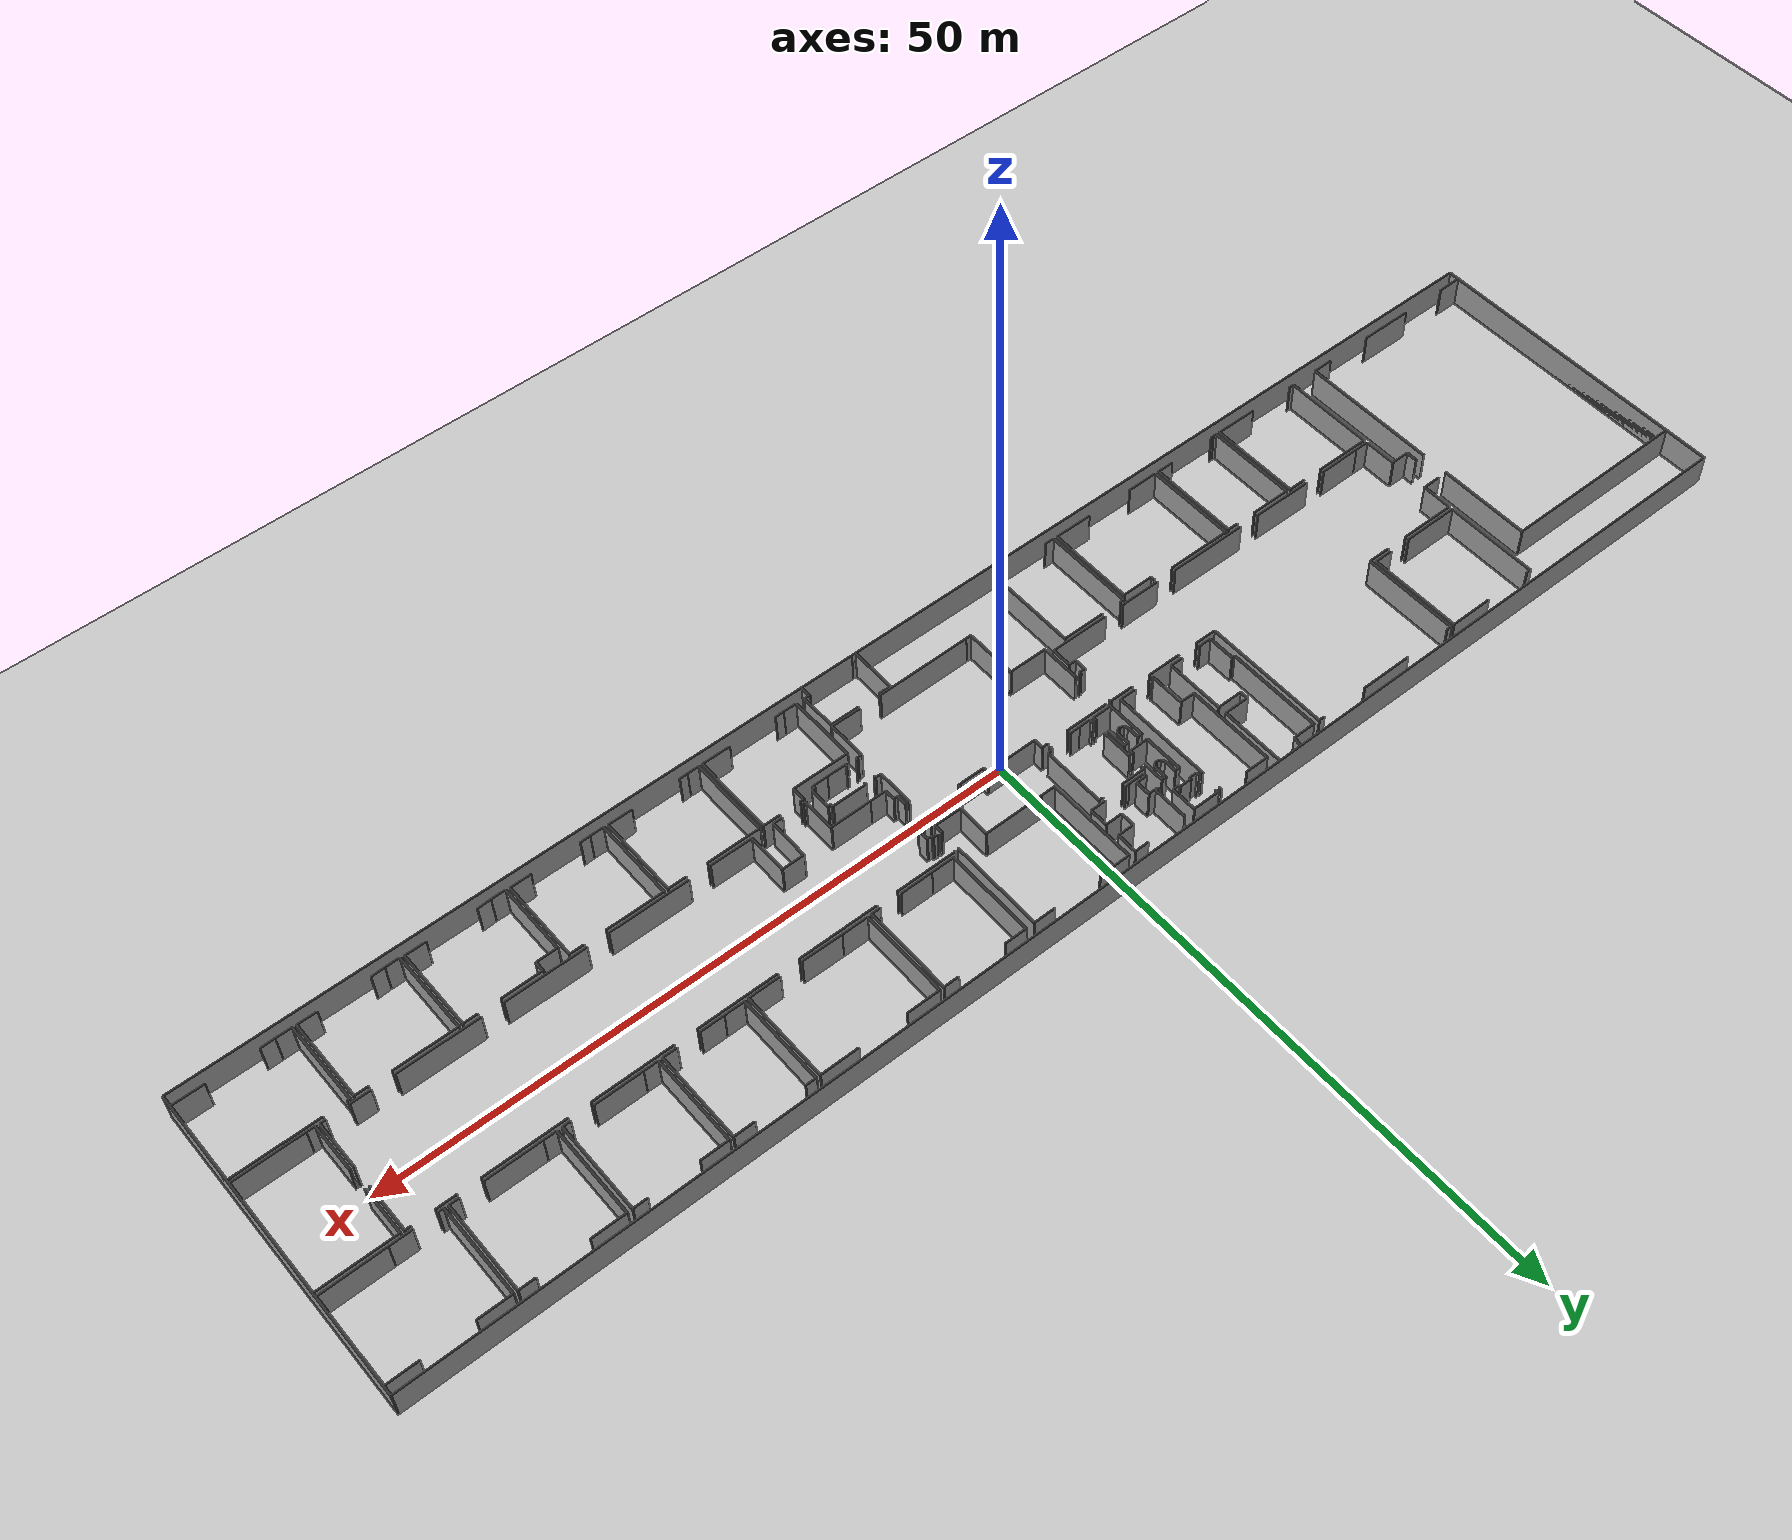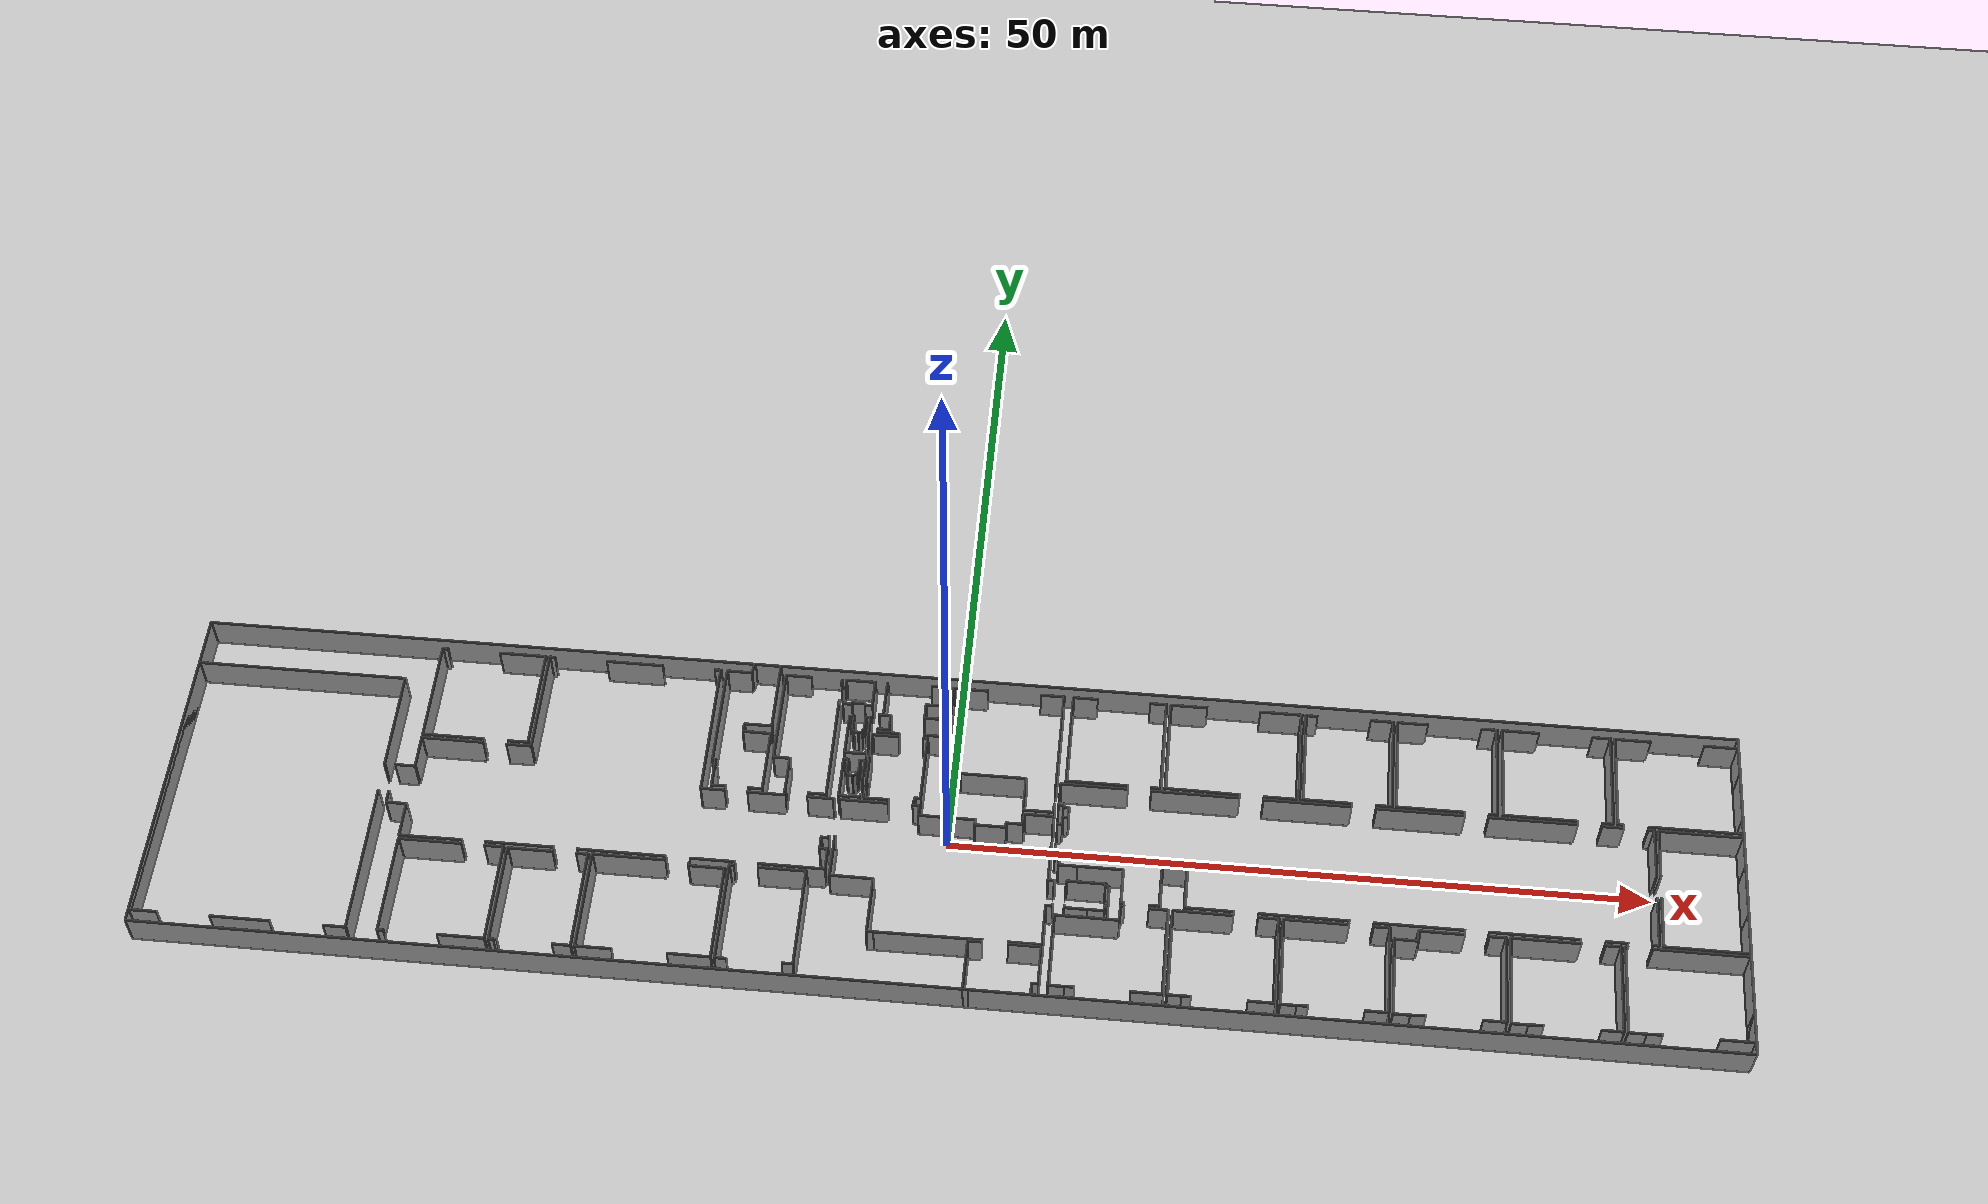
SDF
<sdf version="1.6">
  <world name="default">
    <light name="sun" type="directional">
      <cast_shadows>1</cast_shadows>
      <pose frame="">0 0 10 0 -0 0</pose>
      <diffuse>0.8 0.8 0.8 1</diffuse>
      <specular>0.1 0.1 0.1 1</specular>
      <attenuation>
        <range>1000</range>
        <constant>0.9</constant>
        <linear>0.01</linear>
        <quadratic>0.001</quadratic>
      </attenuation>
      <direction>-0.5 0.5 -1</direction>
    </light>
    <model name="ground_plane">
      <static>1</static>
      <link name="link">
        <collision name="collision">
          <geometry>
            <plane>
              <normal>0 0 1</normal>
              <size>100 100</size>
            </plane>
          </geometry>
          <surface>
            <friction>
              <ode>
                <mu>100</mu>
                <mu2>50</mu2>
              </ode>
              <torsional>
                <ode />
              </torsional>
            </friction>
            <contact>
              <ode />
            </contact>
            <bounce />
          </surface>
          <max_contacts>10</max_contacts>
        </collision>
        <visual name="visual">
          <cast_shadows>0</cast_shadows>
          <geometry>
            <plane>
              <normal>0 0 1</normal>
              <size>100 100</size>
            </plane>
          </geometry>
          <material>
            <script>
              <uri>file://media/materials/scripts/gazebo.material</uri>
              <name>Gazebo/Grey</name>
            </script>
          </material>
        </visual>
        <self_collide>0</self_collide>
        <kinematic>0</kinematic>
        <gravity>1</gravity>
      </link>
    </model>
    <gravity>0 0 -9.8</gravity>
    <magnetic_field>6e-06 2.3e-05 -4.2e-05</magnetic_field>
    <atmosphere type="adiabatic" />
    <physics default="0" name="default_physics" type="ode">
      <max_step_size>0.001</max_step_size>
      <real_time_factor>1</real_time_factor>
      <real_time_update_rate>1000</real_time_update_rate>
    </physics>
    <scene>
      <ambient>0.4 0.4 0.4 1</ambient>
      <background>0.7 0.7 0.7 1</background>
      <shadows>1</shadows>
    </scene>
    <spherical_coordinates>
      <surface_model>EARTH_WGS84</surface_model>
      <latitude_deg>0</latitude_deg>
      <longitude_deg>0</longitude_deg>
      <elevation>0</elevation>
      <heading_deg>0</heading_deg>
    </spherical_coordinates>
  <model name="0510034690_Layout1">
		<static>1</static>
		<link name="Wall_0">
			<collision name="Wall_0_Collision">
				<geometry>
					<box>
						<size>21.0388316156 0.1 2.5</size>
					</box>
				</geometry>
				<pose frame="">10.5194158078 0 1.25 0 0 0</pose>
			</collision>
			<visual name="Wall_0_Visual">
				<pose frame="">10.5194158078 0 1.25 0 0 0</pose>
				<geometry>
					<box>
						<size>21.0388316156 0.1 2.5</size>
					</box>
				</geometry>
				<material>
					<script>
						<uri>file://media/materials/scripts/gazebo.material</uri>
						<name>Gazebo/Grey</name>
					</script>
					<ambient>1 1 1 1</ambient>
				</material>
			</visual>
			<pose frame="">0.0 -24.6704441286 0 0 0 1.57079632679</pose>
		</link>
		<link name="Wall_1">
			<collision name="Wall_1_Collision">
				<geometry>
					<box>
						<size>15.3425897633 0.1 2.5</size>
					</box>
				</geometry>
				<pose frame="">7.67129488166 0 1.25 0 0 0</pose>
			</collision>
			<visual name="Wall_1_Visual">
				<pose frame="">7.67129488166 0 1.25 0 0 0</pose>
				<geometry>
					<box>
						<size>15.3425897633 0.1 2.5</size>
					</box>
				</geometry>
				<material>
					<script>
						<uri>file://media/materials/scripts/gazebo.material</uri>
						<name>Gazebo/Grey</name>
					</script>
					<ambient>1 1 1 1</ambient>
				</material>
			</visual>
			<pose frame="">0.0 -3.63161251304 0 0 0 0.0</pose>
		</link>
		<link name="Wall_2">
			<collision name="Wall_2_Collision">
				<geometry>
					<box>
						<size>7.52580469702 0.1 2.5</size>
					</box>
				</geometry>
				<pose frame="">3.76290234851 0 1.25 0 0 0</pose>
			</collision>
			<visual name="Wall_2_Visual">
				<pose frame="">3.76290234851 0 1.25 0 0 0</pose>
				<geometry>
					<box>
						<size>7.52580469702 0.1 2.5</size>
					</box>
				</geometry>
				<material>
					<script>
						<uri>file://media/materials/scripts/gazebo.material</uri>
						<name>Gazebo/Grey</name>
					</script>
					<ambient>1 1 1 1</ambient>
				</material>
			</visual>
			<pose frame="">15.3425897633 -3.63161251304 0 0 0 -1.57079632679</pose>
		</link>
		<link name="Wall_3">
			<collision name="Wall_3_Collision">
				<geometry>
					<box>
						<size>11.2968849252 0.1 2.5</size>
					</box>
				</geometry>
				<pose frame="">5.64844246259 0 1.25 0 0 0</pose>
			</collision>
			<visual name="Wall_3_Visual">
				<pose frame="">5.64844246259 0 1.25 0 0 0</pose>
				<geometry>
					<box>
						<size>11.2968849252 0.1 2.5</size>
					</box>
				</geometry>
				<material>
					<script>
						<uri>file://media/materials/scripts/gazebo.material</uri>
						<name>Gazebo/Grey</name>
					</script>
					<ambient>1 1 1 1</ambient>
				</material>
			</visual>
			<pose frame="">15.3425897633 -13.3563159223 0 0 0 -1.57079632679</pose>
		</link>
		<link name="Wall_4">
			<collision name="Wall_4_Collision">
				<geometry>
					<box>
						<size>1.58092994537 0.1 2.5</size>
					</box>
				</geometry>
				<pose frame="">0.790464972683 0 1.25 0 0 0</pose>
			</collision>
			<visual name="Wall_4_Visual">
				<pose frame="">0.790464972683 0 1.25 0 0 0</pose>
				<geometry>
					<box>
						<size>1.58092994537 0.1 2.5</size>
					</box>
				</geometry>
				<material>
					<script>
						<uri>file://media/materials/scripts/gazebo.material</uri>
						<name>Gazebo/Grey</name>
					</script>
					<ambient>1 1 1 1</ambient>
				</material>
			</visual>
			<pose frame="">15.3425897633 -24.6532008475 0 0 0 3.14159265359</pose>
		</link>
		<link name="Wall_5">
			<collision name="Wall_5_Collision">
				<geometry>
					<box>
						<size>4.23829707384 0.1 2.5</size>
					</box>
				</geometry>
				<pose frame="">2.11914853692 0 1.25 0 0 0</pose>
			</collision>
			<visual name="Wall_5_Visual">
				<pose frame="">2.11914853692 0 1.25 0 0 0</pose>
				<geometry>
					<box>
						<size>4.23829707384 0.1 2.5</size>
					</box>
				</geometry>
				<material>
					<script>
						<uri>file://media/materials/scripts/gazebo.material</uri>
						<name>Gazebo/Grey</name>
					</script>
					<ambient>1 1 1 1</ambient>
				</material>
			</visual>
			<pose frame="">9.98271868221 -24.6532008475 0 0 0 3.14159265359</pose>
		</link>
		<link name="Wall_6">
			<collision name="Wall_6_Collision">
				<geometry>
					<box>
						<size>1.97899521187 0.1 2.5</size>
					</box>
				</geometry>
				<pose frame="">0.989497605936 0 1.25 0 0 0</pose>
			</collision>
			<visual name="Wall_6_Visual">
				<pose frame="">0.989497605936 0 1.25 0 0 0</pose>
				<geometry>
					<box>
						<size>1.97899521187 0.1 2.5</size>
					</box>
				</geometry>
				<material>
					<script>
						<uri>file://media/materials/scripts/gazebo.material</uri>
						<name>Gazebo/Grey</name>
					</script>
					<ambient>1 1 1 1</ambient>
				</material>
			</visual>
			<pose frame="">1.9789200888 -24.6532008475 0 0 0 -3.13287939384</pose>
		</link>
		<link name="Wall_7">
			<collision name="Wall_7_Collision">
				<geometry>
					<box>
						<size>7.58197214957 0.1 2.5</size>
					</box>
				</geometry>
				<pose frame="">3.79098607478 0 1.25 0 0 0</pose>
			</collision>
			<visual name="Wall_7_Visual">
				<pose frame="">3.79098607478 0 1.25 0 0 0</pose>
				<geometry>
					<box>
						<size>7.58197214957 0.1 2.5</size>
					</box>
				</geometry>
				<material>
					<script>
						<uri>file://media/materials/scripts/gazebo.material</uri>
						<name>Gazebo/Grey</name>
					</script>
					<ambient>1 1 1 1</ambient>
				</material>
			</visual>
			<pose frame="">17.571283851 -8.32913873614 0 0 0 1.57079632679</pose>
		</link>
		<link name="Wall_8">
			<collision name="Wall_8_Collision">
				<geometry>
					<box>
						<size>0.39367932315 0.1 2.5</size>
					</box>
				</geometry>
				<pose frame="">0.196839661575 0 1.25 0 0 0</pose>
			</collision>
			<visual name="Wall_8_Visual">
				<pose frame="">0.196839661575 0 1.25 0 0 0</pose>
				<geometry>
					<box>
						<size>0.39367932315 0.1 2.5</size>
					</box>
				</geometry>
				<material>
					<script>
						<uri>file://media/materials/scripts/gazebo.material</uri>
						<name>Gazebo/Grey</name>
					</script>
					<ambient>1 1 1 1</ambient>
				</material>
			</visual>
			<pose frame="">17.571283851 -0.747166586578 0 0 0 0.0</pose>
		</link>
		<link name="Wall_9">
			<collision name="Wall_9_Collision">
				<geometry>
					<box>
						<size>3.42646818298 0.1 2.5</size>
					</box>
				</geometry>
				<pose frame="">1.71323409149 0 1.25 0 0 0</pose>
			</collision>
			<visual name="Wall_9_Visual">
				<pose frame="">1.71323409149 0 1.25 0 0 0</pose>
				<geometry>
					<box>
						<size>3.42646818298 0.1 2.5</size>
					</box>
				</geometry>
				<material>
					<script>
						<uri>file://media/materials/scripts/gazebo.material</uri>
						<name>Gazebo/Grey</name>
					</script>
					<ambient>1 1 1 1</ambient>
				</material>
			</visual>
			<pose frame="">21.843433543 -0.747166586578 0 0 0 0.0</pose>
		</link>
		<link name="Wall_10">
			<collision name="Wall_10_Collision">
				<geometry>
					<box>
						<size>7.57677380746 0.1 2.5</size>
					</box>
				</geometry>
				<pose frame="">3.78838690373 0 1.25 0 0 0</pose>
			</collision>
			<visual name="Wall_10_Visual">
				<pose frame="">3.78838690373 0 1.25 0 0 0</pose>
				<geometry>
					<box>
						<size>7.57677380746 0.1 2.5</size>
					</box>
				</geometry>
				<material>
					<script>
						<uri>file://media/materials/scripts/gazebo.material</uri>
						<name>Gazebo/Grey</name>
					</script>
					<ambient>1 1 1 1</ambient>
				</material>
			</visual>
			<pose frame="">25.269901726 -0.747166586578 0 0 0 -1.57079632679</pose>
		</link>
		<link name="Wall_11">
			<collision name="Wall_11_Collision">
				<geometry>
					<box>
						<size>1.49243134068 0.1 2.5</size>
					</box>
				</geometry>
				<pose frame="">0.746215670339 0 1.25 0 0 0</pose>
			</collision>
			<visual name="Wall_11_Visual">
				<pose frame="">0.746215670339 0 1.25 0 0 0</pose>
				<geometry>
					<box>
						<size>1.49243134068 0.1 2.5</size>
					</box>
				</geometry>
				<material>
					<script>
						<uri>file://media/materials/scripts/gazebo.material</uri>
						<name>Gazebo/Grey</name>
					</script>
					<ambient>1 1 1 1</ambient>
				</material>
			</visual>
			<pose frame="">25.269901726 -8.32394039403 0 0 0 3.14159265359</pose>
		</link>
		<link name="Wall_12">
			<collision name="Wall_12_Collision">
				<geometry>
					<box>
						<size>4.47526841985 0.1 2.5</size>
					</box>
				</geometry>
				<pose frame="">2.23763420992 0 1.25 0 0 0</pose>
			</collision>
			<visual name="Wall_12_Visual">
				<pose frame="">2.23763420992 0 1.25 0 0 0</pose>
				<geometry>
					<box>
						<size>4.47526841985 0.1 2.5</size>
					</box>
				</geometry>
				<material>
					<script>
						<uri>file://media/materials/scripts/gazebo.material</uri>
						<name>Gazebo/Grey</name>
					</script>
					<ambient>1 1 1 1</ambient>
				</material>
			</visual>
			<pose frame="">22.0465492518 -8.32394039403 0 0 0 -3.14043108231</pose>
		</link>
		<link name="Wall_13">
			<collision name="Wall_13_Collision">
				<geometry>
					<box>
						<size>7.46164954806 0.1 2.5</size>
					</box>
				</geometry>
				<pose frame="">3.73082477403 0 1.25 0 0 0</pose>
			</collision>
			<visual name="Wall_13_Visual">
				<pose frame="">3.73082477403 0 1.25 0 0 0</pose>
				<geometry>
					<box>
						<size>7.46164954806 0.1 2.5</size>
					</box>
				</geometry>
				<material>
					<script>
						<uri>file://media/materials/scripts/gazebo.material</uri>
						<name>Gazebo/Grey</name>
					</script>
					<ambient>1 1 1 1</ambient>
				</material>
			</visual>
			<pose frame="">17.5726785282 -24.6704441286 0 0 0 1.57079632679</pose>
		</link>
		<link name="Wall_14">
			<collision name="Wall_14_Collision">
				<geometry>
					<box>
						<size>4.50696260871 0.1 2.5</size>
					</box>
				</geometry>
				<pose frame="">2.25348130435 0 1.25 0 0 0</pose>
			</collision>
			<visual name="Wall_14_Visual">
				<pose frame="">2.25348130435 0 1.25 0 0 0</pose>
				<geometry>
					<box>
						<size>4.50696260871 0.1 2.5</size>
					</box>
				</geometry>
				<material>
					<script>
						<uri>file://media/materials/scripts/gazebo.material</uri>
						<name>Gazebo/Grey</name>
					</script>
					<ambient>1 1 1 1</ambient>
				</material>
			</visual>
			<pose frame="">17.5726785282 -17.2087945805 0 0 0 0.0</pose>
		</link>
		<link name="Wall_15">
			<collision name="Wall_15_Collision">
				<geometry>
					<box>
						<size>1.36716397473 0.1 2.5</size>
					</box>
				</geometry>
				<pose frame="">0.683581987364 0 1.25 0 0 0</pose>
			</collision>
			<visual name="Wall_15_Visual">
				<pose frame="">0.683581987364 0 1.25 0 0 0</pose>
				<geometry>
					<box>
						<size>1.36716397473 0.1 2.5</size>
					</box>
				</geometry>
				<material>
					<script>
						<uri>file://media/materials/scripts/gazebo.material</uri>
						<name>Gazebo/Grey</name>
					</script>
					<ambient>1 1 1 1</ambient>
				</material>
			</visual>
			<pose frame="">23.7239654982 -17.2087945805 0 0 0 0.0</pose>
		</link>
		<link name="Wall_16">
			<collision name="Wall_16_Collision">
				<geometry>
					<box>
						<size>7.43223453905 0.1 2.5</size>
					</box>
				</geometry>
				<pose frame="">3.71611726953 0 1.25 0 0 0</pose>
			</collision>
			<visual name="Wall_16_Visual">
				<pose frame="">3.71611726953 0 1.25 0 0 0</pose>
				<geometry>
					<box>
						<size>7.43223453905 0.1 2.5</size>
					</box>
				</geometry>
				<material>
					<script>
						<uri>file://media/materials/scripts/gazebo.material</uri>
						<name>Gazebo/Grey</name>
					</script>
					<ambient>1 1 1 1</ambient>
				</material>
			</visual>
			<pose frame="">25.091129473 -17.2087945805 0 0 0 -1.57079632679</pose>
		</link>
		<link name="Wall_17">
			<collision name="Wall_17_Collision">
				<geometry>
					<box>
						<size>3.31793694284 0.1 2.5</size>
					</box>
				</geometry>
				<pose frame="">1.65896847142 0 1.25 0 0 0</pose>
			</collision>
			<visual name="Wall_17_Visual">
				<pose frame="">1.65896847142 0 1.25 0 0 0</pose>
				<geometry>
					<box>
						<size>3.31793694284 0.1 2.5</size>
					</box>
				</geometry>
				<material>
					<script>
						<uri>file://media/materials/scripts/gazebo.material</uri>
						<name>Gazebo/Grey</name>
					</script>
					<ambient>1 1 1 1</ambient>
				</material>
			</visual>
			<pose frame="">25.091129473 -24.6410291196 0 0 0 3.14159265359</pose>
		</link>
		<link name="Wall_18">
			<collision name="Wall_18_Collision">
				<geometry>
					<box>
						<size>0.433349389511 0.1 2.5</size>
					</box>
				</geometry>
				<pose frame="">0.216674694756 0 1.25 0 0 0</pose>
			</collision>
			<visual name="Wall_18_Visual">
				<pose frame="">0.216674694756 0 1.25 0 0 0</pose>
				<geometry>
					<box>
						<size>0.433349389511 0.1 2.5</size>
					</box>
				</geometry>
				<material>
					<script>
						<uri>file://media/materials/scripts/gazebo.material</uri>
						<name>Gazebo/Grey</name>
					</script>
					<ambient>1 1 1 1</ambient>
				</material>
			</visual>
			<pose frame="">18.0050284451 -24.6410291196 0 0 0 -3.07366214587</pose>
		</link>
		<link name="Wall_19">
			<collision name="Wall_19_Collision">
				<geometry>
					<box>
						<size>0.34511920052 0.1 2.5</size>
					</box>
				</geometry>
				<pose frame="">0.17255960026 0 1.25 0 0 0</pose>
			</collision>
			<visual name="Wall_19_Visual">
				<pose frame="">0.17255960026 0 1.25 0 0 0</pose>
				<geometry>
					<box>
						<size>0.34511920052 0.1 2.5</size>
					</box>
				</geometry>
				<material>
					<script>
						<uri>file://media/materials/scripts/gazebo.material</uri>
						<name>Gazebo/Grey</name>
					</script>
					<ambient>1 1 1 1</ambient>
				</material>
			</visual>
			<pose frame="">25.7380060935 -24.6487632383 0 0 0 3.14159265359</pose>
		</link>
		<link name="Wall_20">
			<collision name="Wall_20_Collision">
				<geometry>
					<box>
						<size>7.39166211283 0.1 2.5</size>
					</box>
				</geometry>
				<pose frame="">3.69583105642 0 1.25 0 0 0</pose>
			</collision>
			<visual name="Wall_20_Visual">
				<pose frame="">3.69583105642 0 1.25 0 0 0</pose>
				<geometry>
					<box>
						<size>7.39166211283 0.1 2.5</size>
					</box>
				</geometry>
				<material>
					<script>
						<uri>file://media/materials/scripts/gazebo.material</uri>
						<name>Gazebo/Grey</name>
					</script>
					<ambient>1 1 1 1</ambient>
				</material>
			</visual>
			<pose frame="">25.392886893 -24.6487632383 0 0 0 1.57079632679</pose>
		</link>
		<link name="Wall_21">
			<collision name="Wall_21_Collision">
				<geometry>
					<box>
						<size>3.22132385291 0.1 2.5</size>
					</box>
				</geometry>
				<pose frame="">1.61066192645 0 1.25 0 0 0</pose>
			</collision>
			<visual name="Wall_21_Visual">
				<pose frame="">1.61066192645 0 1.25 0 0 0</pose>
				<geometry>
					<box>
						<size>3.22132385291 0.1 2.5</size>
					</box>
				</geometry>
				<material>
					<script>
						<uri>file://media/materials/scripts/gazebo.material</uri>
						<name>Gazebo/Grey</name>
					</script>
					<ambient>1 1 1 1</ambient>
				</material>
			</visual>
			<pose frame="">25.392886893 -17.2571011255 0 0 0 0.0</pose>
		</link>
		<link name="Wall_22">
			<collision name="Wall_22_Collision">
				<geometry>
					<box>
						<size>0.834143725284 0.1 2.5</size>
					</box>
				</geometry>
				<pose frame="">0.417071862642 0 1.25 0 0 0</pose>
			</collision>
			<visual name="Wall_22_Visual">
				<pose frame="">0.417071862642 0 1.25 0 0 0</pose>
				<geometry>
					<box>
						<size>0.834143725284 0.1 2.5</size>
					</box>
				</geometry>
				<material>
					<script>
						<uri>file://media/materials/scripts/gazebo.material</uri>
						<name>Gazebo/Grey</name>
					</script>
					<ambient>1 1 1 1</ambient>
				</material>
			</visual>
			<pose frame="">30.29188057 -17.2571011255 0 0 0 0.0</pose>
		</link>
		<link name="Wall_23">
			<collision name="Wall_23_Collision">
				<geometry>
					<box>
						<size>7.38392799409 0.1 2.5</size>
					</box>
				</geometry>
				<pose frame="">3.69196399704 0 1.25 0 0 0</pose>
			</collision>
			<visual name="Wall_23_Visual">
				<pose frame="">3.69196399704 0 1.25 0 0 0</pose>
				<geometry>
					<box>
						<size>7.38392799409 0.1 2.5</size>
					</box>
				</geometry>
				<material>
					<script>
						<uri>file://media/materials/scripts/gazebo.material</uri>
						<name>Gazebo/Grey</name>
					</script>
					<ambient>1 1 1 1</ambient>
				</material>
			</visual>
			<pose frame="">31.1260242953 -17.2571011255 0 0 0 -1.57079632679</pose>
		</link>
		<link name="Wall_24">
			<collision name="Wall_24_Collision">
				<geometry>
					<box>
						<size>1.29578186235 0.1 2.5</size>
					</box>
				</geometry>
				<pose frame="">0.647890931175 0 1.25 0 0 0</pose>
			</collision>
			<visual name="Wall_24_Visual">
				<pose frame="">0.647890931175 0 1.25 0 0 0</pose>
				<geometry>
					<box>
						<size>1.29578186235 0.1 2.5</size>
					</box>
				</geometry>
				<material>
					<script>
						<uri>file://media/materials/scripts/gazebo.material</uri>
						<name>Gazebo/Grey</name>
					</script>
					<ambient>1 1 1 1</ambient>
				</material>
			</visual>
			<pose frame="">31.1260242953 -24.6410291196 0 0 0 3.14159265359</pose>
		</link>
		<link name="Wall_25">
			<collision name="Wall_25_Collision">
				<geometry>
					<box>
						<size>0.222648770081 0.1 2.5</size>
					</box>
				</geometry>
				<pose frame="">0.111324385041 0 1.25 0 0 0</pose>
			</collision>
			<visual name="Wall_25_Visual">
				<pose frame="">0.111324385041 0 1.25 0 0 0</pose>
				<geometry>
					<box>
						<size>0.222648770081 0.1 2.5</size>
					</box>
				</geometry>
				<material>
					<script>
						<uri>file://media/materials/scripts/gazebo.material</uri>
						<name>Gazebo/Grey</name>
					</script>
					<ambient>1 1 1 1</ambient>
				</material>
			</visual>
			<pose frame="">25.9605204935 -24.6410291196 0 0 0 -3.10684880576</pose>
		</link>
		<link name="Wall_26">
			<collision name="Wall_26_Collision">
				<geometry>
					<box>
						<size>7.4463080994 0.1 2.5</size>
					</box>
				</geometry>
				<pose frame="">3.7231540497 0 1.25 0 0 0</pose>
			</collision>
			<visual name="Wall_26_Visual">
				<pose frame="">3.7231540497 0 1.25 0 0 0</pose>
				<geometry>
					<box>
						<size>7.4463080994 0.1 2.5</size>
					</box>
				</geometry>
				<material>
					<script>
						<uri>file://media/materials/scripts/gazebo.material</uri>
						<name>Gazebo/Grey</name>
					</script>
					<ambient>1 1 1 1</ambient>
				</material>
			</visual>
			<pose frame="">31.4268941935 -24.6553562576 0 0 0 1.57079632679</pose>
		</link>
		<link name="Wall_27">
			<collision name="Wall_27_Collision">
				<geometry>
					<box>
						<size>5.20316008485 0.1 2.5</size>
					</box>
				</geometry>
				<pose frame="">2.60158004242 0 1.25 0 0 0</pose>
			</collision>
			<visual name="Wall_27_Visual">
				<pose frame="">2.60158004242 0 1.25 0 0 0</pose>
				<geometry>
					<box>
						<size>5.20316008485 0.1 2.5</size>
					</box>
				</geometry>
				<material>
					<script>
						<uri>file://media/materials/scripts/gazebo.material</uri>
						<name>Gazebo/Grey</name>
					</script>
					<ambient>1 1 1 1</ambient>
				</material>
			</visual>
			<pose frame="">31.4268941935 -17.2090481582 0 0 0 0.0</pose>
		</link>
		<link name="Wall_28">
			<collision name="Wall_28_Collision">
				<geometry>
					<box>
						<size>0.305941451453 0.1 2.5</size>
					</box>
				</geometry>
				<pose frame="">0.152970725727 0 1.25 0 0 0</pose>
			</collision>
			<visual name="Wall_28_Visual">
				<pose frame="">0.152970725727 0 1.25 0 0 0</pose>
				<geometry>
					<box>
						<size>0.305941451453 0.1 2.5</size>
					</box>
				</geometry>
				<material>
					<script>
						<uri>file://media/materials/scripts/gazebo.material</uri>
						<name>Gazebo/Grey</name>
					</script>
					<ambient>1 1 1 1</ambient>
				</material>
			</visual>
			<pose frame="">38.3278835267 -17.2090481582 0 0 0 -1.57079632679</pose>
		</link>
		<link name="Wall_29">
			<collision name="Wall_29_Collision">
				<geometry>
					<box>
						<size>2.54845552184 0.1 2.5</size>
					</box>
				</geometry>
				<pose frame="">1.27422776092 0 1.25 0 0 0</pose>
			</collision>
			<visual name="Wall_29_Visual">
				<pose frame="">1.27422776092 0 1.25 0 0 0</pose>
				<geometry>
					<box>
						<size>2.54845552184 0.1 2.5</size>
					</box>
				</geometry>
				<material>
					<script>
						<uri>file://media/materials/scripts/gazebo.material</uri>
						<name>Gazebo/Grey</name>
					</script>
					<ambient>1 1 1 1</ambient>
				</material>
			</visual>
			<pose frame="">38.3278835267 -17.5149896097 0 0 0 0.0</pose>
		</link>
		<link name="Wall_30">
			<collision name="Wall_30_Collision">
				<geometry>
					<box>
						<size>7.12375731096 0.1 2.5</size>
					</box>
				</geometry>
				<pose frame="">3.56187865548 0 1.25 0 0 0</pose>
			</collision>
			<visual name="Wall_30_Visual">
				<pose frame="">3.56187865548 0 1.25 0 0 0</pose>
				<geometry>
					<box>
						<size>7.12375731096 0.1 2.5</size>
					</box>
				</geometry>
				<material>
					<script>
						<uri>file://media/materials/scripts/gazebo.material</uri>
						<name>Gazebo/Grey</name>
					</script>
					<ambient>1 1 1 1</ambient>
				</material>
			</visual>
			<pose frame="">40.8763390486 -17.5149896097 0 0 0 -1.57079632679</pose>
		</link>
		<link name="Wall_31">
			<collision name="Wall_31_Collision">
				<geometry>
					<box>
						<size>3.03570500296 0.1 2.5</size>
					</box>
				</geometry>
				<pose frame="">1.51785250148 0 1.25 0 0 0</pose>
			</collision>
			<visual name="Wall_31_Visual">
				<pose frame="">1.51785250148 0 1.25 0 0 0</pose>
				<geometry>
					<box>
						<size>3.03570500296 0.1 2.5</size>
					</box>
				</geometry>
				<material>
					<script>
						<uri>file://media/materials/scripts/gazebo.material</uri>
						<name>Gazebo/Grey</name>
					</script>
					<ambient>1 1 1 1</ambient>
				</material>
			</visual>
			<pose frame="">40.8763390486 -24.6387469206 0 0 0 3.14159265359</pose>
		</link>
		<link name="Wall_32">
			<collision name="Wall_32_Collision">
				<geometry>
					<box>
						<size>2.5426774841 0.1 2.5</size>
					</box>
				</geometry>
				<pose frame="">1.27133874205 0 1.25 0 0 0</pose>
			</collision>
			<visual name="Wall_32_Visual">
				<pose frame="">1.27133874205 0 1.25 0 0 0</pose>
				<geometry>
					<box>
						<size>2.5426774841 0.1 2.5</size>
					</box>
				</geometry>
				<material>
					<script>
						<uri>file://media/materials/scripts/gazebo.material</uri>
						<name>Gazebo/Grey</name>
					</script>
					<ambient>1 1 1 1</ambient>
				</material>
			</visual>
			<pose frame="">33.969517429 -24.6387469206 0 0 0 -3.13506038388</pose>
		</link>
		<link name="Wall_33">
			<collision name="Wall_33_Collision">
				<geometry>
					<box>
						<size>7.46836935615 0.1 2.5</size>
					</box>
				</geometry>
				<pose frame="">3.73418467808 0 1.25 0 0 0</pose>
			</collision>
			<visual name="Wall_33_Visual">
				<pose frame="">3.73418467808 0 1.25 0 0 0</pose>
				<geometry>
					<box>
						<size>7.46836935615 0.1 2.5</size>
					</box>
				</geometry>
				<material>
					<script>
						<uri>file://media/materials/scripts/gazebo.material</uri>
						<name>Gazebo/Grey</name>
					</script>
					<ambient>1 1 1 1</ambient>
				</material>
			</visual>
			<pose frame="">41.1636425417 -24.667908352 0 0 0 1.57079632679</pose>
		</link>
		<link name="Wall_34">
			<collision name="Wall_34_Collision">
				<geometry>
					<box>
						<size>0.325974086899 0.1 2.5</size>
					</box>
				</geometry>
				<pose frame="">0.162987043449 0 1.25 0 0 0</pose>
			</collision>
			<visual name="Wall_34_Visual">
				<pose frame="">0.162987043449 0 1.25 0 0 0</pose>
				<geometry>
					<box>
						<size>0.325974086899 0.1 2.5</size>
					</box>
				</geometry>
				<material>
					<script>
						<uri>file://media/materials/scripts/gazebo.material</uri>
						<name>Gazebo/Grey</name>
					</script>
					<ambient>1 1 1 1</ambient>
				</material>
			</visual>
			<pose frame="">41.1636425417 -17.1995389958 0 0 0 0.0</pose>
		</link>
		<link name="Wall_35">
			<collision name="Wall_35_Collision">
				<geometry>
					<box>
						<size>3.4456132966 0.1 2.5</size>
					</box>
				</geometry>
				<pose frame="">1.7228066483 0 1.25 0 0 0</pose>
			</collision>
			<visual name="Wall_35_Visual">
				<pose frame="">1.7228066483 0 1.25 0 0 0</pose>
				<geometry>
					<box>
						<size>3.4456132966 0.1 2.5</size>
					</box>
				</geometry>
				<material>
					<script>
						<uri>file://media/materials/scripts/gazebo.material</uri>
						<name>Gazebo/Grey</name>
					</script>
					<ambient>1 1 1 1</ambient>
				</material>
			</visual>
			<pose frame="">43.1615809553 -17.1995389958 0 0 0 0.0</pose>
		</link>
		<link name="Wall_36">
			<collision name="Wall_36_Collision">
				<geometry>
					<box>
						<size>7.45252075216 0.1 2.5</size>
					</box>
				</geometry>
				<pose frame="">3.72626037608 0 1.25 0 0 0</pose>
			</collision>
			<visual name="Wall_36_Visual">
				<pose frame="">3.72626037608 0 1.25 0 0 0</pose>
				<geometry>
					<box>
						<size>7.45252075216 0.1 2.5</size>
					</box>
				</geometry>
				<material>
					<script>
						<uri>file://media/materials/scripts/gazebo.material</uri>
						<name>Gazebo/Grey</name>
					</script>
					<ambient>1 1 1 1</ambient>
				</material>
			</visual>
			<pose frame="">46.6071942519 -17.1995389958 0 0 0 -1.57079632679</pose>
		</link>
		<link name="Wall_37">
			<collision name="Wall_37_Collision">
				<geometry>
					<box>
						<size>0.779497738721 0.1 2.5</size>
					</box>
				</geometry>
				<pose frame="">0.389748869361 0 1.25 0 0 0</pose>
			</collision>
			<visual name="Wall_37_Visual">
				<pose frame="">0.389748869361 0 1.25 0 0 0</pose>
				<geometry>
					<box>
						<size>0.779497738721 0.1 2.5</size>
					</box>
				</geometry>
				<material>
					<script>
						<uri>file://media/materials/scripts/gazebo.material</uri>
						<name>Gazebo/Grey</name>
					</script>
					<ambient>1 1 1 1</ambient>
				</material>
			</visual>
			<pose frame="">46.6071942519 -24.652059748 0 0 0 3.14159265359</pose>
		</link>
		<link name="Wall_38">
			<collision name="Wall_38_Collision">
				<geometry>
					<box>
						<size>0.816420343476 0.1 2.5</size>
					</box>
				</geometry>
				<pose frame="">0.408210171738 0 1.25 0 0 0</pose>
			</collision>
			<visual name="Wall_38_Visual">
				<pose frame="">0.408210171738 0 1.25 0 0 0</pose>
				<geometry>
					<box>
						<size>0.816420343476 0.1 2.5</size>
					</box>
				</geometry>
				<material>
					<script>
						<uri>file://media/materials/scripts/gazebo.material</uri>
						<name>Gazebo/Grey</name>
					</script>
					<ambient>1 1 1 1</ambient>
				</material>
			</visual>
			<pose frame="">41.9799090417 -24.652059748 0 0 0 -3.12217912516</pose>
		</link>
		<link name="Wall_39">
			<collision name="Wall_39_Collision">
				<geometry>
					<box>
						<size>2.85274871848 0.1 2.5</size>
					</box>
				</geometry>
				<pose frame="">1.42637435924 0 1.25 0 0 0</pose>
			</collision>
			<visual name="Wall_39_Visual">
				<pose frame="">1.42637435924 0 1.25 0 0 0</pose>
				<geometry>
					<box>
						<size>2.85274871848 0.1 2.5</size>
					</box>
				</geometry>
				<material>
					<script>
						<uri>file://media/materials/scripts/gazebo.material</uri>
						<name>Gazebo/Grey</name>
					</script>
					<ambient>1 1 1 1</ambient>
				</material>
			</visual>
			<pose frame="">44.2742797443 -10.782502634 0 0 0 1.57079632679</pose>
		</link>
		<link name="Wall_40">
			<collision name="Wall_40_Collision">
				<geometry>
					<box>
						<size>1.16975376341 0.1 2.5</size>
					</box>
				</geometry>
				<pose frame="">0.584876881705 0 1.25 0 0 0</pose>
			</collision>
			<visual name="Wall_40_Visual">
				<pose frame="">0.584876881705 0 1.25 0 0 0</pose>
				<geometry>
					<box>
						<size>1.16975376341 0.1 2.5</size>
					</box>
				</geometry>
				<material>
					<script>
						<uri>file://media/materials/scripts/gazebo.material</uri>
						<name>Gazebo/Grey</name>
					</script>
					<ambient>1 1 1 1</ambient>
				</material>
			</visual>
			<pose frame="">44.2742797443 -7.92975391556 0 0 0 3.14159265359</pose>
		</link>
		<link name="Wall_41">
			<collision name="Wall_41_Collision">
				<geometry>
					<box>
						<size>7.16902092396 0.1 2.5</size>
					</box>
				</geometry>
				<pose frame="">3.58451046198 0 1.25 0 0 0</pose>
			</collision>
			<visual name="Wall_41_Visual">
				<pose frame="">3.58451046198 0 1.25 0 0 0</pose>
				<geometry>
					<box>
						<size>7.16902092396 0.1 2.5</size>
					</box>
				</geometry>
				<material>
					<script>
						<uri>file://media/materials/scripts/gazebo.material</uri>
						<name>Gazebo/Grey</name>
					</script>
					<ambient>1 1 1 1</ambient>
				</material>
			</visual>
			<pose frame="">43.1045259809 -7.92975391556 0 0 0 1.57079632679</pose>
		</link>
		<link name="Wall_42">
			<collision name="Wall_42_Collision">
				<geometry>
					<box>
						<size>1.87431930246 0.1 2.5</size>
					</box>
				</geometry>
				<pose frame="">0.937159651229 0 1.25 0 0 0</pose>
			</collision>
			<visual name="Wall_42_Visual">
				<pose frame="">0.937159651229 0 1.25 0 0 0</pose>
				<geometry>
					<box>
						<size>1.87431930246 0.1 2.5</size>
					</box>
				</geometry>
				<material>
					<script>
						<uri>file://media/materials/scripts/gazebo.material</uri>
						<name>Gazebo/Grey</name>
					</script>
					<ambient>1 1 1 1</ambient>
				</material>
			</visual>
			<pose frame="">43.1045259809 -0.760732991595 0 0 0 0.0</pose>
		</link>
		<link name="Wall_43">
			<collision name="Wall_43_Collision">
				<geometry>
					<box>
						<size>0.264481503411 0.1 2.5</size>
					</box>
				</geometry>
				<pose frame="">0.132240751706 0 1.25 0 0 0</pose>
			</collision>
			<visual name="Wall_43_Visual">
				<pose frame="">0.132240751706 0 1.25 0 0 0</pose>
				<geometry>
					<box>
						<size>0.264481503411 0.1 2.5</size>
					</box>
				</geometry>
				<material>
					<script>
						<uri>file://media/materials/scripts/gazebo.material</uri>
						<name>Gazebo/Grey</name>
					</script>
					<ambient>1 1 1 1</ambient>
				</material>
			</visual>
			<pose frame="">47.2389830014 -0.760732991595 0 0 0 -1.57079632679</pose>
		</link>
		<link name="Wall_44">
			<collision name="Wall_44_Collision">
				<geometry>
					<box>
						<size>8.15391657041 0.1 2.5</size>
					</box>
				</geometry>
				<pose frame="">4.07695828521 0 1.25 0 0 0</pose>
			</collision>
			<visual name="Wall_44_Visual">
				<pose frame="">4.07695828521 0 1.25 0 0 0</pose>
				<geometry>
					<box>
						<size>8.15391657041 0.1 2.5</size>
					</box>
				</geometry>
				<material>
					<script>
						<uri>file://media/materials/scripts/gazebo.material</uri>
						<name>Gazebo/Grey</name>
					</script>
					<ambient>1 1 1 1</ambient>
				</material>
			</visual>
			<pose frame="">47.2389830014 -2.58890115923 0 0 0 -1.57079632679</pose>
		</link>
		<link name="Wall_45">
			<collision name="Wall_45_Collision">
				<geometry>
					<box>
						<size>1.30098020446 0.1 2.5</size>
					</box>
				</geometry>
				<pose frame="">0.65049010223 0 1.25 0 0 0</pose>
			</collision>
			<visual name="Wall_45_Visual">
				<pose frame="">0.65049010223 0 1.25 0 0 0</pose>
				<geometry>
					<box>
						<size>1.30098020446 0.1 2.5</size>
					</box>
				</geometry>
				<material>
					<script>
						<uri>file://media/materials/scripts/gazebo.material</uri>
						<name>Gazebo/Grey</name>
					</script>
					<ambient>1 1 1 1</ambient>
				</material>
			</visual>
			<pose frame="">47.2389830014 -10.7428177296 0 0 0 3.14159265359</pose>
		</link>
		<link name="Wall_46">
			<collision name="Wall_46_Collision">
				<geometry>
					<box>
						<size>0.0923848718355 0.1 2.5</size>
					</box>
				</geometry>
				<pose frame="">0.0461924359178 0 1.25 0 0 0</pose>
			</collision>
			<visual name="Wall_46_Visual">
				<pose frame="">0.0461924359178 0 1.25 0 0 0</pose>
				<geometry>
					<box>
						<size>0.0923848718355 0.1 2.5</size>
					</box>
				</geometry>
				<material>
					<script>
						<uri>file://media/materials/scripts/gazebo.material</uri>
						<name>Gazebo/Grey</name>
					</script>
					<ambient>1 1 1 1</ambient>
				</material>
			</visual>
			<pose frame="">44.3577067958 -10.7428177296 0 0 0 -2.69758647175</pose>
		</link>
		<link name="Wall_47">
			<collision name="Wall_47_Collision">
				<geometry>
					<box>
						<size>2.171892691 0.1 2.5</size>
					</box>
				</geometry>
				<pose frame="">1.0859463455 0 1.25 0 0 0</pose>
			</collision>
			<visual name="Wall_47_Visual">
				<pose frame="">1.0859463455 0 1.25 0 0 0</pose>
				<geometry>
					<box>
						<size>2.171892691 0.1 2.5</size>
					</box>
				</geometry>
				<material>
					<script>
						<uri>file://media/materials/scripts/gazebo.material</uri>
						<name>Gazebo/Grey</name>
					</script>
					<ambient>1 1 1 1</ambient>
				</material>
			</visual>
			<pose frame="">38.9810995888 -10.7163188638 0 0 0 1.57079632679</pose>
		</link>
		<link name="Wall_48">
			<collision name="Wall_48_Collision">
				<geometry>
					<box>
						<size>0.231516407109 0.1 2.5</size>
					</box>
				</geometry>
				<pose frame="">0.115758203554 0 1.25 0 0 0</pose>
			</collision>
			<visual name="Wall_48_Visual">
				<pose frame="">0.115758203554 0 1.25 0 0 0</pose>
				<geometry>
					<box>
						<size>0.231516407109 0.1 2.5</size>
					</box>
				</geometry>
				<material>
					<script>
						<uri>file://media/materials/scripts/gazebo.material</uri>
						<name>Gazebo/Grey</name>
					</script>
					<ambient>1 1 1 1</ambient>
				</material>
			</visual>
			<pose frame="">38.9810995888 -8.54442617276 0 0 0 3.14159265359</pose>
		</link>
		<link name="Wall_49">
			<collision name="Wall_49_Collision">
				<geometry>
					<box>
						<size>7.77278934162 0.1 2.5</size>
					</box>
				</geometry>
				<pose frame="">3.88639467081 0 1.25 0 0 0</pose>
			</collision>
			<visual name="Wall_49_Visual">
				<pose frame="">3.88639467081 0 1.25 0 0 0</pose>
				<geometry>
					<box>
						<size>7.77278934162 0.1 2.5</size>
					</box>
				</geometry>
				<material>
					<script>
						<uri>file://media/materials/scripts/gazebo.material</uri>
						<name>Gazebo/Grey</name>
					</script>
					<ambient>1 1 1 1</ambient>
				</material>
			</visual>
			<pose frame="">38.7495831817 -8.54442617276 0 0 0 1.57079632679</pose>
		</link>
		<link name="Wall_50">
			<collision name="Wall_50_Collision">
				<geometry>
					<box>
						<size>1.80813553219 0.1 2.5</size>
					</box>
				</geometry>
				<pose frame="">0.904067766095 0 1.25 0 0 0</pose>
			</collision>
			<visual name="Wall_50_Visual">
				<pose frame="">0.904067766095 0 1.25 0 0 0</pose>
				<geometry>
					<box>
						<size>1.80813553219 0.1 2.5</size>
					</box>
				</geometry>
				<material>
					<script>
						<uri>file://media/materials/scripts/gazebo.material</uri>
						<name>Gazebo/Grey</name>
					</script>
					<ambient>1 1 1 1</ambient>
				</material>
			</visual>
			<pose frame="">38.7495831817 -0.771636831141 0 0 0 0.0</pose>
		</link>
		<link name="Wall_51">
			<collision name="Wall_51_Collision">
				<geometry>
					<box>
						<size>0.789150353214 0.1 2.5</size>
					</box>
				</geometry>
				<pose frame="">0.394575176607 0 1.25 0 0 0</pose>
			</collision>
			<visual name="Wall_51_Visual">
				<pose frame="">0.394575176607 0 1.25 0 0 0</pose>
				<geometry>
					<box>
						<size>0.789150353214 0.1 2.5</size>
					</box>
				</geometry>
				<material>
					<script>
						<uri>file://media/materials/scripts/gazebo.material</uri>
						<name>Gazebo/Grey</name>
					</script>
					<ambient>1 1 1 1</ambient>
				</material>
			</visual>
			<pose frame="">40.5577187139 -0.771636831141 0 0 0 1.35972543623</pose>
		</link>
		<link name="Wall_52">
			<collision name="Wall_52_Collision">
				<geometry>
					<box>
						<size>1.89993525354 0.1 2.5</size>
					</box>
				</geometry>
				<pose frame="">0.949967626772 0 1.25 0 0 0</pose>
			</collision>
			<visual name="Wall_52_Visual">
				<pose frame="">0.949967626772 0 1.25 0 0 0</pose>
				<geometry>
					<box>
						<size>1.89993525354 0.1 2.5</size>
					</box>
				</geometry>
				<material>
					<script>
						<uri>file://media/materials/scripts/gazebo.material</uri>
						<name>Gazebo/Grey</name>
					</script>
					<ambient>1 1 1 1</ambient>
				</material>
			</visual>
			<pose frame="">40.7230513507 -0.0 0 0 0 -0.00220219864221</pose>
		</link>
		<link name="Wall_53">
			<collision name="Wall_53_Collision">
				<geometry>
					<box>
						<size>5.2768243962 0.1 2.5</size>
					</box>
				</geometry>
				<pose frame="">2.6384121981 0 1.25 0 0 0</pose>
			</collision>
			<visual name="Wall_53_Visual">
				<pose frame="">2.6384121981 0 1.25 0 0 0</pose>
				<geometry>
					<box>
						<size>5.2768243962 0.1 2.5</size>
					</box>
				</geometry>
				<material>
					<script>
						<uri>file://media/materials/scripts/gazebo.material</uri>
						<name>Gazebo/Grey</name>
					</script>
					<ambient>1 1 1 1</ambient>
				</material>
			</visual>
			<pose frame="">42.6229819973 -0.00418403145377 0 0 0 -1.57079632679</pose>
		</link>
		<link name="Wall_54">
			<collision name="Wall_54_Collision">
				<geometry>
					<box>
						<size>1.99907951308 0.1 2.5</size>
					</box>
				</geometry>
				<pose frame="">0.99953975654 0 1.25 0 0 0</pose>
			</collision>
			<visual name="Wall_54_Visual">
				<pose frame="">0.99953975654 0 1.25 0 0 0</pose>
				<geometry>
					<box>
						<size>1.99907951308 0.1 2.5</size>
					</box>
				</geometry>
				<material>
					<script>
						<uri>file://media/materials/scripts/gazebo.material</uri>
						<name>Gazebo/Grey</name>
					</script>
					<ambient>1 1 1 1</ambient>
				</material>
			</visual>
			<pose frame="">42.6229819973 -5.28100842765 0 0 0 3.14159265359</pose>
		</link>
		<link name="Wall_55">
			<collision name="Wall_55_Collision">
				<geometry>
					<box>
						<size>0.661457336192 0.1 2.5</size>
					</box>
				</geometry>
				<pose frame="">0.330728668096 0 1.25 0 0 0</pose>
			</collision>
			<visual name="Wall_55_Visual">
				<pose frame="">0.330728668096 0 1.25 0 0 0</pose>
				<geometry>
					<box>
						<size>0.661457336192 0.1 2.5</size>
					</box>
				</geometry>
				<material>
					<script>
						<uri>file://media/materials/scripts/gazebo.material</uri>
						<name>Gazebo/Grey</name>
					</script>
					<ambient>1 1 1 1</ambient>
				</material>
			</visual>
			<pose frame="">40.6239024842 -5.28100842765 0 0 0 -1.57079632679</pose>
		</link>
		<link name="Wall_56">
			<collision name="Wall_56_Collision">
				<geometry>
					<box>
						<size>2.01759068254 0.1 2.5</size>
					</box>
				</geometry>
				<pose frame="">1.00879534127 0 1.25 0 0 0</pose>
			</collision>
			<visual name="Wall_56_Visual">
				<pose frame="">1.00879534127 0 1.25 0 0 0</pose>
				<geometry>
					<box>
						<size>2.01759068254 0.1 2.5</size>
					</box>
				</geometry>
				<material>
					<script>
						<uri>file://media/materials/scripts/gazebo.material</uri>
						<name>Gazebo/Grey</name>
					</script>
					<ambient>1 1 1 1</ambient>
				</material>
			</visual>
			<pose frame="">40.6239024842 -5.94246576385 0 0 0 0.0</pose>
		</link>
		<link name="Wall_57">
			<collision name="Wall_57_Collision">
				<geometry>
					<box>
						<size>4.76396357103 0.1 2.5</size>
					</box>
				</geometry>
				<pose frame="">2.38198178552 0 1.25 0 0 0</pose>
			</collision>
			<visual name="Wall_57_Visual">
				<pose frame="">2.38198178552 0 1.25 0 0 0</pose>
				<geometry>
					<box>
						<size>4.76396357103 0.1 2.5</size>
					</box>
				</geometry>
				<material>
					<script>
						<uri>file://media/materials/scripts/gazebo.material</uri>
						<name>Gazebo/Grey</name>
					</script>
					<ambient>1 1 1 1</ambient>
				</material>
			</visual>
			<pose frame="">42.6414931667 -5.94246576385 0 0 0 -1.57079632679</pose>
		</link>
		<link name="Wall_58">
			<collision name="Wall_58_Collision">
				<geometry>
					<box>
						<size>1.00442112657 0.1 2.5</size>
					</box>
				</geometry>
				<pose frame="">0.502210563285 0 1.25 0 0 0</pose>
			</collision>
			<visual name="Wall_58_Visual">
				<pose frame="">0.502210563285 0 1.25 0 0 0</pose>
				<geometry>
					<box>
						<size>1.00442112657 0.1 2.5</size>
					</box>
				</geometry>
				<material>
					<script>
						<uri>file://media/materials/scripts/gazebo.material</uri>
						<name>Gazebo/Grey</name>
					</script>
					<ambient>1 1 1 1</ambient>
				</material>
			</visual>
			<pose frame="">42.6414931667 -10.7064293349 0 0 0 3.14159265359</pose>
		</link>
		<link name="Wall_59">
			<collision name="Wall_59_Collision">
				<geometry>
					<box>
						<size>1.02462827794 0.1 2.5</size>
					</box>
				</geometry>
				<pose frame="">0.51231413897 0 1.25 0 0 0</pose>
			</collision>
			<visual name="Wall_59_Visual">
				<pose frame="">0.51231413897 0 1.25 0 0 0</pose>
				<geometry>
					<box>
						<size>1.02462827794 0.1 2.5</size>
					</box>
				</geometry>
				<material>
					<script>
						<uri>file://media/materials/scripts/gazebo.material</uri>
						<name>Gazebo/Grey</name>
					</script>
					<ambient>1 1 1 1</ambient>
				</material>
			</visual>
			<pose frame="">40.0056801397 -10.7064293349 0 0 0 -3.13194068257</pose>
		</link>
		<link name="Wall_60">
			<collision name="Wall_60_Collision">
				<geometry>
					<box>
						<size>1.18103796945 0.1 2.5</size>
					</box>
				</geometry>
				<pose frame="">0.590518984726 0 1.25 0 0 0</pose>
			</collision>
			<visual name="Wall_60_Visual">
				<pose frame="">0.590518984726 0 1.25 0 0 0</pose>
				<geometry>
					<box>
						<size>1.18103796945 0.1 2.5</size>
					</box>
				</geometry>
				<material>
					<script>
						<uri>file://media/materials/scripts/gazebo.material</uri>
						<name>Gazebo/Grey</name>
					</script>
					<ambient>1 1 1 1</ambient>
				</material>
			</visual>
			<pose frame="">18.7377411048 -16.9317609828 0 0 0 3.14159265359</pose>
		</link>
		<link name="Wall_61">
			<collision name="Wall_61_Collision">
				<geometry>
					<box>
						<size>2.63036110727 0.1 2.5</size>
					</box>
				</geometry>
				<pose frame="">1.31518055364 0 1.25 0 0 0</pose>
			</collision>
			<visual name="Wall_61_Visual">
				<pose frame="">1.31518055364 0 1.25 0 0 0</pose>
				<geometry>
					<box>
						<size>2.63036110727 0.1 2.5</size>
					</box>
				</geometry>
				<material>
					<script>
						<uri>file://media/materials/scripts/gazebo.material</uri>
						<name>Gazebo/Grey</name>
					</script>
					<ambient>1 1 1 1</ambient>
				</material>
			</visual>
			<pose frame="">17.5567031354 -16.9317609828 0 0 0 1.57079632679</pose>
		</link>
		<link name="Wall_62">
			<collision name="Wall_62_Collision">
				<geometry>
					<box>
						<size>1.45236606979 0.1 2.5</size>
					</box>
				</geometry>
				<pose frame="">0.726183034894 0 1.25 0 0 0</pose>
			</collision>
			<visual name="Wall_62_Visual">
				<pose frame="">0.726183034894 0 1.25 0 0 0</pose>
				<geometry>
					<box>
						<size>1.45236606979 0.1 2.5</size>
					</box>
				</geometry>
				<material>
					<script>
						<uri>file://media/materials/scripts/gazebo.material</uri>
						<name>Gazebo/Grey</name>
					</script>
					<ambient>1 1 1 1</ambient>
				</material>
			</visual>
			<pose frame="">17.5567031354 -14.3013998755 0 0 0 3.14159265359</pose>
		</link>
		<link name="Wall_63">
			<collision name="Wall_63_Collision">
				<geometry>
					<box>
						<size>0.917063621368 0.1 2.5</size>
					</box>
				</geometry>
				<pose frame="">0.458531810684 0 1.25 0 0 0</pose>
			</collision>
			<visual name="Wall_63_Visual">
				<pose frame="">0.458531810684 0 1.25 0 0 0</pose>
				<geometry>
					<box>
						<size>0.917063621368 0.1 2.5</size>
					</box>
				</geometry>
				<material>
					<script>
						<uri>file://media/materials/scripts/gazebo.material</uri>
						<name>Gazebo/Grey</name>
					</script>
					<ambient>1 1 1 1</ambient>
				</material>
			</visual>
			<pose frame="">16.1043370656 -14.3013998755 0 0 0 1.57079632679</pose>
		</link>
		<link name="Wall_64">
			<collision name="Wall_64_Collision">
				<geometry>
					<box>
						<size>1.45553579059 0.1 2.5</size>
					</box>
				</geometry>
				<pose frame="">0.727767895293 0 1.25 0 0 0</pose>
			</collision>
			<visual name="Wall_64_Visual">
				<pose frame="">0.727767895293 0 1.25 0 0 0</pose>
				<geometry>
					<box>
						<size>1.45553579059 0.1 2.5</size>
					</box>
				</geometry>
				<material>
					<script>
						<uri>file://media/materials/scripts/gazebo.material</uri>
						<name>Gazebo/Grey</name>
					</script>
					<ambient>1 1 1 1</ambient>
				</material>
			</visual>
			<pose frame="">16.1043370656 -11.0994747139 0 0 0 0.0</pose>
		</link>
		<link name="Wall_65">
			<collision name="Wall_65_Collision">
				<geometry>
					<box>
						<size>2.47238222268 0.1 2.5</size>
					</box>
				</geometry>
				<pose frame="">1.23619111134 0 1.25 0 0 0</pose>
			</collision>
			<visual name="Wall_65_Visual">
				<pose frame="">1.23619111134 0 1.25 0 0 0</pose>
				<geometry>
					<box>
						<size>2.47238222268 0.1 2.5</size>
					</box>
				</geometry>
				<material>
					<script>
						<uri>file://media/materials/scripts/gazebo.material</uri>
						<name>Gazebo/Grey</name>
					</script>
					<ambient>1 1 1 1</ambient>
				</material>
			</visual>
			<pose frame="">17.5598728562 -11.0994747139 0 0 0 1.57079632679</pose>
		</link>
		<link name="Wall_66">
			<collision name="Wall_66_Collision">
				<geometry>
					<box>
						<size>4.49669271332 0.1 2.5</size>
					</box>
				</geometry>
				<pose frame="">2.24834635666 0 1.25 0 0 0</pose>
			</collision>
			<visual name="Wall_66_Visual">
				<pose frame="">2.24834635666 0 1.25 0 0 0</pose>
				<geometry>
					<box>
						<size>4.49669271332 0.1 2.5</size>
					</box>
				</geometry>
				<material>
					<script>
						<uri>file://media/materials/scripts/gazebo.material</uri>
						<name>Gazebo/Grey</name>
					</script>
					<ambient>1 1 1 1</ambient>
				</material>
			</visual>
			<pose frame="">17.5598728562 -8.62709249119 0 0 0 0.0</pose>
		</link>
		<link name="Wall_67">
			<collision name="Wall_67_Collision">
				<geometry>
					<box>
						<size>1.82677349048 0.1 2.5</size>
					</box>
				</geometry>
				<pose frame="">0.913386745242 0 1.25 0 0 0</pose>
			</collision>
			<visual name="Wall_67_Visual">
				<pose frame="">0.913386745242 0 1.25 0 0 0</pose>
				<geometry>
					<box>
						<size>1.82677349048 0.1 2.5</size>
					</box>
				</geometry>
				<material>
					<script>
						<uri>file://media/materials/scripts/gazebo.material</uri>
						<name>Gazebo/Grey</name>
					</script>
					<ambient>1 1 1 1</ambient>
				</material>
			</visual>
			<pose frame="">23.7409552017 -8.62709249119 0 0 0 0.0</pose>
		</link>
		<link name="Wall_68">
			<collision name="Wall_68_Collision">
				<geometry>
					<box>
						<size>7.87257215235 0.1 2.5</size>
					</box>
				</geometry>
				<pose frame="">3.93628607618 0 1.25 0 0 0</pose>
			</collision>
			<visual name="Wall_68_Visual">
				<pose frame="">3.93628607618 0 1.25 0 0 0</pose>
				<geometry>
					<box>
						<size>7.87257215235 0.1 2.5</size>
					</box>
				</geometry>
				<material>
					<script>
						<uri>file://media/materials/scripts/gazebo.material</uri>
						<name>Gazebo/Grey</name>
					</script>
					<ambient>1 1 1 1</ambient>
				</material>
			</visual>
			<pose frame="">25.5677286922 -8.62709249119 0 0 0 1.57079632679</pose>
		</link>
		<link name="Wall_69">
			<collision name="Wall_69_Collision">
				<geometry>
					<box>
						<size>0.382014750613 0.1 2.5</size>
					</box>
				</geometry>
				<pose frame="">0.191007375306 0 1.25 0 0 0</pose>
			</collision>
			<visual name="Wall_69_Visual">
				<pose frame="">0.191007375306 0 1.25 0 0 0</pose>
				<geometry>
					<box>
						<size>0.382014750613 0.1 2.5</size>
					</box>
				</geometry>
				<material>
					<script>
						<uri>file://media/materials/scripts/gazebo.material</uri>
						<name>Gazebo/Grey</name>
					</script>
					<ambient>1 1 1 1</ambient>
				</material>
			</visual>
			<pose frame="">25.5677286922 -0.75452033883 0 0 0 0.0</pose>
		</link>
		<link name="Wall_70">
			<collision name="Wall_70_Collision">
				<geometry>
					<box>
						<size>4.15271461229 0.1 2.5</size>
					</box>
				</geometry>
				<pose frame="">2.07635730614 0 1.25 0 0 0</pose>
			</collision>
			<visual name="Wall_70_Visual">
				<pose frame="">2.07635730614 0 1.25 0 0 0</pose>
				<geometry>
					<box>
						<size>4.15271461229 0.1 2.5</size>
					</box>
				</geometry>
				<material>
					<script>
						<uri>file://media/materials/scripts/gazebo.material</uri>
						<name>Gazebo/Grey</name>
					</script>
					<ambient>1 1 1 1</ambient>
				</material>
			</visual>
			<pose frame="">29.8095758533 -0.75452033883 0 0 0 0.0</pose>
		</link>
		<link name="Wall_71">
			<collision name="Wall_71_Collision">
				<geometry>
					<box>
						<size>0.449466409201 0.1 2.5</size>
					</box>
				</geometry>
				<pose frame="">0.2247332046 0 1.25 0 0 0</pose>
			</collision>
			<visual name="Wall_71_Visual">
				<pose frame="">0.2247332046 0 1.25 0 0 0</pose>
				<geometry>
					<box>
						<size>0.449466409201 0.1 2.5</size>
					</box>
				</geometry>
				<material>
					<script>
						<uri>file://media/materials/scripts/gazebo.material</uri>
						<name>Gazebo/Grey</name>
					</script>
					<ambient>1 1 1 1</ambient>
				</material>
			</visual>
			<pose frame="">37.8115994031 -0.75452033883 0 0 0 0.0</pose>
		</link>
		<link name="Wall_72">
			<collision name="Wall_72_Collision">
				<geometry>
					<box>
						<size>10.3036212158 0.1 2.5</size>
					</box>
				</geometry>
				<pose frame="">5.15181060791 0 1.25 0 0 0</pose>
			</collision>
			<visual name="Wall_72_Visual">
				<pose frame="">5.15181060791 0 1.25 0 0 0</pose>
				<geometry>
					<box>
						<size>10.3036212158 0.1 2.5</size>
					</box>
				</geometry>
				<material>
					<script>
						<uri>file://media/materials/scripts/gazebo.material</uri>
						<name>Gazebo/Grey</name>
					</script>
					<ambient>1 1 1 1</ambient>
				</material>
			</visual>
			<pose frame="">38.2610658123 -0.75452033883 0 0 0 -1.57079632679</pose>
		</link>
		<link name="Wall_73">
			<collision name="Wall_73_Collision">
				<geometry>
					<box>
						<size>1.72331380363 0.1 2.5</size>
					</box>
				</geometry>
				<pose frame="">0.861656901813 0 1.25 0 0 0</pose>
			</collision>
			<visual name="Wall_73_Visual">
				<pose frame="">0.861656901813 0 1.25 0 0 0</pose>
				<geometry>
					<box>
						<size>1.72331380363 0.1 2.5</size>
					</box>
				</geometry>
				<material>
					<script>
						<uri>file://media/materials/scripts/gazebo.material</uri>
						<name>Gazebo/Grey</name>
					</script>
					<ambient>1 1 1 1</ambient>
				</material>
			</visual>
			<pose frame="">38.2610658123 -11.0581415547 0 0 0 0.0</pose>
		</link>
		<link name="Wall_74">
			<collision name="Wall_74_Collision">
				<geometry>
					<box>
						<size>2.7487818763 0.1 2.5</size>
					</box>
				</geometry>
				<pose frame="">1.37439093815 0 1.25 0 0 0</pose>
			</collision>
			<visual name="Wall_74_Visual">
				<pose frame="">1.37439093815 0 1.25 0 0 0</pose>
				<geometry>
					<box>
						<size>2.7487818763 0.1 2.5</size>
					</box>
				</geometry>
				<material>
					<script>
						<uri>file://media/materials/scripts/gazebo.material</uri>
						<name>Gazebo/Grey</name>
					</script>
					<ambient>1 1 1 1</ambient>
				</material>
			</visual>
			<pose frame="">41.6142500504 -11.0581415547 0 0 0 0.0</pose>
		</link>
		<link name="Wall_75">
			<collision name="Wall_75_Collision">
				<geometry>
					<box>
						<size>1.9126095297 0.1 2.5</size>
					</box>
				</geometry>
				<pose frame="">0.956304764851 0 1.25 0 0 0</pose>
			</collision>
			<visual name="Wall_75_Visual">
				<pose frame="">0.956304764851 0 1.25 0 0 0</pose>
				<geometry>
					<box>
						<size>1.9126095297 0.1 2.5</size>
					</box>
				</geometry>
				<material>
					<script>
						<uri>file://media/materials/scripts/gazebo.material</uri>
						<name>Gazebo/Grey</name>
					</script>
					<ambient>1 1 1 1</ambient>
				</material>
			</visual>
			<pose frame="">45.9244363919 -11.0581415547 0 0 0 0.0</pose>
		</link>
		<link name="Wall_76">
			<collision name="Wall_76_Collision">
				<geometry>
					<box>
						<size>0.142764224756 0.1 2.5</size>
					</box>
				</geometry>
				<pose frame="">0.071382112378 0 1.25 0 0 0</pose>
			</collision>
			<visual name="Wall_76_Visual">
				<pose frame="">0.071382112378 0 1.25 0 0 0</pose>
				<geometry>
					<box>
						<size>0.142764224756 0.1 2.5</size>
					</box>
				</geometry>
				<material>
					<script>
						<uri>file://media/materials/scripts/gazebo.material</uri>
						<name>Gazebo/Grey</name>
					</script>
					<ambient>1 1 1 1</ambient>
				</material>
			</visual>
			<pose frame="">47.8370459216 -11.0581415547 0 0 0 -1.57079632679</pose>
		</link>
		<link name="Wall_77">
			<collision name="Wall_77_Collision">
				<geometry>
					<box>
						<size>0.160387872395 0.1 2.5</size>
					</box>
				</geometry>
				<pose frame="">0.0801939361973 0 1.25 0 0 0</pose>
			</collision>
			<visual name="Wall_77_Visual">
				<pose frame="">0.0801939361973 0 1.25 0 0 0</pose>
				<geometry>
					<box>
						<size>0.160387872395 0.1 2.5</size>
					</box>
				</geometry>
				<material>
					<script>
						<uri>file://media/materials/scripts/gazebo.material</uri>
						<name>Gazebo/Grey</name>
					</script>
					<ambient>1 1 1 1</ambient>
				</material>
			</visual>
			<pose frame="">47.8370459216 -14.161425005 0 0 0 -1.57079632679</pose>
		</link>
		<link name="Wall_78">
			<collision name="Wall_78_Collision">
				<geometry>
					<box>
						<size>0.50652138357 0.1 2.5</size>
					</box>
				</geometry>
				<pose frame="">0.253260691785 0 1.25 0 0 0</pose>
			</collision>
			<visual name="Wall_78_Visual">
				<pose frame="">0.253260691785 0 1.25 0 0 0</pose>
				<geometry>
					<box>
						<size>0.50652138357 0.1 2.5</size>
					</box>
				</geometry>
				<material>
					<script>
						<uri>file://media/materials/scripts/gazebo.material</uri>
						<name>Gazebo/Grey</name>
					</script>
					<ambient>1 1 1 1</ambient>
				</material>
			</visual>
			<pose frame="">47.8370459216 -14.3218128774 0 0 0 3.14159265359</pose>
		</link>
		<link name="Wall_79">
			<collision name="Wall_79_Collision">
				<geometry>
					<box>
						<size>0.947746518696 0.1 2.5</size>
					</box>
				</geometry>
				<pose frame="">0.473873259348 0 1.25 0 0 0</pose>
			</collision>
			<visual name="Wall_79_Visual">
				<pose frame="">0.473873259348 0 1.25 0 0 0</pose>
				<geometry>
					<box>
						<size>0.947746518696 0.1 2.5</size>
					</box>
				</geometry>
				<material>
					<script>
						<uri>file://media/materials/scripts/gazebo.material</uri>
						<name>Gazebo/Grey</name>
					</script>
					<ambient>1 1 1 1</ambient>
				</material>
			</visual>
			<pose frame="">47.3305245381 -14.3218128774 0 0 0 -1.57079632679</pose>
		</link>
		<link name="Wall_80">
			<collision name="Wall_80_Collision">
				<geometry>
					<box>
						<size>0.568647911217 0.1 2.5</size>
					</box>
				</geometry>
				<pose frame="">0.284323955609 0 1.25 0 0 0</pose>
			</collision>
			<visual name="Wall_80_Visual">
				<pose frame="">0.284323955609 0 1.25 0 0 0</pose>
				<geometry>
					<box>
						<size>0.568647911217 0.1 2.5</size>
					</box>
				</geometry>
				<material>
					<script>
						<uri>file://media/materials/scripts/gazebo.material</uri>
						<name>Gazebo/Grey</name>
					</script>
					<ambient>1 1 1 1</ambient>
				</material>
			</visual>
			<pose frame="">47.3305245381 -15.2695593961 0 0 0 0.0</pose>
		</link>
		<link name="Wall_81">
			<collision name="Wall_81_Collision">
				<geometry>
					<box>
						<size>1.6350687766 0.1 2.5</size>
					</box>
				</geometry>
				<pose frame="">0.817534388301 0 1.25 0 0 0</pose>
			</collision>
			<visual name="Wall_81_Visual">
				<pose frame="">0.817534388301 0 1.25 0 0 0</pose>
				<geometry>
					<box>
						<size>1.6350687766 0.1 2.5</size>
					</box>
				</geometry>
				<material>
					<script>
						<uri>file://media/materials/scripts/gazebo.material</uri>
						<name>Gazebo/Grey</name>
					</script>
					<ambient>1 1 1 1</ambient>
				</material>
			</visual>
			<pose frame="">47.8991724493 -15.2695593961 0 0 0 -1.57079632679</pose>
		</link>
		<link name="Wall_82">
			<collision name="Wall_82_Collision">
				<geometry>
					<box>
						<size>4.74481845741 0.1 2.5</size>
					</box>
				</geometry>
				<pose frame="">2.37240922871 0 1.25 0 0 0</pose>
			</collision>
			<visual name="Wall_82_Visual">
				<pose frame="">2.37240922871 0 1.25 0 0 0</pose>
				<geometry>
					<box>
						<size>4.74481845741 0.1 2.5</size>
					</box>
				</geometry>
				<material>
					<script>
						<uri>file://media/materials/scripts/gazebo.material</uri>
						<name>Gazebo/Grey</name>
					</script>
					<ambient>1 1 1 1</ambient>
				</material>
			</visual>
			<pose frame="">47.8991724493 -16.9046281727 0 0 0 3.14159265359</pose>
		</link>
		<link name="Wall_83">
			<collision name="Wall_83_Collision">
				<geometry>
					<box>
						<size>3.22309889656 0.1 2.5</size>
					</box>
				</geometry>
				<pose frame="">1.61154944828 0 1.25 0 0 0</pose>
			</collision>
			<visual name="Wall_83_Visual">
				<pose frame="">1.61154944828 0 1.25 0 0 0</pose>
				<geometry>
					<box>
						<size>3.22309889656 0.1 2.5</size>
					</box>
				</geometry>
				<material>
					<script>
						<uri>file://media/materials/scripts/gazebo.material</uri>
						<name>Gazebo/Grey</name>
					</script>
					<ambient>1 1 1 1</ambient>
				</material>
			</visual>
			<pose frame="">41.5284140112 -16.9046281727 0 0 0 3.14159265359</pose>
		</link>
		<link name="Wall_84">
			<collision name="Wall_84_Collision">
				<geometry>
					<box>
						<size>6.33094674489 0.1 2.5</size>
					</box>
				</geometry>
				<pose frame="">3.16547337244 0 1.25 0 0 0</pose>
			</collision>
			<visual name="Wall_84_Visual">
				<pose frame="">3.16547337244 0 1.25 0 0 0</pose>
				<geometry>
					<box>
						<size>6.33094674489 0.1 2.5</size>
					</box>
				</geometry>
				<material>
					<script>
						<uri>file://media/materials/scripts/gazebo.material</uri>
						<name>Gazebo/Grey</name>
					</script>
					<ambient>1 1 1 1</ambient>
				</material>
			</visual>
			<pose frame="">36.6289131788 -16.9046281727 0 0 0 3.14159265359</pose>
		</link>
		<link name="Wall_85">
			<collision name="Wall_85_Collision">
				<geometry>
					<box>
						<size>4.8841593837 0.1 2.5</size>
					</box>
				</geometry>
				<pose frame="">2.44207969185 0 1.25 0 0 0</pose>
			</collision>
			<visual name="Wall_85_Visual">
				<pose frame="">2.44207969185 0 1.25 0 0 0</pose>
				<geometry>
					<box>
						<size>4.8841593837 0.1 2.5</size>
					</box>
				</geometry>
				<material>
					<script>
						<uri>file://media/materials/scripts/gazebo.material</uri>
						<name>Gazebo/Grey</name>
					</script>
					<ambient>1 1 1 1</ambient>
				</material>
			</visual>
			<pose frame="">28.6175072555 -16.9046281727 0 0 0 3.14159265359</pose>
		</link>
		<link name="Wall_86">
			<collision name="Wall_86_Collision">
				<geometry>
					<box>
						<size>3.31893537398 0.1 2.5</size>
					</box>
				</geometry>
				<pose frame="">1.65946768699 0 1.25 0 0 0</pose>
			</collision>
			<visual name="Wall_86_Visual">
				<pose frame="">1.65946768699 0 1.25 0 0 0</pose>
				<geometry>
					<box>
						<size>3.31893537398 0.1 2.5</size>
					</box>
				</geometry>
				<material>
					<script>
						<uri>file://media/materials/scripts/gazebo.material</uri>
						<name>Gazebo/Grey</name>
					</script>
					<ambient>1 1 1 1</ambient>
				</material>
			</visual>
			<pose frame="">22.0565655695 -16.9046281727 0 0 0 -3.13341740785</pose>
		</link>
		<link name="Wall_87">
			<collision name="Wall_87_Collision">
				<geometry>
					<box>
						<size>3.14093973346 0.1 2.5</size>
					</box>
				</geometry>
				<pose frame="">1.57046986673 0 1.25 0 0 0</pose>
			</collision>
			<visual name="Wall_87_Visual">
				<pose frame="">1.57046986673 0 1.25 0 0 0</pose>
				<geometry>
					<box>
						<size>3.14093973346 0.1 2.5</size>
					</box>
				</geometry>
				<material>
					<script>
						<uri>file://media/materials/scripts/gazebo.material</uri>
						<name>Gazebo/Grey</name>
					</script>
					<ambient>1 1 1 1</ambient>
				</material>
			</visual>
			<pose frame="">48.1499607589 -7.05934858434 0 0 0 1.57079632679</pose>
		</link>
		<link name="Wall_88">
			<collision name="Wall_88_Collision">
				<geometry>
					<box>
						<size>0.339794069579 0.1 2.5</size>
					</box>
				</geometry>
				<pose frame="">0.16989703479 0 1.25 0 0 0</pose>
			</collision>
			<visual name="Wall_88_Visual">
				<pose frame="">0.16989703479 0 1.25 0 0 0</pose>
				<geometry>
					<box>
						<size>0.339794069579 0.1 2.5</size>
					</box>
				</geometry>
				<material>
					<script>
						<uri>file://media/materials/scripts/gazebo.material</uri>
						<name>Gazebo/Grey</name>
					</script>
					<ambient>1 1 1 1</ambient>
				</material>
			</visual>
			<pose frame="">48.1499607589 -3.91840885087 0 0 0 0.0</pose>
		</link>
		<link name="Wall_89">
			<collision name="Wall_89_Collision">
				<geometry>
					<box>
						<size>0.986670690099 0.1 2.5</size>
					</box>
				</geometry>
				<pose frame="">0.493335345049 0 1.25 0 0 0</pose>
			</collision>
			<visual name="Wall_89_Visual">
				<pose frame="">0.493335345049 0 1.25 0 0 0</pose>
				<geometry>
					<box>
						<size>0.986670690099 0.1 2.5</size>
					</box>
				</geometry>
				<material>
					<script>
						<uri>file://media/materials/scripts/gazebo.material</uri>
						<name>Gazebo/Grey</name>
					</script>
					<ambient>1 1 1 1</ambient>
				</material>
			</visual>
			<pose frame="">48.4897548284 -3.91840885087 0 0 0 -1.57079632679</pose>
		</link>
		<link name="Wall_90">
			<collision name="Wall_90_Collision">
				<geometry>
					<box>
						<size>0.323746909501 0.1 2.5</size>
					</box>
				</geometry>
				<pose frame="">0.161873454751 0 1.25 0 0 0</pose>
			</collision>
			<visual name="Wall_90_Visual">
				<pose frame="">0.161873454751 0 1.25 0 0 0</pose>
				<geometry>
					<box>
						<size>0.323746909501 0.1 2.5</size>
					</box>
				</geometry>
				<material>
					<script>
						<uri>file://media/materials/scripts/gazebo.material</uri>
						<name>Gazebo/Grey</name>
					</script>
					<ambient>1 1 1 1</ambient>
				</material>
			</visual>
			<pose frame="">48.4897548284 -4.90507954097 0 0 0 -1.07666928641</pose>
		</link>
		<link name="Wall_91">
			<collision name="Wall_91_Collision">
				<geometry>
					<box>
						<size>0.308604251332 0.1 2.5</size>
					</box>
				</geometry>
				<pose frame="">0.154302125666 0 1.25 0 0 0</pose>
			</collision>
			<visual name="Wall_91_Visual">
				<pose frame="">0.154302125666 0 1.25 0 0 0</pose>
				<geometry>
					<box>
						<size>0.308604251332 0.1 2.5</size>
					</box>
				</geometry>
				<material>
					<script>
						<uri>file://media/materials/scripts/gazebo.material</uri>
						<name>Gazebo/Grey</name>
					</script>
					<ambient>1 1 1 1</ambient>
				</material>
			</visual>
			<pose frame="">48.6432961039 -5.19010083516 0 0 0 -0.344488675168</pose>
		</link>
		<link name="Wall_92">
			<collision name="Wall_92_Collision">
				<geometry>
					<box>
						<size>0.273970951516 0.1 2.5</size>
					</box>
				</geometry>
				<pose frame="">0.136985475758 0 1.25 0 0 0</pose>
			</collision>
			<visual name="Wall_92_Visual">
				<pose frame="">0.136985475758 0 1.25 0 0 0</pose>
				<geometry>
					<box>
						<size>0.273970951516 0.1 2.5</size>
					</box>
				</geometry>
				<material>
					<script>
						<uri>file://media/materials/scripts/gazebo.material</uri>
						<name>Gazebo/Grey</name>
					</script>
					<ambient>1 1 1 1</ambient>
				</material>
			</visual>
			<pose frame="">48.9337693179 -5.29432125501 0 0 0 0.347070862884</pose>
		</link>
		<link name="Wall_93">
			<collision name="Wall_93_Collision">
				<geometry>
					<box>
						<size>0.343377116642 0.1 2.5</size>
					</box>
				</geometry>
				<pose frame="">0.171688558321 0 1.25 0 0 0</pose>
			</collision>
			<visual name="Wall_93_Visual">
				<pose frame="">0.171688558321 0 1.25 0 0 0</pose>
				<geometry>
					<box>
						<size>0.343377116642 0.1 2.5</size>
					</box>
				</geometry>
				<material>
					<script>
						<uri>file://media/materials/scripts/gazebo.material</uri>
						<name>Gazebo/Grey</name>
					</script>
					<ambient>1 1 1 1</ambient>
				</material>
			</visual>
			<pose frame="">49.1914042244 -5.20113146354 0 0 0 1.14282425558</pose>
		</link>
		<link name="Wall_94">
			<collision name="Wall_94_Collision">
				<geometry>
					<box>
						<size>0.964736222175 0.1 2.5</size>
					</box>
				</geometry>
				<pose frame="">0.482368111087 0 1.25 0 0 0</pose>
			</collision>
			<visual name="Wall_94_Visual">
				<pose frame="">0.482368111087 0 1.25 0 0 0</pose>
				<geometry>
					<box>
						<size>0.964736222175 0.1 2.5</size>
					</box>
				</geometry>
				<material>
					<script>
						<uri>file://media/materials/scripts/gazebo.material</uri>
						<name>Gazebo/Grey</name>
					</script>
					<ambient>1 1 1 1</ambient>
				</material>
			</visual>
			<pose frame="">49.3339148714 -4.88872378165 0 0 0 1.57079632679</pose>
		</link>
		<link name="Wall_95">
			<collision name="Wall_95_Collision">
				<geometry>
					<box>
						<size>0.350824697957 0.1 2.5</size>
					</box>
				</geometry>
				<pose frame="">0.175412348979 0 1.25 0 0 0</pose>
			</collision>
			<visual name="Wall_95_Visual">
				<pose frame="">0.175412348979 0 1.25 0 0 0</pose>
				<geometry>
					<box>
						<size>0.350824697957 0.1 2.5</size>
					</box>
				</geometry>
				<material>
					<script>
						<uri>file://media/materials/scripts/gazebo.material</uri>
						<name>Gazebo/Grey</name>
					</script>
					<ambient>1 1 1 1</ambient>
				</material>
			</visual>
			<pose frame="">49.3339148714 -3.92398755948 0 0 0 0.0</pose>
		</link>
		<link name="Wall_96">
			<collision name="Wall_96_Collision">
				<geometry>
					<box>
						<size>1.6862914647 0.1 2.5</size>
					</box>
				</geometry>
				<pose frame="">0.843145732351 0 1.25 0 0 0</pose>
			</collision>
			<visual name="Wall_96_Visual">
				<pose frame="">0.843145732351 0 1.25 0 0 0</pose>
				<geometry>
					<box>
						<size>1.6862914647 0.1 2.5</size>
					</box>
				</geometry>
				<material>
					<script>
						<uri>file://media/materials/scripts/gazebo.material</uri>
						<name>Gazebo/Grey</name>
					</script>
					<ambient>1 1 1 1</ambient>
				</material>
			</visual>
			<pose frame="">49.6847395694 -3.92398755948 0 0 0 -1.57079632679</pose>
		</link>
		<link name="Wall_97">
			<collision name="Wall_97_Collision">
				<geometry>
					<box>
						<size>0.300235954016 0.1 2.5</size>
					</box>
				</geometry>
				<pose frame="">0.150117977008 0 1.25 0 0 0</pose>
			</collision>
			<visual name="Wall_97_Visual">
				<pose frame="">0.150117977008 0 1.25 0 0 0</pose>
				<geometry>
					<box>
						<size>0.300235954016 0.1 2.5</size>
					</box>
				</geometry>
				<material>
					<script>
						<uri>file://media/materials/scripts/gazebo.material</uri>
						<name>Gazebo/Grey</name>
					</script>
					<ambient>1 1 1 1</ambient>
				</material>
			</visual>
			<pose frame="">49.6847395694 -6.75264639989 0 0 0 -1.57079632679</pose>
		</link>
		<link name="Wall_98">
			<collision name="Wall_98_Collision">
				<geometry>
					<box>
						<size>1.53479243203 0.1 2.5</size>
					</box>
				</geometry>
				<pose frame="">0.767396216017 0 1.25 0 0 0</pose>
			</collision>
			<visual name="Wall_98_Visual">
				<pose frame="">0.767396216017 0 1.25 0 0 0</pose>
				<geometry>
					<box>
						<size>1.53479243203 0.1 2.5</size>
					</box>
				</geometry>
				<material>
					<script>
						<uri>file://media/materials/scripts/gazebo.material</uri>
						<name>Gazebo/Grey</name>
					</script>
					<ambient>1 1 1 1</ambient>
				</material>
			</visual>
			<pose frame="">49.6847395694 -7.05288235391 0 0 0 -3.13737954345</pose>
		</link>
		<link name="Wall_99">
			<collision name="Wall_99_Collision">
				<geometry>
					<box>
						<size>0.27094773384 0.1 2.5</size>
					</box>
				</geometry>
				<pose frame="">0.13547386692 0 1.25 0 0 0</pose>
			</collision>
			<visual name="Wall_99_Visual">
				<pose frame="">0.13547386692 0 1.25 0 0 0</pose>
				<geometry>
					<box>
						<size>0.27094773384 0.1 2.5</size>
					</box>
				</geometry>
				<material>
					<script>
						<uri>file://media/materials/scripts/gazebo.material</uri>
						<name>Gazebo/Grey</name>
					</script>
					<ambient>1 1 1 1</ambient>
				</material>
			</visual>
			<pose frame="">47.5511371056 -2.86377934686 0 0 0 1.57079632679</pose>
		</link>
		<link name="Wall_100">
			<collision name="Wall_100_Collision">
				<geometry>
					<box>
						<size>0.271074522672 0.1 2.5</size>
					</box>
				</geometry>
				<pose frame="">0.135537261336 0 1.25 0 0 0</pose>
			</collision>
			<visual name="Wall_100_Visual">
				<pose frame="">0.135537261336 0 1.25 0 0 0</pose>
				<geometry>
					<box>
						<size>0.271074522672 0.1 2.5</size>
					</box>
				</geometry>
				<material>
					<script>
						<uri>file://media/materials/scripts/gazebo.material</uri>
						<name>Gazebo/Grey</name>
					</script>
					<ambient>1 1 1 1</ambient>
				</material>
			</visual>
			<pose frame="">47.5511371056 -1.04207740965 0 0 0 1.57079632679</pose>
		</link>
		<link name="Wall_101">
			<collision name="Wall_101_Collision">
				<geometry>
					<box>
						<size>2.13055953179 0.1 2.5</size>
					</box>
				</geometry>
				<pose frame="">1.0652797659 0 1.25 0 0 0</pose>
			</collision>
			<visual name="Wall_101_Visual">
				<pose frame="">1.0652797659 0 1.25 0 0 0</pose>
				<geometry>
					<box>
						<size>2.13055953179 0.1 2.5</size>
					</box>
				</geometry>
				<material>
					<script>
						<uri>file://media/materials/scripts/gazebo.material</uri>
						<name>Gazebo/Grey</name>
					</script>
					<ambient>1 1 1 1</ambient>
				</material>
			</visual>
			<pose frame="">47.5511371056 -0.771002886982 0 0 0 0.0</pose>
		</link>
		<link name="Wall_102">
			<collision name="Wall_102_Collision">
				<geometry>
					<box>
						<size>2.07388492392 0.1 2.5</size>
					</box>
				</geometry>
				<pose frame="">1.03694246196 0 1.25 0 0 0</pose>
			</collision>
			<visual name="Wall_102_Visual">
				<pose frame="">1.03694246196 0 1.25 0 0 0</pose>
				<geometry>
					<box>
						<size>2.07388492392 0.1 2.5</size>
					</box>
				</geometry>
				<material>
					<script>
						<uri>file://media/materials/scripts/gazebo.material</uri>
						<name>Gazebo/Grey</name>
					</script>
					<ambient>1 1 1 1</ambient>
				</material>
			</visual>
			<pose frame="">49.6816966374 -0.771002886982 0 0 0 -1.57079632679</pose>
		</link>
		<link name="Wall_103">
			<collision name="Wall_103_Collision">
				<geometry>
					<box>
						<size>0.52947016215 0.1 2.5</size>
					</box>
				</geometry>
				<pose frame="">0.264735081075 0 1.25 0 0 0</pose>
			</collision>
			<visual name="Wall_103_Visual">
				<pose frame="">0.264735081075 0 1.25 0 0 0</pose>
				<geometry>
					<box>
						<size>0.52947016215 0.1 2.5</size>
					</box>
				</geometry>
				<material>
					<script>
						<uri>file://media/materials/scripts/gazebo.material</uri>
						<name>Gazebo/Grey</name>
					</script>
					<ambient>1 1 1 1</ambient>
				</material>
			</visual>
			<pose frame="">49.6816966374 -2.8448878109 0 0 0 3.14159265359</pose>
		</link>
		<link name="Wall_104">
			<collision name="Wall_104_Collision">
				<geometry>
					<box>
						<size>0.126028098941 0.1 2.5</size>
					</box>
				</geometry>
				<pose frame="">0.0630140494705 0 1.25 0 0 0</pose>
			</collision>
			<visual name="Wall_104_Visual">
				<pose frame="">0.0630140494705 0 1.25 0 0 0</pose>
				<geometry>
					<box>
						<size>0.126028098941 0.1 2.5</size>
					</box>
				</geometry>
				<material>
					<script>
						<uri>file://media/materials/scripts/gazebo.material</uri>
						<name>Gazebo/Grey</name>
					</script>
					<ambient>1 1 1 1</ambient>
				</material>
			</visual>
			<pose frame="">49.1522264753 -2.8448878109 0 0 0 1.57079632679</pose>
		</link>
		<link name="Wall_105">
			<collision name="Wall_105_Collision">
				<geometry>
					<box>
						<size>0.958143202914 0.1 2.5</size>
					</box>
				</geometry>
				<pose frame="">0.479071601457 0 1.25 0 0 0</pose>
			</collision>
			<visual name="Wall_105_Visual">
				<pose frame="">0.479071601457 0 1.25 0 0 0</pose>
				<geometry>
					<box>
						<size>0.958143202914 0.1 2.5</size>
					</box>
				</geometry>
				<material>
					<script>
						<uri>file://media/materials/scripts/gazebo.material</uri>
						<name>Gazebo/Grey</name>
					</script>
					<ambient>1 1 1 1</ambient>
				</material>
			</visual>
			<pose frame="">49.1522264753 -2.71885971196 0 0 0 3.14159265359</pose>
		</link>
		<link name="Wall_106">
			<collision name="Wall_106_Collision">
				<geometry>
					<box>
						<size>0.126028098941 0.1 2.5</size>
					</box>
				</geometry>
				<pose frame="">0.0630140494705 0 1.25 0 0 0</pose>
			</collision>
			<visual name="Wall_106_Visual">
				<pose frame="">0.0630140494705 0 1.25 0 0 0</pose>
				<geometry>
					<box>
						<size>0.126028098941 0.1 2.5</size>
					</box>
				</geometry>
				<material>
					<script>
						<uri>file://media/materials/scripts/gazebo.material</uri>
						<name>Gazebo/Grey</name>
					</script>
					<ambient>1 1 1 1</ambient>
				</material>
			</visual>
			<pose frame="">48.1940832724 -2.71885971196 0 0 0 -1.57079632679</pose>
		</link>
		<link name="Wall_107">
			<collision name="Wall_107_Collision">
				<geometry>
					<box>
						<size>0.64322364963 0.1 2.5</size>
					</box>
				</geometry>
				<pose frame="">0.321611824815 0 1.25 0 0 0</pose>
			</collision>
			<visual name="Wall_107_Visual">
				<pose frame="">0.321611824815 0 1.25 0 0 0</pose>
				<geometry>
					<box>
						<size>0.64322364963 0.1 2.5</size>
					</box>
				</geometry>
				<material>
					<script>
						<uri>file://media/materials/scripts/gazebo.material</uri>
						<name>Gazebo/Grey</name>
					</script>
					<ambient>1 1 1 1</ambient>
				</material>
			</visual>
			<pose frame="">48.1940832724 -2.8448878109 0 0 0 -3.11221834031</pose>
		</link>
		<link name="Wall_108">
			<collision name="Wall_108_Collision">
				<geometry>
					<box>
						<size>3.14170046646 0.1 2.5</size>
					</box>
				</geometry>
				<pose frame="">1.57085023323 0 1.25 0 0 0</pose>
			</collision>
			<visual name="Wall_108_Visual">
				<pose frame="">1.57085023323 0 1.25 0 0 0</pose>
				<geometry>
					<box>
						<size>3.14170046646 0.1 2.5</size>
					</box>
				</geometry>
				<material>
					<script>
						<uri>file://media/materials/scripts/gazebo.material</uri>
						<name>Gazebo/Grey</name>
					</script>
					<ambient>1 1 1 1</ambient>
				</material>
			</visual>
			<pose frame="">48.1445088391 -10.7647521976 0 0 0 1.57079632679</pose>
		</link>
		<link name="Wall_109">
			<collision name="Wall_109_Collision">
				<geometry>
					<box>
						<size>0.352092586277 0.1 2.5</size>
					</box>
				</geometry>
				<pose frame="">0.176046293138 0 1.25 0 0 0</pose>
			</collision>
			<visual name="Wall_109_Visual">
				<pose frame="">0.176046293138 0 1.25 0 0 0</pose>
				<geometry>
					<box>
						<size>0.352092586277 0.1 2.5</size>
					</box>
				</geometry>
				<material>
					<script>
						<uri>file://media/materials/scripts/gazebo.material</uri>
						<name>Gazebo/Grey</name>
					</script>
					<ambient>1 1 1 1</ambient>
				</material>
			</visual>
			<pose frame="">48.1445088391 -7.62305173111 0 0 0 0.0</pose>
		</link>
		<link name="Wall_110">
			<collision name="Wall_110_Collision">
				<geometry>
					<box>
						<size>0.983374180469 0.1 2.5</size>
					</box>
				</geometry>
				<pose frame="">0.491687090234 0 1.25 0 0 0</pose>
			</collision>
			<visual name="Wall_110_Visual">
				<pose frame="">0.491687090234 0 1.25 0 0 0</pose>
				<geometry>
					<box>
						<size>0.983374180469 0.1 2.5</size>
					</box>
				</geometry>
				<material>
					<script>
						<uri>file://media/materials/scripts/gazebo.material</uri>
						<name>Gazebo/Grey</name>
					</script>
					<ambient>1 1 1 1</ambient>
				</material>
			</visual>
			<pose frame="">48.4966014254 -7.62305173111 0 0 0 -1.57079632679</pose>
		</link>
		<link name="Wall_111">
			<collision name="Wall_111_Collision">
				<geometry>
					<box>
						<size>0.295351529228 0.1 2.5</size>
					</box>
				</geometry>
				<pose frame="">0.147675764614 0 1.25 0 0 0</pose>
			</collision>
			<visual name="Wall_111_Visual">
				<pose frame="">0.147675764614 0 1.25 0 0 0</pose>
				<geometry>
					<box>
						<size>0.295351529228 0.1 2.5</size>
					</box>
				</geometry>
				<material>
					<script>
						<uri>file://media/materials/scripts/gazebo.material</uri>
						<name>Gazebo/Grey</name>
					</script>
					<ambient>1 1 1 1</ambient>
				</material>
			</visual>
			<pose frame="">48.4966014254 -8.60642591158 0 0 0 -1.21428661836</pose>
		</link>
		<link name="Wall_112">
			<collision name="Wall_112_Collision">
				<geometry>
					<box>
						<size>0.361075828287 0.1 2.5</size>
					</box>
				</geometry>
				<pose frame="">0.180537914144 0 1.25 0 0 0</pose>
			</collision>
			<visual name="Wall_112_Visual">
				<pose frame="">0.180537914144 0 1.25 0 0 0</pose>
				<geometry>
					<box>
						<size>0.361075828287 0.1 2.5</size>
					</box>
				</geometry>
				<material>
					<script>
						<uri>file://media/materials/scripts/gazebo.material</uri>
						<name>Gazebo/Grey</name>
					</script>
					<ambient>1 1 1 1</ambient>
				</material>
			</visual>
			<pose frame="">48.5996807457 -8.88320593169 0 0 0 -0.392765299987</pose>
		</link>
		<link name="Wall_113">
			<collision name="Wall_113_Collision">
				<geometry>
					<box>
						<size>0.330400748986 0.1 2.5</size>
					</box>
				</geometry>
				<pose frame="">0.165200374493 0 1.25 0 0 0</pose>
			</collision>
			<visual name="Wall_113_Visual">
				<pose frame="">0.165200374493 0 1.25 0 0 0</pose>
				<geometry>
					<box>
						<size>0.330400748986 0.1 2.5</size>
					</box>
				</geometry>
				<material>
					<script>
						<uri>file://media/materials/scripts/gazebo.material</uri>
						<name>Gazebo/Grey</name>
					</script>
					<ambient>1 1 1 1</ambient>
				</material>
			</visual>
			<pose frame="">48.9332621625 -9.0214057585 0 0 0 0.463475994106</pose>
		</link>
		<link name="Wall_114">
			<collision name="Wall_114_Collision">
				<geometry>
					<box>
						<size>0.27546384511 0.1 2.5</size>
					</box>
				</geometry>
				<pose frame="">0.137731922555 0 1.25 0 0 0</pose>
			</collision>
			<visual name="Wall_114_Visual">
				<pose frame="">0.137731922555 0 1.25 0 0 0</pose>
				<geometry>
					<box>
						<size>0.27546384511 0.1 2.5</size>
					</box>
				</geometry>
				<material>
					<script>
						<uri>file://media/materials/scripts/gazebo.material</uri>
						<name>Gazebo/Grey</name>
					</script>
					<ambient>1 1 1 1</ambient>
				</material>
			</visual>
			<pose frame="">49.2288069298 -8.87369676929 0 0 0 1.16131131764</pose>
		</link>
		<link name="Wall_115">
			<collision name="Wall_115_Collision">
				<geometry>
					<box>
						<size>0.996225236924 0.1 2.5</size>
					</box>
				</geometry>
				<pose frame="">0.498112618462 0 1.25 0 0 0</pose>
			</collision>
			<visual name="Wall_115_Visual">
				<pose frame="">0.498112618462 0 1.25 0 0 0</pose>
				<geometry>
					<box>
						<size>0.996225236924 0.1 2.5</size>
					</box>
				</geometry>
				<material>
					<script>
						<uri>file://media/materials/scripts/gazebo.material</uri>
						<name>Gazebo/Grey</name>
					</script>
					<ambient>1 1 1 1</ambient>
				</material>
			</visual>
			<pose frame="">49.3384792694 -8.62100662725 0 0 0 1.58034166498</pose>
		</link>
		<link name="Wall_116">
			<collision name="Wall_116_Collision">
				<geometry>
					<box>
						<size>0.357417717218 0.1 2.5</size>
					</box>
				</geometry>
				<pose frame="">0.178708858609 0 1.25 0 0 0</pose>
			</collision>
			<visual name="Wall_116_Visual">
				<pose frame="">0.178708858609 0 1.25 0 0 0</pose>
				<geometry>
					<box>
						<size>0.357417717218 0.1 2.5</size>
					</box>
				</geometry>
				<material>
					<script>
						<uri>file://media/materials/scripts/gazebo.material</uri>
						<name>Gazebo/Grey</name>
					</script>
					<ambient>1 1 1 1</ambient>
				</material>
			</visual>
			<pose frame="">49.328970107 -7.62482677476 0 0 0 0.0</pose>
		</link>
		<link name="Wall_117">
			<collision name="Wall_117_Collision">
				<geometry>
					<box>
						<size>1.66828745057 0.1 2.5</size>
					</box>
				</geometry>
				<pose frame="">0.834143725284 0 1.25 0 0 0</pose>
			</collision>
			<visual name="Wall_117_Visual">
				<pose frame="">0.834143725284 0 1.25 0 0 0</pose>
				<geometry>
					<box>
						<size>1.66828745057 0.1 2.5</size>
					</box>
				</geometry>
				<material>
					<script>
						<uri>file://media/materials/scripts/gazebo.material</uri>
						<name>Gazebo/Grey</name>
					</script>
					<ambient>1 1 1 1</ambient>
				</material>
			</visual>
			<pose frame="">49.6863878242 -7.62482677476 0 0 0 -1.57079632679</pose>
		</link>
		<link name="Wall_118">
			<collision name="Wall_118_Collision">
				<geometry>
					<box>
						<size>0.28996605863 0.1 2.5</size>
					</box>
				</geometry>
				<pose frame="">0.144983029315 0 1.25 0 0 0</pose>
			</collision>
			<visual name="Wall_118_Visual">
				<pose frame="">0.144983029315 0 1.25 0 0 0</pose>
				<geometry>
					<box>
						<size>0.28996605863 0.1 2.5</size>
					</box>
				</geometry>
				<material>
					<script>
						<uri>file://media/materials/scripts/gazebo.material</uri>
						<name>Gazebo/Grey</name>
					</script>
					<ambient>1 1 1 1</ambient>
				</material>
			</visual>
			<pose frame="">49.6863878242 -10.4534856152 0 0 0 -1.57079632679</pose>
		</link>
		<link name="Wall_119">
			<collision name="Wall_119_Collision">
				<geometry>
					<box>
						<size>1.54202610779 0.1 2.5</size>
					</box>
				</geometry>
				<pose frame="">0.771013053894 0 1.25 0 0 0</pose>
			</collision>
			<visual name="Wall_119_Visual">
				<pose frame="">0.771013053894 0 1.25 0 0 0</pose>
				<geometry>
					<box>
						<size>1.54202610779 0.1 2.5</size>
					</box>
				</geometry>
				<material>
					<script>
						<uri>file://media/materials/scripts/gazebo.material</uri>
						<name>Gazebo/Grey</name>
					</script>
					<ambient>1 1 1 1</ambient>
				</material>
			</visual>
			<pose frame="">49.6863878242 -10.7434516738 0 0 0 -3.12777887891</pose>
		</link>
		<link name="Wall_120">
			<collision name="Wall_120_Collision">
				<geometry>
					<box>
						<size>1.31720917495 0.1 2.5</size>
					</box>
				</geometry>
				<pose frame="">0.658604587474 0 1.25 0 0 0</pose>
			</collision>
			<visual name="Wall_120_Visual">
				<pose frame="">0.658604587474 0 1.25 0 0 0</pose>
				<geometry>
					<box>
						<size>1.31720917495 0.1 2.5</size>
					</box>
				</geometry>
				<material>
					<script>
						<uri>file://media/materials/scripts/gazebo.material</uri>
						<name>Gazebo/Grey</name>
					</script>
					<ambient>1 1 1 1</ambient>
				</material>
			</visual>
			<pose frame="">51.6097744046 -5.07282116562 0 0 0 3.14159265359</pose>
		</link>
		<link name="Wall_121">
			<collision name="Wall_121_Collision">
				<geometry>
					<box>
						<size>0.258395639478 0.1 2.5</size>
					</box>
				</geometry>
				<pose frame="">0.129197819739 0 1.25 0 0 0</pose>
			</collision>
			<visual name="Wall_121_Visual">
				<pose frame="">0.129197819739 0 1.25 0 0 0</pose>
				<geometry>
					<box>
						<size>0.258395639478 0.1 2.5</size>
					</box>
				</geometry>
				<material>
					<script>
						<uri>file://media/materials/scripts/gazebo.material</uri>
						<name>Gazebo/Grey</name>
					</script>
					<ambient>1 1 1 1</ambient>
				</material>
			</visual>
			<pose frame="">50.2925652297 -5.07282116562 0 0 0 1.57079632679</pose>
		</link>
		<link name="Wall_122">
			<collision name="Wall_122_Collision">
				<geometry>
					<box>
						<size>0.833636569956 0.1 2.5</size>
					</box>
				</geometry>
				<pose frame="">0.416818284978 0 1.25 0 0 0</pose>
			</collision>
			<visual name="Wall_122_Visual">
				<pose frame="">0.416818284978 0 1.25 0 0 0</pose>
				<geometry>
					<box>
						<size>0.833636569956 0.1 2.5</size>
					</box>
				</geometry>
				<material>
					<script>
						<uri>file://media/materials/scripts/gazebo.material</uri>
						<name>Gazebo/Grey</name>
					</script>
					<ambient>1 1 1 1</ambient>
				</material>
			</visual>
			<pose frame="">50.2925652297 -4.81442552614 0 0 0 0.0</pose>
		</link>
		<link name="Wall_123">
			<collision name="Wall_123_Collision">
				<geometry>
					<box>
						<size>1.20056344957 0.1 2.5</size>
					</box>
				</geometry>
				<pose frame="">0.600281724785 0 1.25 0 0 0</pose>
			</collision>
			<visual name="Wall_123_Visual">
				<pose frame="">0.600281724785 0 1.25 0 0 0</pose>
				<geometry>
					<box>
						<size>1.20056344957 0.1 2.5</size>
					</box>
				</geometry>
				<material>
					<script>
						<uri>file://media/materials/scripts/gazebo.material</uri>
						<name>Gazebo/Grey</name>
					</script>
					<ambient>1 1 1 1</ambient>
				</material>
			</visual>
			<pose frame="">51.1262017996 -4.81442552614 0 0 0 1.57079632679</pose>
		</link>
		<link name="Wall_124">
			<collision name="Wall_124_Collision">
				<geometry>
					<box>
						<size>0.816900444141 0.1 2.5</size>
					</box>
				</geometry>
				<pose frame="">0.408450222071 0 1.25 0 0 0</pose>
			</collision>
			<visual name="Wall_124_Visual">
				<pose frame="">0.408450222071 0 1.25 0 0 0</pose>
				<geometry>
					<box>
						<size>0.816900444141 0.1 2.5</size>
					</box>
				</geometry>
				<material>
					<script>
						<uri>file://media/materials/scripts/gazebo.material</uri>
						<name>Gazebo/Grey</name>
					</script>
					<ambient>1 1 1 1</ambient>
				</material>
			</visual>
			<pose frame="">51.1262017996 -3.61386207657 0 0 0 3.14159265359</pose>
		</link>
		<link name="Wall_125">
			<collision name="Wall_125_Collision">
				<geometry>
					<box>
						<size>0.0916683254872 0.1 2.5</size>
					</box>
				</geometry>
				<pose frame="">0.0458341627436 0 1.25 0 0 0</pose>
			</collision>
			<visual name="Wall_125_Visual">
				<pose frame="">0.0458341627436 0 1.25 0 0 0</pose>
				<geometry>
					<box>
						<size>0.0916683254872 0.1 2.5</size>
					</box>
				</geometry>
				<material>
					<script>
						<uri>file://media/materials/scripts/gazebo.material</uri>
						<name>Gazebo/Grey</name>
					</script>
					<ambient>1 1 1 1</ambient>
				</material>
			</visual>
			<pose frame="">50.3093013555 -3.61386207657 0 0 0 1.57079632679</pose>
		</link>
		<link name="Wall_126">
			<collision name="Wall_126_Collision">
				<geometry>
					<box>
						<size>0.266763702386 0.1 2.5</size>
					</box>
				</geometry>
				<pose frame="">0.133381851193 0 1.25 0 0 0</pose>
			</collision>
			<visual name="Wall_126_Visual">
				<pose frame="">0.133381851193 0 1.25 0 0 0</pose>
				<geometry>
					<box>
						<size>0.266763702386 0.1 2.5</size>
					</box>
				</geometry>
				<material>
					<script>
						<uri>file://media/materials/scripts/gazebo.material</uri>
						<name>Gazebo/Grey</name>
					</script>
					<ambient>1 1 1 1</ambient>
				</material>
			</visual>
			<pose frame="">50.3093013555 -3.52219375109 0 0 0 0.0</pose>
		</link>
		<link name="Wall_127">
			<collision name="Wall_127_Collision">
				<geometry>
					<box>
						<size>2.77604147516 0.1 2.5</size>
					</box>
				</geometry>
				<pose frame="">1.38802073758 0 1.25 0 0 0</pose>
			</collision>
			<visual name="Wall_127_Visual">
				<pose frame="">1.38802073758 0 1.25 0 0 0</pose>
				<geometry>
					<box>
						<size>2.77604147516 0.1 2.5</size>
					</box>
				</geometry>
				<material>
					<script>
						<uri>file://media/materials/scripts/gazebo.material</uri>
						<name>Gazebo/Grey</name>
					</script>
					<ambient>1 1 1 1</ambient>
				</material>
			</visual>
			<pose frame="">50.5760650579 -3.52219375109 0 0 0 1.57079632679</pose>
		</link>
		<link name="Wall_128">
			<collision name="Wall_128_Collision">
				<geometry>
					<box>
						<size>1.10090742767 0.1 2.5</size>
					</box>
				</geometry>
				<pose frame="">0.550453713835 0 1.25 0 0 0</pose>
			</collision>
			<visual name="Wall_128_Visual">
				<pose frame="">0.550453713835 0 1.25 0 0 0</pose>
				<geometry>
					<box>
						<size>1.10090742767 0.1 2.5</size>
					</box>
				</geometry>
				<material>
					<script>
						<uri>file://media/materials/scripts/gazebo.material</uri>
						<name>Gazebo/Grey</name>
					</script>
					<ambient>1 1 1 1</ambient>
				</material>
			</visual>
			<pose frame="">53.8105749493 -0.746152275923 0 0 0 0.0</pose>
		</link>
		<link name="Wall_129">
			<collision name="Wall_129_Collision">
				<geometry>
					<box>
						<size>1.66068012065 0.1 2.5</size>
					</box>
				</geometry>
				<pose frame="">0.830340060326 0 1.25 0 0 0</pose>
			</collision>
			<visual name="Wall_129_Visual">
				<pose frame="">0.830340060326 0 1.25 0 0 0</pose>
				<geometry>
					<box>
						<size>1.66068012065 0.1 2.5</size>
					</box>
				</geometry>
				<material>
					<script>
						<uri>file://media/materials/scripts/gazebo.material</uri>
						<name>Gazebo/Grey</name>
					</script>
					<ambient>1 1 1 1</ambient>
				</material>
			</visual>
			<pose frame="">54.911482377 -0.746152275923 0 0 0 -1.57079632679</pose>
		</link>
		<link name="Wall_130">
			<collision name="Wall_130_Collision">
				<geometry>
					<box>
						<size>1.32304146122 0.1 2.5</size>
					</box>
				</geometry>
				<pose frame="">0.661520730608 0 1.25 0 0 0</pose>
			</collision>
			<visual name="Wall_130_Visual">
				<pose frame="">0.661520730608 0 1.25 0 0 0</pose>
				<geometry>
					<box>
						<size>1.32304146122 0.1 2.5</size>
					</box>
				</geometry>
				<material>
					<script>
						<uri>file://media/materials/scripts/gazebo.material</uri>
						<name>Gazebo/Grey</name>
					</script>
					<ambient>1 1 1 1</ambient>
				</material>
			</visual>
			<pose frame="">54.911482377 -2.40683239658 0 0 0 3.14159265359</pose>
		</link>
		<link name="Wall_131">
			<collision name="Wall_131_Collision">
				<geometry>
					<box>
						<size>1.15999102335 0.1 2.5</size>
					</box>
				</geometry>
				<pose frame="">0.579995511675 0 1.25 0 0 0</pose>
			</collision>
			<visual name="Wall_131_Visual">
				<pose frame="">0.579995511675 0 1.25 0 0 0</pose>
				<geometry>
					<box>
						<size>1.15999102335 0.1 2.5</size>
					</box>
				</geometry>
				<material>
					<script>
						<uri>file://media/materials/scripts/gazebo.material</uri>
						<name>Gazebo/Grey</name>
					</script>
					<ambient>1 1 1 1</ambient>
				</material>
			</visual>
			<pose frame="">53.5884409158 -2.40683239658 0 0 0 -1.57079632679</pose>
		</link>
		<link name="Wall_132">
			<collision name="Wall_132_Collision">
				<geometry>
					<box>
						<size>1.34218657484 0.1 2.5</size>
					</box>
				</geometry>
				<pose frame="">0.671093287419 0 1.25 0 0 0</pose>
			</collision>
			<visual name="Wall_132_Visual">
				<pose frame="">0.671093287419 0 1.25 0 0 0</pose>
				<geometry>
					<box>
						<size>1.34218657484 0.1 2.5</size>
					</box>
				</geometry>
				<material>
					<script>
						<uri>file://media/materials/scripts/gazebo.material</uri>
						<name>Gazebo/Grey</name>
					</script>
					<ambient>1 1 1 1</ambient>
				</material>
			</visual>
			<pose frame="">53.5884409158 -3.56682341993 0 0 0 0.0</pose>
		</link>
		<link name="Wall_133">
			<collision name="Wall_133_Collision">
				<geometry>
					<box>
						<size>1.48596511025 0.1 2.5</size>
					</box>
				</geometry>
				<pose frame="">0.742982555125 0 1.25 0 0 0</pose>
			</collision>
			<visual name="Wall_133_Visual">
				<pose frame="">0.742982555125 0 1.25 0 0 0</pose>
				<geometry>
					<box>
						<size>1.48596511025 0.1 2.5</size>
					</box>
				</geometry>
				<material>
					<script>
						<uri>file://media/materials/scripts/gazebo.material</uri>
						<name>Gazebo/Grey</name>
					</script>
					<ambient>1 1 1 1</ambient>
				</material>
			</visual>
			<pose frame="">54.9306274906 -3.56682341993 0 0 0 -1.57079632679</pose>
		</link>
		<link name="Wall_134">
			<collision name="Wall_134_Collision">
				<geometry>
					<box>
						<size>1.25584338029 0.1 2.5</size>
					</box>
				</geometry>
				<pose frame="">0.627921690146 0 1.25 0 0 0</pose>
			</collision>
			<visual name="Wall_134_Visual">
				<pose frame="">0.627921690146 0 1.25 0 0 0</pose>
				<geometry>
					<box>
						<size>1.25584338029 0.1 2.5</size>
					</box>
				</geometry>
				<material>
					<script>
						<uri>file://media/materials/scripts/gazebo.material</uri>
						<name>Gazebo/Grey</name>
					</script>
					<ambient>1 1 1 1</ambient>
				</material>
			</visual>
			<pose frame="">54.9306274906 -5.05278853018 0 0 0 3.14159265359</pose>
		</link>
		<link name="Wall_135">
			<collision name="Wall_135_Collision">
				<geometry>
					<box>
						<size>0.287748085083 0.1 2.5</size>
					</box>
				</geometry>
				<pose frame="">0.143874042541 0 1.25 0 0 0</pose>
			</collision>
			<visual name="Wall_135_Visual">
				<pose frame="">0.143874042541 0 1.25 0 0 0</pose>
				<geometry>
					<box>
						<size>0.287748085083 0.1 2.5</size>
					</box>
				</geometry>
				<material>
					<script>
						<uri>file://media/materials/scripts/gazebo.material</uri>
						<name>Gazebo/Grey</name>
					</script>
					<ambient>1 1 1 1</ambient>
				</material>
			</visual>
			<pose frame="">51.8968243201 -5.05278853018 0 0 0 -3.0719176354</pose>
		</link>
		<link name="Wall_136">
			<collision name="Wall_136_Collision">
				<geometry>
					<box>
						<size>0.987431423091 0.1 2.5</size>
					</box>
				</geometry>
				<pose frame="">0.493715711545 0 1.25 0 0 0</pose>
			</collision>
			<visual name="Wall_136_Visual">
				<pose frame="">0.493715711545 0 1.25 0 0 0</pose>
				<geometry>
					<box>
						<size>0.987431423091 0.1 2.5</size>
					</box>
				</geometry>
				<material>
					<script>
						<uri>file://media/materials/scripts/gazebo.material</uri>
						<name>Gazebo/Grey</name>
					</script>
					<ambient>1 1 1 1</ambient>
				</material>
			</visual>
			<pose frame="">50.9711390582 -10.7762899813 0 0 0 3.14159265359</pose>
		</link>
		<link name="Wall_137">
			<collision name="Wall_137_Collision">
				<geometry>
					<box>
						<size>0.316338135672 0.1 2.5</size>
					</box>
				</geometry>
				<pose frame="">0.158169067836 0 1.25 0 0 0</pose>
			</collision>
			<visual name="Wall_137_Visual">
				<pose frame="">0.158169067836 0 1.25 0 0 0</pose>
				<geometry>
					<box>
						<size>0.316338135672 0.1 2.5</size>
					</box>
				</geometry>
				<material>
					<script>
						<uri>file://media/materials/scripts/gazebo.material</uri>
						<name>Gazebo/Grey</name>
					</script>
					<ambient>1 1 1 1</ambient>
				</material>
			</visual>
			<pose frame="">49.9837076351 -10.7762899813 0 0 0 1.57079632679</pose>
		</link>
		<link name="Wall_138">
			<collision name="Wall_138_Collision">
				<geometry>
					<box>
						<size>2.51802620218 0.1 2.5</size>
					</box>
				</geometry>
				<pose frame="">1.25901310109 0 1.25 0 0 0</pose>
			</collision>
			<visual name="Wall_138_Visual">
				<pose frame="">1.25901310109 0 1.25 0 0 0</pose>
				<geometry>
					<box>
						<size>2.51802620218 0.1 2.5</size>
					</box>
				</geometry>
				<material>
					<script>
						<uri>file://media/materials/scripts/gazebo.material</uri>
						<name>Gazebo/Grey</name>
					</script>
					<ambient>1 1 1 1</ambient>
				</material>
			</visual>
			<pose frame="">49.9837076351 -9.29983403342 0 0 0 1.57079632679</pose>
		</link>
		<link name="Wall_139">
			<collision name="Wall_139_Collision">
				<geometry>
					<box>
						<size>0.252182986714 0.1 2.5</size>
					</box>
				</geometry>
				<pose frame="">0.126091493357 0 1.25 0 0 0</pose>
			</collision>
			<visual name="Wall_139_Visual">
				<pose frame="">0.126091493357 0 1.25 0 0 0</pose>
				<geometry>
					<box>
						<size>0.252182986714 0.1 2.5</size>
					</box>
				</geometry>
				<material>
					<script>
						<uri>file://media/materials/scripts/gazebo.material</uri>
						<name>Gazebo/Grey</name>
					</script>
					<ambient>1 1 1 1</ambient>
				</material>
			</visual>
			<pose frame="">49.9837076351 -5.60672893689 0 0 0 1.57079632679</pose>
		</link>
		<link name="Wall_140">
			<collision name="Wall_140_Collision">
				<geometry>
					<box>
						<size>1.90462183329 0.1 2.5</size>
					</box>
				</geometry>
				<pose frame="">0.952310916645 0 1.25 0 0 0</pose>
			</collision>
			<visual name="Wall_140_Visual">
				<pose frame="">0.952310916645 0 1.25 0 0 0</pose>
				<geometry>
					<box>
						<size>1.90462183329 0.1 2.5</size>
					</box>
				</geometry>
				<material>
					<script>
						<uri>file://media/materials/scripts/gazebo.material</uri>
						<name>Gazebo/Grey</name>
					</script>
					<ambient>1 1 1 1</ambient>
				</material>
			</visual>
			<pose frame="">49.9837076351 -5.35454595017 0 0 0 0.0</pose>
		</link>
		<link name="Wall_141">
			<collision name="Wall_141_Collision">
				<geometry>
					<box>
						<size>0.333327839151 0.1 2.5</size>
					</box>
				</geometry>
				<pose frame="">0.166663919575 0 1.25 0 0 0</pose>
			</collision>
			<visual name="Wall_141_Visual">
				<pose frame="">0.166663919575 0 1.25 0 0 0</pose>
				<geometry>
					<box>
						<size>0.333327839151 0.1 2.5</size>
					</box>
				</geometry>
				<material>
					<script>
						<uri>file://media/materials/scripts/gazebo.material</uri>
						<name>Gazebo/Grey</name>
					</script>
					<ambient>1 1 1 1</ambient>
				</material>
			</visual>
			<pose frame="">53.6529764312 -5.35454595017 0 0 0 0.0</pose>
		</link>
		<link name="Wall_142">
			<collision name="Wall_142_Collision">
				<geometry>
					<box>
						<size>5.09716462135 0.1 2.5</size>
					</box>
				</geometry>
				<pose frame="">2.54858231068 0 1.25 0 0 0</pose>
			</collision>
			<visual name="Wall_142_Visual">
				<pose frame="">2.54858231068 0 1.25 0 0 0</pose>
				<geometry>
					<box>
						<size>5.09716462135 0.1 2.5</size>
					</box>
				</geometry>
				<material>
					<script>
						<uri>file://media/materials/scripts/gazebo.material</uri>
						<name>Gazebo/Grey</name>
					</script>
					<ambient>1 1 1 1</ambient>
				</material>
			</visual>
			<pose frame="">53.9863042704 -5.35454595017 0 0 0 -1.57079632679</pose>
		</link>
		<link name="Wall_143">
			<collision name="Wall_143_Collision">
				<geometry>
					<box>
						<size>0.385818415571 0.1 2.5</size>
					</box>
				</geometry>
				<pose frame="">0.192909207785 0 1.25 0 0 0</pose>
			</collision>
			<visual name="Wall_143_Visual">
				<pose frame="">0.192909207785 0 1.25 0 0 0</pose>
				<geometry>
					<box>
						<size>0.385818415571 0.1 2.5</size>
					</box>
				</geometry>
				<material>
					<script>
						<uri>file://media/materials/scripts/gazebo.material</uri>
						<name>Gazebo/Grey</name>
					</script>
					<ambient>1 1 1 1</ambient>
				</material>
			</visual>
			<pose frame="">53.9863042704 -10.4517105715 0 0 0 3.14159265359</pose>
		</link>
		<link name="Wall_144">
			<collision name="Wall_144_Collision">
				<geometry>
					<box>
						<size>0.308730805756 0.1 2.5</size>
					</box>
				</geometry>
				<pose frame="">0.154365402878 0 1.25 0 0 0</pose>
			</collision>
			<visual name="Wall_144_Visual">
				<pose frame="">0.154365402878 0 1.25 0 0 0</pose>
				<geometry>
					<box>
						<size>0.308730805756 0.1 2.5</size>
					</box>
				</geometry>
				<material>
					<script>
						<uri>file://media/materials/scripts/gazebo.material</uri>
						<name>Gazebo/Grey</name>
					</script>
					<ambient>1 1 1 1</ambient>
				</material>
			</visual>
			<pose frame="">53.6004858548 -10.4517105715 0 0 0 -1.57079632679</pose>
		</link>
		<link name="Wall_145">
			<collision name="Wall_145_Collision">
				<geometry>
					<box>
						<size>0.143398168916 0.1 2.5</size>
					</box>
				</geometry>
				<pose frame="">0.0716990844578 0 1.25 0 0 0</pose>
			</collision>
			<visual name="Wall_145_Visual">
				<pose frame="">0.0716990844578 0 1.25 0 0 0</pose>
				<geometry>
					<box>
						<size>0.143398168916 0.1 2.5</size>
					</box>
				</geometry>
				<material>
					<script>
						<uri>file://media/materials/scripts/gazebo.material</uri>
						<name>Gazebo/Grey</name>
					</script>
					<ambient>1 1 1 1</ambient>
				</material>
			</visual>
			<pose frame="">53.6004858548 -10.7604413773 0 0 0 3.14159265359</pose>
		</link>
		<link name="Wall_146">
			<collision name="Wall_146_Collision">
				<geometry>
					<box>
						<size>0.757602271947 0.1 2.5</size>
					</box>
				</geometry>
				<pose frame="">0.378801135974 0 1.25 0 0 0</pose>
			</collision>
			<visual name="Wall_146_Visual">
				<pose frame="">0.378801135974 0 1.25 0 0 0</pose>
				<geometry>
					<box>
						<size>0.757602271947 0.1 2.5</size>
					</box>
				</geometry>
				<material>
					<script>
						<uri>file://media/materials/scripts/gazebo.material</uri>
						<name>Gazebo/Grey</name>
					</script>
					<ambient>1 1 1 1</ambient>
				</material>
			</visual>
			<pose frame="">51.7285755402 -10.7604413773 0 0 0 -3.12067170238</pose>
		</link>
		<link name="Wall_147">
			<collision name="Wall_147_Collision">
				<geometry>
					<box>
						<size>0.468357945159 0.1 2.5</size>
					</box>
				</geometry>
				<pose frame="">0.234178972579 0 1.25 0 0 0</pose>
			</collision>
			<visual name="Wall_147_Visual">
				<pose frame="">0.234178972579 0 1.25 0 0 0</pose>
				<geometry>
					<box>
						<size>0.468357945159 0.1 2.5</size>
					</box>
				</geometry>
				<material>
					<script>
						<uri>file://media/materials/scripts/gazebo.material</uri>
						<name>Gazebo/Grey</name>
					</script>
					<ambient>1 1 1 1</ambient>
				</material>
			</visual>
			<pose frame="">51.8282315621 -21.6206655653 0 0 0 3.14159265359</pose>
		</link>
		<link name="Wall_148">
			<collision name="Wall_148_Collision">
				<geometry>
					<box>
						<size>4.24425614894 0.1 2.5</size>
					</box>
				</geometry>
				<pose frame="">2.12212807447 0 1.25 0 0 0</pose>
			</collision>
			<visual name="Wall_148_Visual">
				<pose frame="">2.12212807447 0 1.25 0 0 0</pose>
				<geometry>
					<box>
						<size>4.24425614894 0.1 2.5</size>
					</box>
				</geometry>
				<material>
					<script>
						<uri>file://media/materials/scripts/gazebo.material</uri>
						<name>Gazebo/Grey</name>
					</script>
					<ambient>1 1 1 1</ambient>
				</material>
			</visual>
			<pose frame="">51.3598736169 -21.6206655653 0 0 0 1.57079632679</pose>
		</link>
		<link name="Wall_149">
			<collision name="Wall_149_Collision">
				<geometry>
					<box>
						<size>3.08527943625 0.1 2.5</size>
					</box>
				</geometry>
				<pose frame="">1.54263971812 0 1.25 0 0 0</pose>
			</collision>
			<visual name="Wall_149_Visual">
				<pose frame="">1.54263971812 0 1.25 0 0 0</pose>
				<geometry>
					<box>
						<size>3.08527943625 0.1 2.5</size>
					</box>
				</geometry>
				<material>
					<script>
						<uri>file://media/materials/scripts/gazebo.material</uri>
						<name>Gazebo/Grey</name>
					</script>
					<ambient>1 1 1 1</ambient>
				</material>
			</visual>
			<pose frame="">51.3598736169 -17.3764094164 0 0 0 3.14159265359</pose>
		</link>
		<link name="Wall_150">
			<collision name="Wall_150_Collision">
				<geometry>
					<box>
						<size>3.20255910578 0.1 2.5</size>
					</box>
				</geometry>
				<pose frame="">1.60127955289 0 1.25 0 0 0</pose>
			</collision>
			<visual name="Wall_150_Visual">
				<pose frame="">1.60127955289 0 1.25 0 0 0</pose>
				<geometry>
					<box>
						<size>3.20255910578 0.1 2.5</size>
					</box>
				</geometry>
				<material>
					<script>
						<uri>file://media/materials/scripts/gazebo.material</uri>
						<name>Gazebo/Grey</name>
					</script>
					<ambient>1 1 1 1</ambient>
				</material>
			</visual>
			<pose frame="">48.2745941806 -17.3764094164 0 0 0 1.57079632679</pose>
		</link>
		<link name="Wall_151">
			<collision name="Wall_151_Collision">
				<geometry>
					<box>
						<size>3.45486888133 0.1 2.5</size>
					</box>
				</geometry>
				<pose frame="">1.72743444066 0 1.25 0 0 0</pose>
			</collision>
			<visual name="Wall_151_Visual">
				<pose frame="">1.72743444066 0 1.25 0 0 0</pose>
				<geometry>
					<box>
						<size>3.45486888133 0.1 2.5</size>
					</box>
				</geometry>
				<material>
					<script>
						<uri>file://media/materials/scripts/gazebo.material</uri>
						<name>Gazebo/Grey</name>
					</script>
					<ambient>1 1 1 1</ambient>
				</material>
			</visual>
			<pose frame="">48.2745941806 -11.0741169475 0 0 0 0.0</pose>
		</link>
		<link name="Wall_152">
			<collision name="Wall_152_Collision">
				<geometry>
					<box>
						<size>0.500181941974 0.1 2.5</size>
					</box>
				</geometry>
				<pose frame="">0.250090970987 0 1.25 0 0 0</pose>
			</collision>
			<visual name="Wall_152_Visual">
				<pose frame="">0.250090970987 0 1.25 0 0 0</pose>
				<geometry>
					<box>
						<size>0.500181941974 0.1 2.5</size>
					</box>
				</geometry>
				<material>
					<script>
						<uri>file://media/materials/scripts/gazebo.material</uri>
						<name>Gazebo/Grey</name>
					</script>
					<ambient>1 1 1 1</ambient>
				</material>
			</visual>
			<pose frame="">53.4698933579 -11.0741169475 0 0 0 0.0</pose>
		</link>
		<link name="Wall_153">
			<collision name="Wall_153_Collision">
				<geometry>
					<box>
						<size>0.802446517301 0.1 2.5</size>
					</box>
				</geometry>
				<pose frame="">0.40122325865 0 1.25 0 0 0</pose>
			</collision>
			<visual name="Wall_153_Visual">
				<pose frame="">0.40122325865 0 1.25 0 0 0</pose>
				<geometry>
					<box>
						<size>0.802446517301 0.1 2.5</size>
					</box>
				</geometry>
				<material>
					<script>
						<uri>file://media/materials/scripts/gazebo.material</uri>
						<name>Gazebo/Grey</name>
					</script>
					<ambient>1 1 1 1</ambient>
				</material>
			</visual>
			<pose frame="">53.9700752999 -11.0741169475 0 0 0 -1.57079632679</pose>
		</link>
		<link name="Wall_154">
			<collision name="Wall_154_Collision">
				<geometry>
					<box>
						<size>4.08019140042 0.1 2.5</size>
					</box>
				</geometry>
				<pose frame="">2.04009570021 0 1.25 0 0 0</pose>
			</collision>
			<visual name="Wall_154_Visual">
				<pose frame="">2.04009570021 0 1.25 0 0 0</pose>
				<geometry>
					<box>
						<size>4.08019140042 0.1 2.5</size>
					</box>
				</geometry>
				<material>
					<script>
						<uri>file://media/materials/scripts/gazebo.material</uri>
						<name>Gazebo/Grey</name>
					</script>
					<ambient>1 1 1 1</ambient>
				</material>
			</visual>
			<pose frame="">53.9700752999 -11.8765634648 0 0 0 0.0</pose>
		</link>
		<link name="Wall_155">
			<collision name="Wall_155_Collision">
				<geometry>
					<box>
						<size>0.419290667201 0.1 2.5</size>
					</box>
				</geometry>
				<pose frame="">0.2096453336 0 1.25 0 0 0</pose>
			</collision>
			<visual name="Wall_155_Visual">
				<pose frame="">0.2096453336 0 1.25 0 0 0</pose>
				<geometry>
					<box>
						<size>0.419290667201 0.1 2.5</size>
					</box>
				</geometry>
				<material>
					<script>
						<uri>file://media/materials/scripts/gazebo.material</uri>
						<name>Gazebo/Grey</name>
					</script>
					<ambient>1 1 1 1</ambient>
				</material>
			</visual>
			<pose frame="">58.0502667003 -11.8765634648 0 0 0 -1.57079632679</pose>
		</link>
		<link name="Wall_156">
			<collision name="Wall_156_Collision">
				<geometry>
					<box>
						<size>2.19661651323 0.1 2.5</size>
					</box>
				</geometry>
				<pose frame="">1.09830825662 0 1.25 0 0 0</pose>
			</collision>
			<visual name="Wall_156_Visual">
				<pose frame="">1.09830825662 0 1.25 0 0 0</pose>
				<geometry>
					<box>
						<size>2.19661651323 0.1 2.5</size>
					</box>
				</geometry>
				<material>
					<script>
						<uri>file://media/materials/scripts/gazebo.material</uri>
						<name>Gazebo/Grey</name>
					</script>
					<ambient>1 1 1 1</ambient>
				</material>
			</visual>
			<pose frame="">58.0502667003 -12.295854132 0 0 0 0.0</pose>
		</link>
		<link name="Wall_157">
			<collision name="Wall_157_Collision">
				<geometry>
					<box>
						<size>0.359573127361 0.1 2.5</size>
					</box>
				</geometry>
				<pose frame="">0.17978656368 0 1.25 0 0 0</pose>
			</collision>
			<visual name="Wall_157_Visual">
				<pose frame="">0.17978656368 0 1.25 0 0 0</pose>
				<geometry>
					<box>
						<size>0.359573127361 0.1 2.5</size>
					</box>
				</geometry>
				<material>
					<script>
						<uri>file://media/materials/scripts/gazebo.material</uri>
						<name>Gazebo/Grey</name>
					</script>
					<ambient>1 1 1 1</ambient>
				</material>
			</visual>
			<pose frame="">60.2468832135 -12.295854132 0 0 0 1.57079632679</pose>
		</link>
		<link name="Wall_158">
			<collision name="Wall_158_Collision">
				<geometry>
					<box>
						<size>1.22693552661 0.1 2.5</size>
					</box>
				</geometry>
				<pose frame="">0.613467763306 0 1.25 0 0 0</pose>
			</collision>
			<visual name="Wall_158_Visual">
				<pose frame="">0.613467763306 0 1.25 0 0 0</pose>
				<geometry>
					<box>
						<size>1.22693552661 0.1 2.5</size>
					</box>
				</geometry>
				<material>
					<script>
						<uri>file://media/materials/scripts/gazebo.material</uri>
						<name>Gazebo/Grey</name>
					</script>
					<ambient>1 1 1 1</ambient>
				</material>
			</visual>
			<pose frame="">60.2468832135 -11.9362810046 0 0 0 0.0</pose>
		</link>
		<link name="Wall_159">
			<collision name="Wall_159_Collision">
				<geometry>
					<box>
						<size>0.851387006427 0.1 2.5</size>
					</box>
				</geometry>
				<pose frame="">0.425693503213 0 1.25 0 0 0</pose>
			</collision>
			<visual name="Wall_159_Visual">
				<pose frame="">0.425693503213 0 1.25 0 0 0</pose>
				<geometry>
					<box>
						<size>0.851387006427 0.1 2.5</size>
					</box>
				</geometry>
				<material>
					<script>
						<uri>file://media/materials/scripts/gazebo.material</uri>
						<name>Gazebo/Grey</name>
					</script>
					<ambient>1 1 1 1</ambient>
				</material>
			</visual>
			<pose frame="">61.4738187402 -11.9362810046 0 0 0 1.57079632679</pose>
		</link>
		<link name="Wall_160">
			<collision name="Wall_160_Collision">
				<geometry>
					<box>
						<size>2.0996230568 0.1 2.5</size>
					</box>
				</geometry>
				<pose frame="">1.0498115284 0 1.25 0 0 0</pose>
			</collision>
			<visual name="Wall_160_Visual">
				<pose frame="">1.0498115284 0 1.25 0 0 0</pose>
				<geometry>
					<box>
						<size>2.0996230568 0.1 2.5</size>
					</box>
				</geometry>
				<material>
					<script>
						<uri>file://media/materials/scripts/gazebo.material</uri>
						<name>Gazebo/Grey</name>
					</script>
					<ambient>1 1 1 1</ambient>
				</material>
			</visual>
			<pose frame="">61.4738187402 -11.0848939982 0 0 0 0.0</pose>
		</link>
		<link name="Wall_161">
			<collision name="Wall_161_Collision">
				<geometry>
					<box>
						<size>0.670712920923 0.1 2.5</size>
					</box>
				</geometry>
				<pose frame="">0.335356460462 0 1.25 0 0 0</pose>
			</collision>
			<visual name="Wall_161_Visual">
				<pose frame="">0.335356460462 0 1.25 0 0 0</pose>
				<geometry>
					<box>
						<size>0.670712920923 0.1 2.5</size>
					</box>
				</geometry>
				<material>
					<script>
						<uri>file://media/materials/scripts/gazebo.material</uri>
						<name>Gazebo/Grey</name>
					</script>
					<ambient>1 1 1 1</ambient>
				</material>
			</visual>
			<pose frame="">63.573441797 -11.0848939982 0 0 0 -1.57079632679</pose>
		</link>
		<link name="Wall_162">
			<collision name="Wall_162_Collision">
				<geometry>
					<box>
						<size>2.99792193104 0.1 2.5</size>
					</box>
				</geometry>
				<pose frame="">1.49896096552 0 1.25 0 0 0</pose>
			</collision>
			<visual name="Wall_162_Visual">
				<pose frame="">1.49896096552 0 1.25 0 0 0</pose>
				<geometry>
					<box>
						<size>2.99792193104 0.1 2.5</size>
					</box>
				</geometry>
				<material>
					<script>
						<uri>file://media/materials/scripts/gazebo.material</uri>
						<name>Gazebo/Grey</name>
					</script>
					<ambient>1 1 1 1</ambient>
				</material>
			</visual>
			<pose frame="">63.573441797 -13.3360297092 0 0 0 -1.57079632679</pose>
		</link>
		<link name="Wall_163">
			<collision name="Wall_163_Collision">
				<geometry>
					<box>
						<size>0.449466409201 0.1 2.5</size>
					</box>
				</geometry>
				<pose frame="">0.2247332046 0 1.25 0 0 0</pose>
			</collision>
			<visual name="Wall_163_Visual">
				<pose frame="">0.2247332046 0 1.25 0 0 0</pose>
				<geometry>
					<box>
						<size>0.449466409201 0.1 2.5</size>
					</box>
				</geometry>
				<material>
					<script>
						<uri>file://media/materials/scripts/gazebo.material</uri>
						<name>Gazebo/Grey</name>
					</script>
					<ambient>1 1 1 1</ambient>
				</material>
			</visual>
			<pose frame="">63.573441797 -16.3339516402 0 0 0 0.0</pose>
		</link>
		<link name="Wall_164">
			<collision name="Wall_164_Collision">
				<geometry>
					<box>
						<size>0.18498490579 0.1 2.5</size>
					</box>
				</geometry>
				<pose frame="">0.0924924528948 0 1.25 0 0 0</pose>
			</collision>
			<visual name="Wall_164_Visual">
				<pose frame="">0.0924924528948 0 1.25 0 0 0</pose>
				<geometry>
					<box>
						<size>0.18498490579 0.1 2.5</size>
					</box>
				</geometry>
				<material>
					<script>
						<uri>file://media/materials/scripts/gazebo.material</uri>
						<name>Gazebo/Grey</name>
					</script>
					<ambient>1 1 1 1</ambient>
				</material>
			</visual>
			<pose frame="">64.0229082062 -16.3339516402 0 0 0 -1.57079632679</pose>
		</link>
		<link name="Wall_165">
			<collision name="Wall_165_Collision">
				<geometry>
					<box>
						<size>0.16989703479 0.1 2.5</size>
					</box>
				</geometry>
				<pose frame="">0.0849485173948 0 1.25 0 0 0</pose>
			</collision>
			<visual name="Wall_165_Visual">
				<pose frame="">0.0849485173948 0 1.25 0 0 0</pose>
				<geometry>
					<box>
						<size>0.16989703479 0.1 2.5</size>
					</box>
				</geometry>
				<material>
					<script>
						<uri>file://media/materials/scripts/gazebo.material</uri>
						<name>Gazebo/Grey</name>
					</script>
					<ambient>1 1 1 1</ambient>
				</material>
			</visual>
			<pose frame="">64.0229082062 -18.2414896166 0 0 0 -1.57079632679</pose>
		</link>
		<link name="Wall_166">
			<collision name="Wall_166_Collision">
				<geometry>
					<box>
						<size>0.464681069033 0.1 2.5</size>
					</box>
				</geometry>
				<pose frame="">0.232340534516 0 1.25 0 0 0</pose>
			</collision>
			<visual name="Wall_166_Visual">
				<pose frame="">0.232340534516 0 1.25 0 0 0</pose>
				<geometry>
					<box>
						<size>0.464681069033 0.1 2.5</size>
					</box>
				</geometry>
				<material>
					<script>
						<uri>file://media/materials/scripts/gazebo.material</uri>
						<name>Gazebo/Grey</name>
					</script>
					<ambient>1 1 1 1</ambient>
				</material>
			</visual>
			<pose frame="">64.0229082062 -18.4113866514 0 0 0 3.14159265359</pose>
		</link>
		<link name="Wall_167">
			<collision name="Wall_167_Collision">
				<geometry>
					<box>
						<size>3.14588449791 0.1 2.5</size>
					</box>
				</geometry>
				<pose frame="">1.57294224895 0 1.25 0 0 0</pose>
			</collision>
			<visual name="Wall_167_Visual">
				<pose frame="">1.57294224895 0 1.25 0 0 0</pose>
				<geometry>
					<box>
						<size>3.14588449791 0.1 2.5</size>
					</box>
				</geometry>
				<material>
					<script>
						<uri>file://media/materials/scripts/gazebo.material</uri>
						<name>Gazebo/Grey</name>
					</script>
					<ambient>1 1 1 1</ambient>
				</material>
			</visual>
			<pose frame="">63.5582271371 -18.4113866514 0 0 0 -1.57079632679</pose>
		</link>
		<link name="Wall_168">
			<collision name="Wall_168_Collision">
				<geometry>
					<box>
						<size>2.35129888819 0.1 2.5</size>
					</box>
				</geometry>
				<pose frame="">1.17564944409 0 1.25 0 0 0</pose>
			</collision>
			<visual name="Wall_168_Visual">
				<pose frame="">1.17564944409 0 1.25 0 0 0</pose>
				<geometry>
					<box>
						<size>2.35129888819 0.1 2.5</size>
					</box>
				</geometry>
				<material>
					<script>
						<uri>file://media/materials/scripts/gazebo.material</uri>
						<name>Gazebo/Grey</name>
					</script>
					<ambient>1 1 1 1</ambient>
				</material>
			</visual>
			<pose frame="">63.5582271371 -21.5572711493 0 0 0 3.14159265359</pose>
		</link>
		<link name="Wall_169">
			<collision name="Wall_169_Collision">
				<geometry>
					<box>
						<size>7.59174600219 0.1 2.5</size>
					</box>
				</geometry>
				<pose frame="">3.7958730011 0 1.25 0 0 0</pose>
			</collision>
			<visual name="Wall_169_Visual">
				<pose frame="">3.7958730011 0 1.25 0 0 0</pose>
				<geometry>
					<box>
						<size>7.59174600219 0.1 2.5</size>
					</box>
				</geometry>
				<material>
					<script>
						<uri>file://media/materials/scripts/gazebo.material</uri>
						<name>Gazebo/Grey</name>
					</script>
					<ambient>1 1 1 1</ambient>
				</material>
			</visual>
			<pose frame="">59.419712874 -21.5572711493 0 0 0 -3.133242117</pose>
		</link>
		<link name="Wall_170">
			<collision name="Wall_170_Collision">
				<geometry>
					<box>
						<size>1.18103796945 0.1 2.5</size>
					</box>
				</geometry>
				<pose frame="">0.590518984726 0 1.25 0 0 0</pose>
			</collision>
			<visual name="Wall_170_Visual">
				<pose frame="">0.590518984726 0 1.25 0 0 0</pose>
				<geometry>
					<box>
						<size>1.18103796945 0.1 2.5</size>
					</box>
				</geometry>
				<material>
					<script>
						<uri>file://media/materials/scripts/gazebo.material</uri>
						<name>Gazebo/Grey</name>
					</script>
					<ambient>1 1 1 1</ambient>
				</material>
			</visual>
			<pose frame="">56.633021137 -8.09584728539 0 0 0 3.14159265359</pose>
		</link>
		<link name="Wall_171">
			<collision name="Wall_171_Collision">
				<geometry>
					<box>
						<size>7.31951926746 0.1 2.5</size>
					</box>
				</geometry>
				<pose frame="">3.65975963373 0 1.25 0 0 0</pose>
			</collision>
			<visual name="Wall_171_Visual">
				<pose frame="">3.65975963373 0 1.25 0 0 0</pose>
				<geometry>
					<box>
						<size>7.31951926746 0.1 2.5</size>
					</box>
				</geometry>
				<material>
					<script>
						<uri>file://media/materials/scripts/gazebo.material</uri>
						<name>Gazebo/Grey</name>
					</script>
					<ambient>1 1 1 1</ambient>
				</material>
			</visual>
			<pose frame="">55.4519831675 -8.09584728539 0 0 0 1.57079632679</pose>
		</link>
		<link name="Wall_172">
			<collision name="Wall_172_Collision">
				<geometry>
					<box>
						<size>2.50788309563 0.1 2.5</size>
					</box>
				</geometry>
				<pose frame="">1.25394154781 0 1.25 0 0 0</pose>
			</collision>
			<visual name="Wall_172_Visual">
				<pose frame="">1.25394154781 0 1.25 0 0 0</pose>
				<geometry>
					<box>
						<size>2.50788309563 0.1 2.5</size>
					</box>
				</geometry>
				<material>
					<script>
						<uri>file://media/materials/scripts/gazebo.material</uri>
						<name>Gazebo/Grey</name>
					</script>
					<ambient>1 1 1 1</ambient>
				</material>
			</visual>
			<pose frame="">55.4519831675 -0.776328017923 0 0 0 0.0</pose>
		</link>
		<link name="Wall_173">
			<collision name="Wall_173_Collision">
				<geometry>
					<box>
						<size>1.69136301798 0.1 2.5</size>
					</box>
				</geometry>
				<pose frame="">0.84568150899 0 1.25 0 0 0</pose>
			</collision>
			<visual name="Wall_173_Visual">
				<pose frame="">0.84568150899 0 1.25 0 0 0</pose>
				<geometry>
					<box>
						<size>1.69136301798 0.1 2.5</size>
					</box>
				</geometry>
				<material>
					<script>
						<uri>file://media/materials/scripts/gazebo.material</uri>
						<name>Gazebo/Grey</name>
					</script>
					<ambient>1 1 1 1</ambient>
				</material>
			</visual>
			<pose frame="">61.838336632 -0.776328017923 0 0 0 0.0</pose>
		</link>
		<link name="Wall_174">
			<collision name="Wall_174_Collision">
				<geometry>
					<box>
						<size>7.62254457578 0.1 2.5</size>
					</box>
				</geometry>
				<pose frame="">3.81127228789 0 1.25 0 0 0</pose>
			</collision>
			<visual name="Wall_174_Visual">
				<pose frame="">3.81127228789 0 1.25 0 0 0</pose>
				<geometry>
					<box>
						<size>7.62254457578 0.1 2.5</size>
					</box>
				</geometry>
				<material>
					<script>
						<uri>file://media/materials/scripts/gazebo.material</uri>
						<name>Gazebo/Grey</name>
					</script>
					<ambient>1 1 1 1</ambient>
				</material>
			</visual>
			<pose frame="">63.5296996499 -0.776328017923 0 0 0 -1.57079632679</pose>
		</link>
		<link name="Wall_175">
			<collision name="Wall_175_Collision">
				<geometry>
					<box>
						<size>0.741968244469 0.1 2.5</size>
					</box>
				</geometry>
				<pose frame="">0.370984122235 0 1.25 0 0 0</pose>
			</collision>
			<visual name="Wall_175_Visual">
				<pose frame="">0.370984122235 0 1.25 0 0 0</pose>
				<geometry>
					<box>
						<size>0.741968244469 0.1 2.5</size>
					</box>
				</geometry>
				<material>
					<script>
						<uri>file://media/materials/scripts/gazebo.material</uri>
						<name>Gazebo/Grey</name>
					</script>
					<ambient>1 1 1 1</ambient>
				</material>
			</visual>
			<pose frame="">63.5296996499 -9.99970838569 0 0 0 -1.57079632679</pose>
		</link>
		<link name="Wall_176">
			<collision name="Wall_176_Collision">
				<geometry>
					<box>
						<size>2.16618719357 0.1 2.5</size>
					</box>
				</geometry>
				<pose frame="">1.08309359678 0 1.25 0 0 0</pose>
			</collision>
			<visual name="Wall_176_Visual">
				<pose frame="">1.08309359678 0 1.25 0 0 0</pose>
				<geometry>
					<box>
						<size>2.16618719357 0.1 2.5</size>
					</box>
				</geometry>
				<material>
					<script>
						<uri>file://media/materials/scripts/gazebo.material</uri>
						<name>Gazebo/Grey</name>
					</script>
					<ambient>1 1 1 1</ambient>
				</material>
			</visual>
			<pose frame="">63.5296996499 -10.7416766302 0 0 0 3.14159265359</pose>
		</link>
		<link name="Wall_177">
			<collision name="Wall_177_Collision">
				<geometry>
					<box>
						<size>2.65977611628 0.1 2.5</size>
					</box>
				</geometry>
				<pose frame="">1.32988805814 0 1.25 0 0 0</pose>
			</collision>
			<visual name="Wall_177_Visual">
				<pose frame="">1.32988805814 0 1.25 0 0 0</pose>
				<geometry>
					<box>
						<size>2.65977611628 0.1 2.5</size>
					</box>
				</geometry>
				<material>
					<script>
						<uri>file://media/materials/scripts/gazebo.material</uri>
						<name>Gazebo/Grey</name>
					</script>
					<ambient>1 1 1 1</ambient>
				</material>
			</visual>
			<pose frame="">61.3635124564 -10.7416766302 0 0 0 1.57079632679</pose>
		</link>
		<link name="Wall_178">
			<collision name="Wall_178_Collision">
				<geometry>
					<box>
						<size>4.73051187879 0.1 2.5</size>
					</box>
				</geometry>
				<pose frame="">2.3652559394 0 1.25 0 0 0</pose>
			</collision>
			<visual name="Wall_178_Visual">
				<pose frame="">2.3652559394 0 1.25 0 0 0</pose>
				<geometry>
					<box>
						<size>4.73051187879 0.1 2.5</size>
					</box>
				</geometry>
				<material>
					<script>
						<uri>file://media/materials/scripts/gazebo.material</uri>
						<name>Gazebo/Grey</name>
					</script>
					<ambient>1 1 1 1</ambient>
				</material>
			</visual>
			<pose frame="">61.3635124564 -8.08190051388 0 0 0 -3.13864439089</pose>
		</link>
		<link name="Wall_179">
			<collision name="Wall_179_Collision">
				<geometry>
					<box>
						<size>0.373900265369 0.1 2.5</size>
					</box>
				</geometry>
				<pose frame="">0.186950132685 0 1.25 0 0 0</pose>
			</collision>
			<visual name="Wall_179_Visual">
				<pose frame="">0.186950132685 0 1.25 0 0 0</pose>
				<geometry>
					<box>
						<size>0.373900265369 0.1 2.5</size>
					</box>
				</geometry>
				<material>
					<script>
						<uri>file://media/materials/scripts/gazebo.material</uri>
						<name>Gazebo/Grey</name>
					</script>
					<ambient>1 1 1 1</ambient>
				</material>
			</visual>
			<pose frame="">58.7846276149 -25.5307063533 0 0 0 3.14159265359</pose>
		</link>
		<link name="Wall_180">
			<collision name="Wall_180_Collision">
				<geometry>
					<box>
						<size>3.80607394578 0.1 2.5</size>
					</box>
				</geometry>
				<pose frame="">1.90303697289 0 1.25 0 0 0</pose>
			</collision>
			<visual name="Wall_180_Visual">
				<pose frame="">1.90303697289 0 1.25 0 0 0</pose>
				<geometry>
					<box>
						<size>3.80607394578 0.1 2.5</size>
					</box>
				</geometry>
				<material>
					<script>
						<uri>file://media/materials/scripts/gazebo.material</uri>
						<name>Gazebo/Grey</name>
					</script>
					<ambient>1 1 1 1</ambient>
				</material>
			</visual>
			<pose frame="">58.4107273495 -25.5307063533 0 0 0 1.57079632679</pose>
		</link>
		<link name="Wall_181">
			<collision name="Wall_181_Collision">
				<geometry>
					<box>
						<size>0.987431423091 0.1 2.5</size>
					</box>
				</geometry>
				<pose frame="">0.493715711545 0 1.25 0 0 0</pose>
			</collision>
			<visual name="Wall_181_Visual">
				<pose frame="">0.493715711545 0 1.25 0 0 0</pose>
				<geometry>
					<box>
						<size>0.987431423091 0.1 2.5</size>
					</box>
				</geometry>
				<material>
					<script>
						<uri>file://media/materials/scripts/gazebo.material</uri>
						<name>Gazebo/Grey</name>
					</script>
					<ambient>1 1 1 1</ambient>
				</material>
			</visual>
			<pose frame="">58.4107273495 -21.7246324075 0 0 0 0.0</pose>
		</link>
		<link name="Wall_182">
			<collision name="Wall_182_Collision">
				<geometry>
					<box>
						<size>2.33329487405 0.1 2.5</size>
					</box>
				</geometry>
				<pose frame="">1.16664743703 0 1.25 0 0 0</pose>
			</collision>
			<visual name="Wall_182_Visual">
				<pose frame="">1.16664743703 0 1.25 0 0 0</pose>
				<geometry>
					<box>
						<size>2.33329487405 0.1 2.5</size>
					</box>
				</geometry>
				<material>
					<script>
						<uri>file://media/materials/scripts/gazebo.material</uri>
						<name>Gazebo/Grey</name>
					</script>
					<ambient>1 1 1 1</ambient>
				</material>
			</visual>
			<pose frame="">61.1975458754 -21.7246324075 0 0 0 0.0</pose>
		</link>
		<link name="Wall_183">
			<collision name="Wall_183_Collision">
				<geometry>
					<box>
						<size>2.91652350094 0.1 2.5</size>
					</box>
				</geometry>
				<pose frame="">1.45826175047 0 1.25 0 0 0</pose>
			</collision>
			<visual name="Wall_183_Visual">
				<pose frame="">1.45826175047 0 1.25 0 0 0</pose>
				<geometry>
					<box>
						<size>2.91652350094 0.1 2.5</size>
					</box>
				</geometry>
				<material>
					<script>
						<uri>file://media/materials/scripts/gazebo.material</uri>
						<name>Gazebo/Grey</name>
					</script>
					<ambient>1 1 1 1</ambient>
				</material>
			</visual>
			<pose frame="">63.5308407494 -21.7246324075 0 0 0 -1.57079632679</pose>
		</link>
		<link name="Wall_184">
			<collision name="Wall_184_Collision">
				<geometry>
					<box>
						<size>0.441098346293 0.1 2.5</size>
					</box>
				</geometry>
				<pose frame="">0.220549173147 0 1.25 0 0 0</pose>
			</collision>
			<visual name="Wall_184_Visual">
				<pose frame="">0.220549173147 0 1.25 0 0 0</pose>
				<geometry>
					<box>
						<size>0.441098346293 0.1 2.5</size>
					</box>
				</geometry>
				<material>
					<script>
						<uri>file://media/materials/scripts/gazebo.material</uri>
						<name>Gazebo/Grey</name>
					</script>
					<ambient>1 1 1 1</ambient>
				</material>
			</visual>
			<pose frame="">63.5308407494 -24.6411559084 0 0 0 3.14159265359</pose>
		</link>
		<link name="Wall_185">
			<collision name="Wall_185_Collision">
				<geometry>
					<box>
						<size>0.886507512872 0.1 2.5</size>
					</box>
				</geometry>
				<pose frame="">0.443253756436 0 1.25 0 0 0</pose>
			</collision>
			<visual name="Wall_185_Visual">
				<pose frame="">0.443253756436 0 1.25 0 0 0</pose>
				<geometry>
					<box>
						<size>0.886507512872 0.1 2.5</size>
					</box>
				</geometry>
				<material>
					<script>
						<uri>file://media/materials/scripts/gazebo.material</uri>
						<name>Gazebo/Grey</name>
					</script>
					<ambient>1 1 1 1</ambient>
				</material>
			</visual>
			<pose frame="">63.0897424031 -24.6411559084 0 0 0 -1.57079632679</pose>
		</link>
		<link name="Wall_186">
			<collision name="Wall_186_Collision">
				<geometry>
					<box>
						<size>4.30511586367 0.1 2.5</size>
					</box>
				</geometry>
				<pose frame="">2.15255793183 0 1.25 0 0 0</pose>
			</collision>
			<visual name="Wall_186_Visual">
				<pose frame="">2.15255793183 0 1.25 0 0 0</pose>
				<geometry>
					<box>
						<size>4.30511586367 0.1 2.5</size>
					</box>
				</geometry>
				<material>
					<script>
						<uri>file://media/materials/scripts/gazebo.material</uri>
						<name>Gazebo/Grey</name>
					</script>
					<ambient>1 1 1 1</ambient>
				</material>
			</visual>
			<pose frame="">63.0897424031 -25.5276634213 0 0 0 -3.14088583586</pose>
		</link>
		<link name="Wall_187">
			<collision name="Wall_187_Collision">
				<geometry>
					<box>
						<size>1.58308535551 0.1 2.5</size>
					</box>
				</geometry>
				<pose frame="">0.791542677755 0 1.25 0 0 0</pose>
			</collision>
			<visual name="Wall_187_Visual">
				<pose frame="">0.791542677755 0 1.25 0 0 0</pose>
				<geometry>
					<box>
						<size>1.58308535551 0.1 2.5</size>
					</box>
				</geometry>
				<material>
					<script>
						<uri>file://media/materials/scripts/gazebo.material</uri>
						<name>Gazebo/Grey</name>
					</script>
					<ambient>1 1 1 1</ambient>
				</material>
			</visual>
			<pose frame="">66.4458427844 -18.4627361284 0 0 0 3.14159265359</pose>
		</link>
		<link name="Wall_188">
			<collision name="Wall_188_Collision">
				<geometry>
					<box>
						<size>0.218203579756 0.1 2.5</size>
					</box>
				</geometry>
				<pose frame="">0.109101789878 0 1.25 0 0 0</pose>
			</collision>
			<visual name="Wall_188_Visual">
				<pose frame="">0.109101789878 0 1.25 0 0 0</pose>
				<geometry>
					<box>
						<size>0.218203579756 0.1 2.5</size>
					</box>
				</geometry>
				<material>
					<script>
						<uri>file://media/materials/scripts/gazebo.material</uri>
						<name>Gazebo/Grey</name>
					</script>
					<ambient>1 1 1 1</ambient>
				</material>
			</visual>
			<pose frame="">64.8627574289 -18.4627361284 0 0 0 1.57079632679</pose>
		</link>
		<link name="Wall_189">
			<collision name="Wall_189_Collision">
				<geometry>
					<box>
						<size>0.210849827504 0.1 2.5</size>
					</box>
				</geometry>
				<pose frame="">0.105424913752 0 1.25 0 0 0</pose>
			</collision>
			<visual name="Wall_189_Visual">
				<pose frame="">0.105424913752 0 1.25 0 0 0</pose>
				<geometry>
					<box>
						<size>0.210849827504 0.1 2.5</size>
					</box>
				</geometry>
				<material>
					<script>
						<uri>file://media/materials/scripts/gazebo.material</uri>
						<name>Gazebo/Grey</name>
					</script>
					<ambient>1 1 1 1</ambient>
				</material>
			</visual>
			<pose frame="">64.8627574289 -16.5093005948 0 0 0 1.57079632679</pose>
		</link>
		<link name="Wall_190">
			<collision name="Wall_190_Collision">
				<geometry>
					<box>
						<size>2.76108039299 0.1 2.5</size>
					</box>
				</geometry>
				<pose frame="">1.3805401965 0 1.25 0 0 0</pose>
			</collision>
			<visual name="Wall_190_Visual">
				<pose frame="">1.3805401965 0 1.25 0 0 0</pose>
				<geometry>
					<box>
						<size>2.76108039299 0.1 2.5</size>
					</box>
				</geometry>
				<material>
					<script>
						<uri>file://media/materials/scripts/gazebo.material</uri>
						<name>Gazebo/Grey</name>
					</script>
					<ambient>1 1 1 1</ambient>
				</material>
			</visual>
			<pose frame="">64.8627574289 -16.2984507673 0 0 0 0.0</pose>
		</link>
		<link name="Wall_191">
			<collision name="Wall_191_Collision">
				<geometry>
					<box>
						<size>0.210849827504 0.1 2.5</size>
					</box>
				</geometry>
				<pose frame="">0.105424913752 0 1.25 0 0 0</pose>
			</collision>
			<visual name="Wall_191_Visual">
				<pose frame="">0.105424913752 0 1.25 0 0 0</pose>
				<geometry>
					<box>
						<size>0.210849827504 0.1 2.5</size>
					</box>
				</geometry>
				<material>
					<script>
						<uri>file://media/materials/scripts/gazebo.material</uri>
						<name>Gazebo/Grey</name>
					</script>
					<ambient>1 1 1 1</ambient>
				</material>
			</visual>
			<pose frame="">67.6238378219 -16.2984507673 0 0 0 -1.57079632679</pose>
		</link>
		<link name="Wall_192">
			<collision name="Wall_192_Collision">
				<geometry>
					<box>
						<size>0.249266843579 0.1 2.5</size>
					</box>
				</geometry>
				<pose frame="">0.12463342179 0 1.25 0 0 0</pose>
			</collision>
			<visual name="Wall_192_Visual">
				<pose frame="">0.12463342179 0 1.25 0 0 0</pose>
				<geometry>
					<box>
						<size>0.249266843579 0.1 2.5</size>
					</box>
				</geometry>
				<material>
					<script>
						<uri>file://media/materials/scripts/gazebo.material</uri>
						<name>Gazebo/Grey</name>
					</script>
					<ambient>1 1 1 1</ambient>
				</material>
			</visual>
			<pose frame="">67.6238378219 -16.5093005948 0 0 0 0.0</pose>
		</link>
		<link name="Wall_193">
			<collision name="Wall_193_Collision">
				<geometry>
					<box>
						<size>1.71608684021 0.1 2.5</size>
					</box>
				</geometry>
				<pose frame="">0.858043420103 0 1.25 0 0 0</pose>
			</collision>
			<visual name="Wall_193_Visual">
				<pose frame="">0.858043420103 0 1.25 0 0 0</pose>
				<geometry>
					<box>
						<size>1.71608684021 0.1 2.5</size>
					</box>
				</geometry>
				<material>
					<script>
						<uri>file://media/materials/scripts/gazebo.material</uri>
						<name>Gazebo/Grey</name>
					</script>
					<ambient>1 1 1 1</ambient>
				</material>
			</visual>
			<pose frame="">67.8731046654 -16.5093005948 0 0 0 -1.57079632679</pose>
		</link>
		<link name="Wall_194">
			<collision name="Wall_194_Collision">
				<geometry>
					<box>
						<size>0.229994941126 0.1 2.5</size>
					</box>
				</geometry>
				<pose frame="">0.114997470563 0 1.25 0 0 0</pose>
			</collision>
			<visual name="Wall_194_Visual">
				<pose frame="">0.114997470563 0 1.25 0 0 0</pose>
				<geometry>
					<box>
						<size>0.229994941126 0.1 2.5</size>
					</box>
				</geometry>
				<material>
					<script>
						<uri>file://media/materials/scripts/gazebo.material</uri>
						<name>Gazebo/Grey</name>
					</script>
					<ambient>1 1 1 1</ambient>
				</material>
			</visual>
			<pose frame="">67.8731046654 -18.225387435 0 0 0 3.14159265359</pose>
		</link>
		<link name="Wall_195">
			<collision name="Wall_195_Collision">
				<geometry>
					<box>
						<size>0.230121729958 0.1 2.5</size>
					</box>
				</geometry>
				<pose frame="">0.115060864979 0 1.25 0 0 0</pose>
			</collision>
			<visual name="Wall_195_Visual">
				<pose frame="">0.115060864979 0 1.25 0 0 0</pose>
				<geometry>
					<box>
						<size>0.230121729958 0.1 2.5</size>
					</box>
				</geometry>
				<material>
					<script>
						<uri>file://media/materials/scripts/gazebo.material</uri>
						<name>Gazebo/Grey</name>
					</script>
					<ambient>1 1 1 1</ambient>
				</material>
			</visual>
			<pose frame="">67.6431097243 -18.225387435 0 0 0 -1.57079632679</pose>
		</link>
		<link name="Wall_196">
			<collision name="Wall_196_Collision">
				<geometry>
					<box>
						<size>1.1972887515 0.1 2.5</size>
					</box>
				</geometry>
				<pose frame="">0.598644375751 0 1.25 0 0 0</pose>
			</collision>
			<visual name="Wall_196_Visual">
				<pose frame="">0.598644375751 0 1.25 0 0 0</pose>
				<geometry>
					<box>
						<size>1.1972887515 0.1 2.5</size>
					</box>
				</geometry>
				<material>
					<script>
						<uri>file://media/materials/scripts/gazebo.material</uri>
						<name>Gazebo/Grey</name>
					</script>
					<ambient>1 1 1 1</ambient>
				</material>
			</visual>
			<pose frame="">67.6431097243 -18.4555091649 0 0 0 -3.1355565096</pose>
		</link>
		<link name="Wall_197">
			<collision name="Wall_197_Collision">
				<geometry>
					<box>
						<size>1.32684512617 0.1 2.5</size>
					</box>
				</geometry>
				<pose frame="">0.663422563087 0 1.25 0 0 0</pose>
			</collision>
			<visual name="Wall_197_Visual">
				<pose frame="">0.663422563087 0 1.25 0 0 0</pose>
				<geometry>
					<box>
						<size>1.32684512617 0.1 2.5</size>
					</box>
				</geometry>
				<material>
					<script>
						<uri>file://media/materials/scripts/gazebo.material</uri>
						<name>Gazebo/Grey</name>
					</script>
					<ambient>1 1 1 1</ambient>
				</material>
			</visual>
			<pose frame="">65.527257697 -15.0362679454 0 0 0 3.14159265359</pose>
		</link>
		<link name="Wall_198">
			<collision name="Wall_198_Collision">
				<geometry>
					<box>
						<size>0.84568150899 0.1 2.5</size>
					</box>
				</geometry>
				<pose frame="">0.422840754495 0 1.25 0 0 0</pose>
			</collision>
			<visual name="Wall_198_Visual">
				<pose frame="">0.422840754495 0 1.25 0 0 0</pose>
				<geometry>
					<box>
						<size>0.84568150899 0.1 2.5</size>
					</box>
				</geometry>
				<material>
					<script>
						<uri>file://media/materials/scripts/gazebo.material</uri>
						<name>Gazebo/Grey</name>
					</script>
					<ambient>1 1 1 1</ambient>
				</material>
			</visual>
			<pose frame="">64.2004125709 -15.0362679454 0 0 0 1.57079632679</pose>
		</link>
		<link name="Wall_199">
			<collision name="Wall_199_Collision">
				<geometry>
					<box>
						<size>0.315450613848 0.1 2.5</size>
					</box>
				</geometry>
				<pose frame="">0.157725306924 0 1.25 0 0 0</pose>
			</collision>
			<visual name="Wall_199_Visual">
				<pose frame="">0.157725306924 0 1.25 0 0 0</pose>
				<geometry>
					<box>
						<size>0.315450613848 0.1 2.5</size>
					</box>
				</geometry>
				<material>
					<script>
						<uri>file://media/materials/scripts/gazebo.material</uri>
						<name>Gazebo/Grey</name>
					</script>
					<ambient>1 1 1 1</ambient>
				</material>
			</visual>
			<pose frame="">64.2004125709 -14.1905864364 0 0 0 3.14159265359</pose>
		</link>
		<link name="Wall_200">
			<collision name="Wall_200_Collision">
				<geometry>
					<box>
						<size>0.835411613603 0.1 2.5</size>
					</box>
				</geometry>
				<pose frame="">0.417705806802 0 1.25 0 0 0</pose>
			</collision>
			<visual name="Wall_200_Visual">
				<pose frame="">0.417705806802 0 1.25 0 0 0</pose>
				<geometry>
					<box>
						<size>0.835411613603 0.1 2.5</size>
					</box>
				</geometry>
				<material>
					<script>
						<uri>file://media/materials/scripts/gazebo.material</uri>
						<name>Gazebo/Grey</name>
					</script>
					<ambient>1 1 1 1</ambient>
				</material>
			</visual>
			<pose frame="">63.884961957 -14.1905864364 0 0 0 1.57079632679</pose>
		</link>
		<link name="Wall_201">
			<collision name="Wall_201_Collision">
				<geometry>
					<box>
						<size>0.0479261784705 0.1 2.5</size>
					</box>
				</geometry>
				<pose frame="">0.0239630892352 0 1.25 0 0 0</pose>
			</collision>
			<visual name="Wall_201_Visual">
				<pose frame="">0.0239630892352 0 1.25 0 0 0</pose>
				<geometry>
					<box>
						<size>0.0479261784705 0.1 2.5</size>
					</box>
				</geometry>
				<material>
					<script>
						<uri>file://media/materials/scripts/gazebo.material</uri>
						<name>Gazebo/Grey</name>
					</script>
					<ambient>1 1 1 1</ambient>
				</material>
			</visual>
			<pose frame="">63.884961957 -11.7733573556 0 0 0 1.57079632679</pose>
		</link>
		<link name="Wall_202">
			<collision name="Wall_202_Collision">
				<geometry>
					<box>
						<size>0.316338135672 0.1 2.5</size>
					</box>
				</geometry>
				<pose frame="">0.158169067836 0 1.25 0 0 0</pose>
			</collision>
			<visual name="Wall_202_Visual">
				<pose frame="">0.158169067836 0 1.25 0 0 0</pose>
				<geometry>
					<box>
						<size>0.316338135672 0.1 2.5</size>
					</box>
				</geometry>
				<material>
					<script>
						<uri>file://media/materials/scripts/gazebo.material</uri>
						<name>Gazebo/Grey</name>
					</script>
					<ambient>1 1 1 1</ambient>
				</material>
			</visual>
			<pose frame="">63.884961957 -11.7254311771 0 0 0 0.0</pose>
		</link>
		<link name="Wall_203">
			<collision name="Wall_203_Collision">
				<geometry>
					<box>
						<size>0.64231222257 0.1 2.5</size>
					</box>
				</geometry>
				<pose frame="">0.321156111285 0 1.25 0 0 0</pose>
			</collision>
			<visual name="Wall_203_Visual">
				<pose frame="">0.321156111285 0 1.25 0 0 0</pose>
				<geometry>
					<box>
						<size>0.64231222257 0.1 2.5</size>
					</box>
				</geometry>
				<material>
					<script>
						<uri>file://media/materials/scripts/gazebo.material</uri>
						<name>Gazebo/Grey</name>
					</script>
					<ambient>1 1 1 1</ambient>
				</material>
			</visual>
			<pose frame="">64.2013000927 -11.7254311771 0 0 0 1.57079632679</pose>
		</link>
		<link name="Wall_204">
			<collision name="Wall_204_Collision">
				<geometry>
					<box>
						<size>0.393045378991 0.1 2.5</size>
					</box>
				</geometry>
				<pose frame="">0.196522689495 0 1.25 0 0 0</pose>
			</collision>
			<visual name="Wall_204_Visual">
				<pose frame="">0.196522689495 0 1.25 0 0 0</pose>
				<geometry>
					<box>
						<size>0.393045378991 0.1 2.5</size>
					</box>
				</geometry>
				<material>
					<script>
						<uri>file://media/materials/scripts/gazebo.material</uri>
						<name>Gazebo/Grey</name>
					</script>
					<ambient>1 1 1 1</ambient>
				</material>
			</visual>
			<pose frame="">64.2013000927 -11.0831189546 0 0 0 0.0</pose>
		</link>
		<link name="Wall_205">
			<collision name="Wall_205_Collision">
				<geometry>
					<box>
						<size>0.833256203461 0.1 2.5</size>
					</box>
				</geometry>
				<pose frame="">0.41662810173 0 1.25 0 0 0</pose>
			</collision>
			<visual name="Wall_205_Visual">
				<pose frame="">0.41662810173 0 1.25 0 0 0</pose>
				<geometry>
					<box>
						<size>0.833256203461 0.1 2.5</size>
					</box>
				</geometry>
				<material>
					<script>
						<uri>file://media/materials/scripts/gazebo.material</uri>
						<name>Gazebo/Grey</name>
					</script>
					<ambient>1 1 1 1</ambient>
				</material>
			</visual>
			<pose frame="">64.5943454717 -11.0831189546 0 0 0 1.57079632679</pose>
		</link>
		<link name="Wall_206">
			<collision name="Wall_206_Collision">
				<geometry>
					<box>
						<size>0.387973825714 0.1 2.5</size>
					</box>
				</geometry>
				<pose frame="">0.193986912857 0 1.25 0 0 0</pose>
			</collision>
			<visual name="Wall_206_Visual">
				<pose frame="">0.193986912857 0 1.25 0 0 0</pose>
				<geometry>
					<box>
						<size>0.387973825714 0.1 2.5</size>
					</box>
				</geometry>
				<material>
					<script>
						<uri>file://media/materials/scripts/gazebo.material</uri>
						<name>Gazebo/Grey</name>
					</script>
					<ambient>1 1 1 1</ambient>
				</material>
			</visual>
			<pose frame="">64.5943454717 -10.2498627511 0 0 0 3.14159265359</pose>
		</link>
		<link name="Wall_207">
			<collision name="Wall_207_Collision">
				<geometry>
					<box>
						<size>0.166727313991 0.1 2.5</size>
					</box>
				</geometry>
				<pose frame="">0.0833636569956 0 1.25 0 0 0</pose>
			</collision>
			<visual name="Wall_207_Visual">
				<pose frame="">0.0833636569956 0 1.25 0 0 0</pose>
				<geometry>
					<box>
						<size>0.166727313991 0.1 2.5</size>
					</box>
				</geometry>
				<material>
					<script>
						<uri>file://media/materials/scripts/gazebo.material</uri>
						<name>Gazebo/Grey</name>
					</script>
					<ambient>1 1 1 1</ambient>
				</material>
			</visual>
			<pose frame="">64.206371646 -10.2498627511 0 0 0 1.57079632679</pose>
		</link>
		<link name="Wall_208">
			<collision name="Wall_208_Collision">
				<geometry>
					<box>
						<size>0.358558816705 0.1 2.5</size>
					</box>
				</geometry>
				<pose frame="">0.179279408353 0 1.25 0 0 0</pose>
			</collision>
			<visual name="Wall_208_Visual">
				<pose frame="">0.179279408353 0 1.25 0 0 0</pose>
				<geometry>
					<box>
						<size>0.358558816705 0.1 2.5</size>
					</box>
				</geometry>
				<material>
					<script>
						<uri>file://media/materials/scripts/gazebo.material</uri>
						<name>Gazebo/Grey</name>
					</script>
					<ambient>1 1 1 1</ambient>
				</material>
			</visual>
			<pose frame="">64.206371646 -10.0831354371 0 0 0 3.14159265359</pose>
		</link>
		<link name="Wall_209">
			<collision name="Wall_209_Collision">
				<geometry>
					<box>
						<size>0.0917951143192 0.1 2.5</size>
					</box>
				</geometry>
				<pose frame="">0.0458975571596 0 1.25 0 0 0</pose>
			</collision>
			<visual name="Wall_209_Visual">
				<pose frame="">0.0458975571596 0 1.25 0 0 0</pose>
				<geometry>
					<box>
						<size>0.0917951143192 0.1 2.5</size>
					</box>
				</geometry>
				<material>
					<script>
						<uri>file://media/materials/scripts/gazebo.material</uri>
						<name>Gazebo/Grey</name>
					</script>
					<ambient>1 1 1 1</ambient>
				</material>
			</visual>
			<pose frame="">63.8478128293 -10.0831354371 0 0 0 1.57079632679</pose>
		</link>
		<link name="Wall_210">
			<collision name="Wall_210_Collision">
				<geometry>
					<box>
						<size>0.116645725378 0.1 2.5</size>
					</box>
				</geometry>
				<pose frame="">0.058322862689 0 1.25 0 0 0</pose>
			</collision>
			<visual name="Wall_210_Visual">
				<pose frame="">0.058322862689 0 1.25 0 0 0</pose>
				<geometry>
					<box>
						<size>0.116645725378 0.1 2.5</size>
					</box>
				</geometry>
				<material>
					<script>
						<uri>file://media/materials/scripts/gazebo.material</uri>
						<name>Gazebo/Grey</name>
					</script>
					<ambient>1 1 1 1</ambient>
				</material>
			</visual>
			<pose frame="">63.8478128293 -8.41662303018 0 0 0 1.57079632679</pose>
		</link>
		<link name="Wall_211">
			<collision name="Wall_211_Collision">
				<geometry>
					<box>
						<size>4.8210185454 0.1 2.5</size>
					</box>
				</geometry>
				<pose frame="">2.4105092727 0 1.25 0 0 0</pose>
			</collision>
			<visual name="Wall_211_Visual">
				<pose frame="">2.4105092727 0 1.25 0 0 0</pose>
				<geometry>
					<box>
						<size>4.8210185454 0.1 2.5</size>
					</box>
				</geometry>
				<material>
					<script>
						<uri>file://media/materials/scripts/gazebo.material</uri>
						<name>Gazebo/Grey</name>
					</script>
					<ambient>1 1 1 1</ambient>
				</material>
			</visual>
			<pose frame="">63.8478128293 -8.2999773048 0 0 0 0.0</pose>
		</link>
		<link name="Wall_212">
			<collision name="Wall_212_Collision">
				<geometry>
					<box>
						<size>6.30622292266 0.1 2.5</size>
					</box>
				</geometry>
				<pose frame="">3.15311146133 0 1.25 0 0 0</pose>
			</collision>
			<visual name="Wall_212_Visual">
				<pose frame="">3.15311146133 0 1.25 0 0 0</pose>
				<geometry>
					<box>
						<size>6.30622292266 0.1 2.5</size>
					</box>
				</geometry>
				<material>
					<script>
						<uri>file://media/materials/scripts/gazebo.material</uri>
						<name>Gazebo/Grey</name>
					</script>
					<ambient>1 1 1 1</ambient>
				</material>
			</visual>
			<pose frame="">70.3466279876 -8.2999773048 0 0 0 0.0</pose>
		</link>
		<link name="Wall_213">
			<collision name="Wall_213_Collision">
				<geometry>
					<box>
						<size>6.2698345279 0.1 2.5</size>
					</box>
				</geometry>
				<pose frame="">3.13491726395 0 1.25 0 0 0</pose>
			</collision>
			<visual name="Wall_213_Visual">
				<pose frame="">3.13491726395 0 1.25 0 0 0</pose>
				<geometry>
					<box>
						<size>6.2698345279 0.1 2.5</size>
					</box>
				</geometry>
				<material>
					<script>
						<uri>file://media/materials/scripts/gazebo.material</uri>
						<name>Gazebo/Grey</name>
					</script>
					<ambient>1 1 1 1</ambient>
				</material>
			</visual>
			<pose frame="">78.3614572094 -8.2999773048 0 0 0 0.0</pose>
		</link>
		<link name="Wall_214">
			<collision name="Wall_214_Collision">
				<geometry>
					<box>
						<size>6.28910643035 0.1 2.5</size>
					</box>
				</geometry>
				<pose frame="">3.14455321517 0 1.25 0 0 0</pose>
			</collision>
			<visual name="Wall_214_Visual">
				<pose frame="">3.14455321517 0 1.25 0 0 0</pose>
				<geometry>
					<box>
						<size>6.28910643035 0.1 2.5</size>
					</box>
				</geometry>
				<material>
					<script>
						<uri>file://media/materials/scripts/gazebo.material</uri>
						<name>Gazebo/Grey</name>
					</script>
					<ambient>1 1 1 1</ambient>
				</material>
			</visual>
			<pose frame="">86.3857955936 -8.2999773048 0 0 0 0.0</pose>
		</link>
		<link name="Wall_215">
			<collision name="Wall_215_Collision">
				<geometry>
					<box>
						<size>6.28428845474 0.1 2.5</size>
					</box>
				</geometry>
				<pose frame="">3.14214422737 0 1.25 0 0 0</pose>
			</collision>
			<visual name="Wall_215_Visual">
				<pose frame="">3.14214422737 0 1.25 0 0 0</pose>
				<geometry>
					<box>
						<size>6.28428845474 0.1 2.5</size>
					</box>
				</geometry>
				<material>
					<script>
						<uri>file://media/materials/scripts/gazebo.material</uri>
						<name>Gazebo/Grey</name>
					</script>
					<ambient>1 1 1 1</ambient>
				</material>
			</visual>
			<pose frame="">94.3713365952 -8.2999773048 0 0 0 0.0</pose>
		</link>
		<link name="Wall_216">
			<collision name="Wall_216_Collision">
				<geometry>
					<box>
						<size>1.538962842 0.1 2.5</size>
					</box>
				</geometry>
				<pose frame="">0.769481420999 0 1.25 0 0 0</pose>
			</collision>
			<visual name="Wall_216_Visual">
				<pose frame="">0.769481420999 0 1.25 0 0 0</pose>
				<geometry>
					<box>
						<size>1.538962842 0.1 2.5</size>
					</box>
				</geometry>
				<material>
					<script>
						<uri>file://media/materials/scripts/gazebo.material</uri>
						<name>Gazebo/Grey</name>
					</script>
					<ambient>1 1 1 1</ambient>
				</material>
			</visual>
			<pose frame="">102.357765119 -8.2999773048 0 0 0 0.0</pose>
		</link>
		<link name="Wall_217">
			<collision name="Wall_217_Collision">
				<geometry>
					<box>
						<size>0.42182644384 0.1 2.5</size>
					</box>
				</geometry>
				<pose frame="">0.21091322192 0 1.25 0 0 0</pose>
			</collision>
			<visual name="Wall_217_Visual">
				<pose frame="">0.21091322192 0 1.25 0 0 0</pose>
				<geometry>
					<box>
						<size>0.42182644384 0.1 2.5</size>
					</box>
				</geometry>
				<material>
					<script>
						<uri>file://media/materials/scripts/gazebo.material</uri>
						<name>Gazebo/Grey</name>
					</script>
					<ambient>1 1 1 1</ambient>
				</material>
			</visual>
			<pose frame="">105.607870036 -8.2999773048 0 0 0 0.0</pose>
		</link>
		<link name="Wall_218">
			<collision name="Wall_218_Collision">
				<geometry>
					<box>
						<size>3.8855705434 0.1 2.5</size>
					</box>
				</geometry>
				<pose frame="">1.9427852717 0 1.25 0 0 0</pose>
			</collision>
			<visual name="Wall_218_Visual">
				<pose frame="">1.9427852717 0 1.25 0 0 0</pose>
				<geometry>
					<box>
						<size>3.8855705434 0.1 2.5</size>
					</box>
				</geometry>
				<material>
					<script>
						<uri>file://media/materials/scripts/gazebo.material</uri>
						<name>Gazebo/Grey</name>
					</script>
					<ambient>1 1 1 1</ambient>
				</material>
			</visual>
			<pose frame="">106.02969648 -8.2999773048 0 0 0 -1.57079632679</pose>
		</link>
		<link name="Wall_219">
			<collision name="Wall_219_Collision">
				<geometry>
					<box>
						<size>3.83586932129 0.1 2.5</size>
					</box>
				</geometry>
				<pose frame="">1.91793466064 0 1.25 0 0 0</pose>
			</collision>
			<visual name="Wall_219_Visual">
				<pose frame="">1.91793466064 0 1.25 0 0 0</pose>
				<geometry>
					<box>
						<size>3.83586932129 0.1 2.5</size>
					</box>
				</geometry>
				<material>
					<script>
						<uri>file://media/materials/scripts/gazebo.material</uri>
						<name>Gazebo/Grey</name>
					</script>
					<ambient>1 1 1 1</ambient>
				</material>
			</visual>
			<pose frame="">106.02969648 -13.8526941993 0 0 0 -1.57079632679</pose>
		</link>
		<link name="Wall_220">
			<collision name="Wall_220_Collision">
				<geometry>
					<box>
						<size>0.42182644384 0.1 2.5</size>
					</box>
				</geometry>
				<pose frame="">0.21091322192 0 1.25 0 0 0</pose>
			</collision>
			<visual name="Wall_220_Visual">
				<pose frame="">0.21091322192 0 1.25 0 0 0</pose>
				<geometry>
					<box>
						<size>0.42182644384 0.1 2.5</size>
					</box>
				</geometry>
				<material>
					<script>
						<uri>file://media/materials/scripts/gazebo.material</uri>
						<name>Gazebo/Grey</name>
					</script>
					<ambient>1 1 1 1</ambient>
				</material>
			</visual>
			<pose frame="">106.02969648 -17.6885635206 0 0 0 3.14159265359</pose>
		</link>
		<link name="Wall_221">
			<collision name="Wall_221_Collision">
				<geometry>
					<box>
						<size>1.55062741453 0.1 2.5</size>
					</box>
				</geometry>
				<pose frame="">0.775313707267 0 1.25 0 0 0</pose>
			</collision>
			<visual name="Wall_221_Visual">
				<pose frame="">0.775313707267 0 1.25 0 0 0</pose>
				<geometry>
					<box>
						<size>1.55062741453 0.1 2.5</size>
					</box>
				</geometry>
				<material>
					<script>
						<uri>file://media/materials/scripts/gazebo.material</uri>
						<name>Gazebo/Grey</name>
					</script>
					<ambient>1 1 1 1</ambient>
				</material>
			</visual>
			<pose frame="">103.913464086 -17.6885635206 0 0 0 3.14159265359</pose>
		</link>
		<link name="Wall_222">
			<collision name="Wall_222_Collision">
				<geometry>
					<box>
						<size>6.32739665759 0.1 2.5</size>
					</box>
				</geometry>
				<pose frame="">3.1636983288 0 1.25 0 0 0</pose>
			</collision>
			<visual name="Wall_222_Visual">
				<pose frame="">3.1636983288 0 1.25 0 0 0</pose>
				<geometry>
					<box>
						<size>6.32739665759 0.1 2.5</size>
					</box>
				</geometry>
				<material>
					<script>
						<uri>file://media/materials/scripts/gazebo.material</uri>
						<name>Gazebo/Grey</name>
					</script>
					<ambient>1 1 1 1</ambient>
				</material>
			</visual>
			<pose frame="">100.66209128 -17.6885635206 0 0 0 3.14159265359</pose>
		</link>
		<link name="Wall_223">
			<collision name="Wall_223_Collision">
				<geometry>
					<box>
						<size>6.3357647205 0.1 2.5</size>
					</box>
				</geometry>
				<pose frame="">3.16788236025 0 1.25 0 0 0</pose>
			</collision>
			<visual name="Wall_223_Visual">
				<pose frame="">3.16788236025 0 1.25 0 0 0</pose>
				<geometry>
					<box>
						<size>6.3357647205 0.1 2.5</size>
					</box>
				</geometry>
				<material>
					<script>
						<uri>file://media/materials/scripts/gazebo.material</uri>
						<name>Gazebo/Grey</name>
					</script>
					<ambient>1 1 1 1</ambient>
				</material>
			</visual>
			<pose frame="">92.6807343102 -17.6885635206 0 0 0 3.14159265359</pose>
		</link>
		<link name="Wall_224">
			<collision name="Wall_224_Collision">
				<geometry>
					<box>
						<size>6.32841096825 0.1 2.5</size>
					</box>
				</geometry>
				<pose frame="">3.16420548412 0 1.25 0 0 0</pose>
			</collision>
			<visual name="Wall_224_Visual">
				<pose frame="">3.16420548412 0 1.25 0 0 0</pose>
				<geometry>
					<box>
						<size>6.32841096825 0.1 2.5</size>
					</box>
				</geometry>
				<material>
					<script>
						<uri>file://media/materials/scripts/gazebo.material</uri>
						<name>Gazebo/Grey</name>
					</script>
					<ambient>1 1 1 1</ambient>
				</material>
			</visual>
			<pose frame="">84.6802322264 -17.6885635206 0 0 0 3.14159265359</pose>
		</link>
		<link name="Wall_225">
			<collision name="Wall_225_Collision">
				<geometry>
					<box>
						<size>3.39147446536 0.1 2.5</size>
					</box>
				</geometry>
				<pose frame="">1.69573723268 0 1.25 0 0 0</pose>
			</collision>
			<visual name="Wall_225_Visual">
				<pose frame="">1.69573723268 0 1.25 0 0 0</pose>
				<geometry>
					<box>
						<size>3.39147446536 0.1 2.5</size>
					</box>
				</geometry>
				<material>
					<script>
						<uri>file://media/materials/scripts/gazebo.material</uri>
						<name>Gazebo/Grey</name>
					</script>
					<ambient>1 1 1 1</ambient>
				</material>
			</visual>
			<pose frame="">76.6429613814 -17.6885635206 0 0 0 3.14159265359</pose>
		</link>
		<link name="Wall_226">
			<collision name="Wall_226_Collision">
				<geometry>
					<box>
						<size>3.23476346909 0.1 2.5</size>
					</box>
				</geometry>
				<pose frame="">1.61738173455 0 1.25 0 0 0</pose>
			</collision>
			<visual name="Wall_226_Visual">
				<pose frame="">1.61738173455 0 1.25 0 0 0</pose>
				<geometry>
					<box>
						<size>3.23476346909 0.1 2.5</size>
					</box>
				</geometry>
				<material>
					<script>
						<uri>file://media/materials/scripts/gazebo.material</uri>
						<name>Gazebo/Grey</name>
					</script>
					<ambient>1 1 1 1</ambient>
				</material>
			</visual>
			<pose frame="">73.251486916 -17.6885635206 0 0 0 1.57079632679</pose>
		</link>
		<link name="Wall_227">
			<collision name="Wall_227_Collision">
				<geometry>
					<box>
						<size>1.75729321058 0.1 2.5</size>
					</box>
				</geometry>
				<pose frame="">0.878646605292 0 1.25 0 0 0</pose>
			</collision>
			<visual name="Wall_227_Visual">
				<pose frame="">0.878646605292 0 1.25 0 0 0</pose>
				<geometry>
					<box>
						<size>1.75729321058 0.1 2.5</size>
					</box>
				</geometry>
				<material>
					<script>
						<uri>file://media/materials/scripts/gazebo.material</uri>
						<name>Gazebo/Grey</name>
					</script>
					<ambient>1 1 1 1</ambient>
				</material>
			</visual>
			<pose frame="">73.251486916 -14.4538000515 0 0 0 3.14159265359</pose>
		</link>
		<link name="Wall_228">
			<collision name="Wall_228_Collision">
				<geometry>
					<box>
						<size>3.26354453394 0.1 2.5</size>
					</box>
				</geometry>
				<pose frame="">1.63177226697 0 1.25 0 0 0</pose>
			</collision>
			<visual name="Wall_228_Visual">
				<pose frame="">1.63177226697 0 1.25 0 0 0</pose>
				<geometry>
					<box>
						<size>3.26354453394 0.1 2.5</size>
					</box>
				</geometry>
				<material>
					<script>
						<uri>file://media/materials/scripts/gazebo.material</uri>
						<name>Gazebo/Grey</name>
					</script>
					<ambient>1 1 1 1</ambient>
				</material>
			</visual>
			<pose frame="">71.4941937054 -14.4538000515 0 0 0 -1.57079632679</pose>
		</link>
		<link name="Wall_229">
			<collision name="Wall_229_Collision">
				<geometry>
					<box>
						<size>0.760732991595 0.1 2.5</size>
					</box>
				</geometry>
				<pose frame="">0.380366495798 0 1.25 0 0 0</pose>
			</collision>
			<visual name="Wall_229_Visual">
				<pose frame="">0.380366495798 0 1.25 0 0 0</pose>
				<geometry>
					<box>
						<size>0.760732991595 0.1 2.5</size>
					</box>
				</geometry>
				<material>
					<script>
						<uri>file://media/materials/scripts/gazebo.material</uri>
						<name>Gazebo/Grey</name>
					</script>
					<ambient>1 1 1 1</ambient>
				</material>
			</visual>
			<pose frame="">71.4941937054 -17.7173445854 0 0 0 3.14159265359</pose>
		</link>
		<link name="Wall_230">
			<collision name="Wall_230_Collision">
				<geometry>
					<box>
						<size>0.242547035487 0.1 2.5</size>
					</box>
				</geometry>
				<pose frame="">0.121273517743 0 1.25 0 0 0</pose>
			</collision>
			<visual name="Wall_230_Visual">
				<pose frame="">0.121273517743 0 1.25 0 0 0</pose>
				<geometry>
					<box>
						<size>0.242547035487 0.1 2.5</size>
					</box>
				</geometry>
				<material>
					<script>
						<uri>file://media/materials/scripts/gazebo.material</uri>
						<name>Gazebo/Grey</name>
					</script>
					<ambient>1 1 1 1</ambient>
				</material>
			</visual>
			<pose frame="">69.0135702087 -17.7173445854 0 0 0 3.14159265359</pose>
		</link>
		<link name="Wall_231">
			<collision name="Wall_231_Collision">
				<geometry>
					<box>
						<size>2.70123606432 0.1 2.5</size>
					</box>
				</geometry>
				<pose frame="">1.35061803216 0 1.25 0 0 0</pose>
			</collision>
			<visual name="Wall_231_Visual">
				<pose frame="">1.35061803216 0 1.25 0 0 0</pose>
				<geometry>
					<box>
						<size>2.70123606432 0.1 2.5</size>
					</box>
				</geometry>
				<material>
					<script>
						<uri>file://media/materials/scripts/gazebo.material</uri>
						<name>Gazebo/Grey</name>
					</script>
					<ambient>1 1 1 1</ambient>
				</material>
			</visual>
			<pose frame="">68.7710231732 -17.7173445854 0 0 0 1.57079632679</pose>
		</link>
		<link name="Wall_232">
			<collision name="Wall_232_Collision">
				<geometry>
					<box>
						<size>3.24382811917 0.1 2.5</size>
					</box>
				</geometry>
				<pose frame="">1.62191405959 0 1.25 0 0 0</pose>
			</collision>
			<visual name="Wall_232_Visual">
				<pose frame="">1.62191405959 0 1.25 0 0 0</pose>
				<geometry>
					<box>
						<size>3.24382811917 0.1 2.5</size>
					</box>
				</geometry>
				<material>
					<script>
						<uri>file://media/materials/scripts/gazebo.material</uri>
						<name>Gazebo/Grey</name>
					</script>
					<ambient>1 1 1 1</ambient>
				</material>
			</visual>
			<pose frame="">68.7710231732 -15.0161085211 0 0 0 -3.13537791184</pose>
		</link>
		<link name="Wall_233">
			<collision name="Wall_233_Collision">
				<geometry>
					<box>
						<size>1.10306283781 0.1 2.5</size>
					</box>
				</geometry>
				<pose frame="">0.551531418906 0 1.25 0 0 0</pose>
			</collision>
			<visual name="Wall_233_Visual">
				<pose frame="">0.551531418906 0 1.25 0 0 0</pose>
				<geometry>
					<box>
						<size>1.10306283781 0.1 2.5</size>
					</box>
				</geometry>
				<material>
					<script>
						<uri>file://media/materials/scripts/gazebo.material</uri>
						<name>Gazebo/Grey</name>
					</script>
					<ambient>1 1 1 1</ambient>
				</material>
			</visual>
			<pose frame="">65.3085469619 -24.6785586138 0 0 0 3.14159265359</pose>
		</link>
		<link name="Wall_234">
			<collision name="Wall_234_Collision">
				<geometry>
					<box>
						<size>5.56602972184 0.1 2.5</size>
					</box>
				</geometry>
				<pose frame="">2.78301486092 0 1.25 0 0 0</pose>
			</collision>
			<visual name="Wall_234_Visual">
				<pose frame="">2.78301486092 0 1.25 0 0 0</pose>
				<geometry>
					<box>
						<size>5.56602972184 0.1 2.5</size>
					</box>
				</geometry>
				<material>
					<script>
						<uri>file://media/materials/scripts/gazebo.material</uri>
						<name>Gazebo/Grey</name>
					</script>
					<ambient>1 1 1 1</ambient>
				</material>
			</visual>
			<pose frame="">64.2054841241 -24.6785586138 0 0 0 1.57079632679</pose>
		</link>
		<link name="Wall_235">
			<collision name="Wall_235_Collision">
				<geometry>
					<box>
						<size>4.55171906638 0.1 2.5</size>
					</box>
				</geometry>
				<pose frame="">2.27585953319 0 1.25 0 0 0</pose>
			</collision>
			<visual name="Wall_235_Visual">
				<pose frame="">2.27585953319 0 1.25 0 0 0</pose>
				<geometry>
					<box>
						<size>4.55171906638 0.1 2.5</size>
					</box>
				</geometry>
				<material>
					<script>
						<uri>file://media/materials/scripts/gazebo.material</uri>
						<name>Gazebo/Grey</name>
					</script>
					<ambient>1 1 1 1</ambient>
				</material>
			</visual>
			<pose frame="">64.2054841241 -19.112528892 0 0 0 0.0</pose>
		</link>
		<link name="Wall_236">
			<collision name="Wall_236_Collision">
				<geometry>
					<box>
						<size>1.11574172101 0.1 2.5</size>
					</box>
				</geometry>
				<pose frame="">0.557870860503 0 1.25 0 0 0</pose>
			</collision>
			<visual name="Wall_236_Visual">
				<pose frame="">0.557870860503 0 1.25 0 0 0</pose>
				<geometry>
					<box>
						<size>1.11574172101 0.1 2.5</size>
					</box>
				</geometry>
				<material>
					<script>
						<uri>file://media/materials/scripts/gazebo.material</uri>
						<name>Gazebo/Grey</name>
					</script>
					<ambient>1 1 1 1</ambient>
				</material>
			</visual>
			<pose frame="">68.7572031905 -19.112528892 0 0 0 1.57079632679</pose>
		</link>
		<link name="Wall_237">
			<collision name="Wall_237_Collision">
				<geometry>
					<box>
						<size>0.278935430252 0.1 2.5</size>
					</box>
				</geometry>
				<pose frame="">0.139467715126 0 1.25 0 0 0</pose>
			</collision>
			<visual name="Wall_237_Visual">
				<pose frame="">0.139467715126 0 1.25 0 0 0</pose>
				<geometry>
					<box>
						<size>0.278935430252 0.1 2.5</size>
					</box>
				</geometry>
				<material>
					<script>
						<uri>file://media/materials/scripts/gazebo.material</uri>
						<name>Gazebo/Grey</name>
					</script>
					<ambient>1 1 1 1</ambient>
				</material>
			</visual>
			<pose frame="">68.7572031905 -17.996787171 0 0 0 0.0</pose>
		</link>
		<link name="Wall_238">
			<collision name="Wall_238_Collision">
				<geometry>
					<box>
						<size>1.37058727319 0.1 2.5</size>
					</box>
				</geometry>
				<pose frame="">0.685293636595 0 1.25 0 0 0</pose>
			</collision>
			<visual name="Wall_238_Visual">
				<pose frame="">0.685293636595 0 1.25 0 0 0</pose>
				<geometry>
					<box>
						<size>1.37058727319 0.1 2.5</size>
					</box>
				</geometry>
				<material>
					<script>
						<uri>file://media/materials/scripts/gazebo.material</uri>
						<name>Gazebo/Grey</name>
					</script>
					<ambient>1 1 1 1</ambient>
				</material>
			</visual>
			<pose frame="">70.732573192 -17.996787171 0 0 0 0.0</pose>
		</link>
		<link name="Wall_239">
			<collision name="Wall_239_Collision">
				<geometry>
					<box>
						<size>6.66275311805 0.1 2.5</size>
					</box>
				</geometry>
				<pose frame="">3.33137655903 0 1.25 0 0 0</pose>
			</collision>
			<visual name="Wall_239_Visual">
				<pose frame="">3.33137655903 0 1.25 0 0 0</pose>
				<geometry>
					<box>
						<size>6.66275311805 0.1 2.5</size>
					</box>
				</geometry>
				<material>
					<script>
						<uri>file://media/materials/scripts/gazebo.material</uri>
						<name>Gazebo/Grey</name>
					</script>
					<ambient>1 1 1 1</ambient>
				</material>
			</visual>
			<pose frame="">72.1031604652 -17.996787171 0 0 0 -1.57079632679</pose>
		</link>
		<link name="Wall_240">
			<collision name="Wall_240_Collision">
				<geometry>
					<box>
						<size>2.24543021353 0.1 2.5</size>
					</box>
				</geometry>
				<pose frame="">1.12271510676 0 1.25 0 0 0</pose>
			</collision>
			<visual name="Wall_240_Visual">
				<pose frame="">1.12271510676 0 1.25 0 0 0</pose>
				<geometry>
					<box>
						<size>2.24543021353 0.1 2.5</size>
					</box>
				</geometry>
				<material>
					<script>
						<uri>file://media/materials/scripts/gazebo.material</uri>
						<name>Gazebo/Grey</name>
					</script>
					<ambient>1 1 1 1</ambient>
				</material>
			</visual>
			<pose frame="">72.1031604652 -24.6595402891 0 0 0 3.14159265359</pose>
		</link>
		<link name="Wall_241">
			<collision name="Wall_241_Collision">
				<geometry>
					<box>
						<size>0.698738544256 0.1 2.5</size>
					</box>
				</geometry>
				<pose frame="">0.349369272128 0 1.25 0 0 0</pose>
			</collision>
			<visual name="Wall_241_Visual">
				<pose frame="">0.349369272128 0 1.25 0 0 0</pose>
				<geometry>
					<box>
						<size>0.698738544256 0.1 2.5</size>
					</box>
				</geometry>
				<material>
					<script>
						<uri>file://media/materials/scripts/gazebo.material</uri>
						<name>Gazebo/Grey</name>
					</script>
					<ambient>1 1 1 1</ambient>
				</material>
			</visual>
			<pose frame="">66.0070266371 -24.6595402891 0 0 0 -3.11437120726</pose>
		</link>
		<link name="Wall_242">
			<collision name="Wall_242_Collision">
				<geometry>
					<box>
						<size>0.959284302402 0.1 2.5</size>
					</box>
				</geometry>
				<pose frame="">0.479642151201 0 1.25 0 0 0</pose>
			</collision>
			<visual name="Wall_242_Visual">
				<pose frame="">0.479642151201 0 1.25 0 0 0</pose>
				<geometry>
					<box>
						<size>0.959284302402 0.1 2.5</size>
					</box>
				</geometry>
				<material>
					<script>
						<uri>file://media/materials/scripts/gazebo.material</uri>
						<name>Gazebo/Grey</name>
					</script>
					<ambient>1 1 1 1</ambient>
				</material>
			</visual>
			<pose frame="">73.3574823795 -24.6630903763 0 0 0 3.14159265359</pose>
		</link>
		<link name="Wall_243">
			<collision name="Wall_243_Collision">
				<geometry>
					<box>
						<size>6.66782467133 0.1 2.5</size>
					</box>
				</geometry>
				<pose frame="">3.33391233567 0 1.25 0 0 0</pose>
			</collision>
			<visual name="Wall_243_Visual">
				<pose frame="">3.33391233567 0 1.25 0 0 0</pose>
				<geometry>
					<box>
						<size>6.66782467133 0.1 2.5</size>
					</box>
				</geometry>
				<material>
					<script>
						<uri>file://media/materials/scripts/gazebo.material</uri>
						<name>Gazebo/Grey</name>
					</script>
					<ambient>1 1 1 1</ambient>
				</material>
			</visual>
			<pose frame="">72.3981980771 -24.6630903763 0 0 0 1.57079632679</pose>
		</link>
		<link name="Wall_244">
			<collision name="Wall_244_Collision">
				<geometry>
					<box>
						<size>4.23753634085 0.1 2.5</size>
					</box>
				</geometry>
				<pose frame="">2.11876817042 0 1.25 0 0 0</pose>
			</collision>
			<visual name="Wall_244_Visual">
				<pose frame="">2.11876817042 0 1.25 0 0 0</pose>
				<geometry>
					<box>
						<size>4.23753634085 0.1 2.5</size>
					</box>
				</geometry>
				<material>
					<script>
						<uri>file://media/materials/scripts/gazebo.material</uri>
						<name>Gazebo/Grey</name>
					</script>
					<ambient>1 1 1 1</ambient>
				</material>
			</visual>
			<pose frame="">72.3981980771 -17.995265705 0 0 0 0.0</pose>
		</link>
		<link name="Wall_245">
			<collision name="Wall_245_Collision">
				<geometry>
					<box>
						<size>1.43322095617 0.1 2.5</size>
					</box>
				</geometry>
				<pose frame="">0.716610478083 0 1.25 0 0 0</pose>
			</collision>
			<visual name="Wall_245_Visual">
				<pose frame="">0.716610478083 0 1.25 0 0 0</pose>
				<geometry>
					<box>
						<size>1.43322095617 0.1 2.5</size>
					</box>
				</geometry>
				<material>
					<script>
						<uri>file://media/materials/scripts/gazebo.material</uri>
						<name>Gazebo/Grey</name>
					</script>
					<ambient>1 1 1 1</ambient>
				</material>
			</visual>
			<pose frame="">78.3518212582 -17.995265705 0 0 0 0.0</pose>
		</link>
		<link name="Wall_246">
			<collision name="Wall_246_Collision">
				<geometry>
					<box>
						<size>6.64170617195 0.1 2.5</size>
					</box>
				</geometry>
				<pose frame="">3.32085308598 0 1.25 0 0 0</pose>
			</collision>
			<visual name="Wall_246_Visual">
				<pose frame="">3.32085308598 0 1.25 0 0 0</pose>
				<geometry>
					<box>
						<size>6.64170617195 0.1 2.5</size>
					</box>
				</geometry>
				<material>
					<script>
						<uri>file://media/materials/scripts/gazebo.material</uri>
						<name>Gazebo/Grey</name>
					</script>
					<ambient>1 1 1 1</ambient>
				</material>
			</visual>
			<pose frame="">79.7850422143 -17.995265705 0 0 0 -1.57079632679</pose>
		</link>
		<link name="Wall_247">
			<collision name="Wall_247_Collision">
				<geometry>
					<box>
						<size>1.89840918053 0.1 2.5</size>
					</box>
				</geometry>
				<pose frame="">0.949204590263 0 1.25 0 0 0</pose>
			</collision>
			<visual name="Wall_247_Visual">
				<pose frame="">0.949204590263 0 1.25 0 0 0</pose>
				<geometry>
					<box>
						<size>1.89840918053 0.1 2.5</size>
					</box>
				</geometry>
				<material>
					<script>
						<uri>file://media/materials/scripts/gazebo.material</uri>
						<name>Gazebo/Grey</name>
					</script>
					<ambient>1 1 1 1</ambient>
				</material>
			</visual>
			<pose frame="">79.7850422143 -24.636971877 0 0 0 3.14159265359</pose>
		</link>
		<link name="Wall_248">
			<collision name="Wall_248_Collision">
				<geometry>
					<box>
						<size>0.653104583269 0.1 2.5</size>
					</box>
				</geometry>
				<pose frame="">0.326552291634 0 1.25 0 0 0</pose>
			</collision>
			<visual name="Wall_248_Visual">
				<pose frame="">0.326552291634 0 1.25 0 0 0</pose>
				<geometry>
					<box>
						<size>0.653104583269 0.1 2.5</size>
					</box>
				</geometry>
				<material>
					<script>
						<uri>file://media/materials/scripts/gazebo.material</uri>
						<name>Gazebo/Grey</name>
					</script>
					<ambient>1 1 1 1</ambient>
				</material>
			</visual>
			<pose frame="">74.0100644975 -24.636971877 0 0 0 -3.10159068918</pose>
		</link>
		<link name="Wall_249">
			<collision name="Wall_249_Collision">
				<geometry>
					<box>
						<size>1.11358631086 0.1 2.5</size>
					</box>
				</geometry>
				<pose frame="">0.556793155432 0 1.25 0 0 0</pose>
			</collision>
			<visual name="Wall_249_Visual">
				<pose frame="">0.556793155432 0 1.25 0 0 0</pose>
				<geometry>
					<box>
						<size>1.11358631086 0.1 2.5</size>
					</box>
				</geometry>
				<material>
					<script>
						<uri>file://media/materials/scripts/gazebo.material</uri>
						<name>Gazebo/Grey</name>
					</script>
					<ambient>1 1 1 1</ambient>
				</material>
			</visual>
			<pose frame="">81.2183899593 -24.6741210047 0 0 0 3.14159265359</pose>
		</link>
		<link name="Wall_250">
			<collision name="Wall_250_Collision">
				<geometry>
					<box>
						<size>6.69216812706 0.1 2.5</size>
					</box>
				</geometry>
				<pose frame="">3.34608406353 0 1.25 0 0 0</pose>
			</collision>
			<visual name="Wall_250_Visual">
				<pose frame="">3.34608406353 0 1.25 0 0 0</pose>
				<geometry>
					<box>
						<size>6.69216812706 0.1 2.5</size>
					</box>
				</geometry>
				<material>
					<script>
						<uri>file://media/materials/scripts/gazebo.material</uri>
						<name>Gazebo/Grey</name>
					</script>
					<ambient>1 1 1 1</ambient>
				</material>
			</visual>
			<pose frame="">80.1048036485 -24.6741210047 0 0 0 1.57079632679</pose>
		</link>
		<link name="Wall_251">
			<collision name="Wall_251_Collision">
				<geometry>
					<box>
						<size>4.56439794957 0.1 2.5</size>
					</box>
				</geometry>
				<pose frame="">2.28219897479 0 1.25 0 0 0</pose>
			</collision>
			<visual name="Wall_251_Visual">
				<pose frame="">2.28219897479 0 1.25 0 0 0</pose>
				<geometry>
					<box>
						<size>4.56439794957 0.1 2.5</size>
					</box>
				</geometry>
				<material>
					<script>
						<uri>file://media/materials/scripts/gazebo.material</uri>
						<name>Gazebo/Grey</name>
					</script>
					<ambient>1 1 1 1</ambient>
				</material>
			</visual>
			<pose frame="">80.1048036485 -17.9819528777 0 0 0 0.0</pose>
		</link>
		<link name="Wall_252">
			<collision name="Wall_252_Collision">
				<geometry>
					<box>
						<size>1.12461693924 0.1 2.5</size>
					</box>
				</geometry>
				<pose frame="">0.562308469621 0 1.25 0 0 0</pose>
			</collision>
			<visual name="Wall_252_Visual">
				<pose frame="">0.562308469621 0 1.25 0 0 0</pose>
				<geometry>
					<box>
						<size>1.12461693924 0.1 2.5</size>
					</box>
				</geometry>
				<material>
					<script>
						<uri>file://media/materials/scripts/gazebo.material</uri>
						<name>Gazebo/Grey</name>
					</script>
					<ambient>1 1 1 1</ambient>
				</material>
			</visual>
			<pose frame="">86.3670308465 -17.9819528777 0 0 0 0.0</pose>
		</link>
		<link name="Wall_253">
			<collision name="Wall_253_Collision">
				<geometry>
					<box>
						<size>6.65907624193 0.1 2.5</size>
					</box>
				</geometry>
				<pose frame="">3.32953812096 0 1.25 0 0 0</pose>
			</collision>
			<visual name="Wall_253_Visual">
				<pose frame="">3.32953812096 0 1.25 0 0 0</pose>
				<geometry>
					<box>
						<size>6.65907624193 0.1 2.5</size>
					</box>
				</geometry>
				<material>
					<script>
						<uri>file://media/materials/scripts/gazebo.material</uri>
						<name>Gazebo/Grey</name>
					</script>
					<ambient>1 1 1 1</ambient>
				</material>
			</visual>
			<pose frame="">87.4916477857 -17.9819528777 0 0 0 -1.57079632679</pose>
		</link>
		<link name="Wall_254">
			<collision name="Wall_254_Collision">
				<geometry>
					<box>
						<size>1.62074163859 0.1 2.5</size>
					</box>
				</geometry>
				<pose frame="">0.810370819297 0 1.25 0 0 0</pose>
			</collision>
			<visual name="Wall_254_Visual">
				<pose frame="">0.810370819297 0 1.25 0 0 0</pose>
				<geometry>
					<box>
						<size>1.62074163859 0.1 2.5</size>
					</box>
				</geometry>
				<material>
					<script>
						<uri>file://media/materials/scripts/gazebo.material</uri>
						<name>Gazebo/Grey</name>
					</script>
					<ambient>1 1 1 1</ambient>
				</material>
			</visual>
			<pose frame="">87.4916477857 -24.6410291196 0 0 0 3.14159265359</pose>
		</link>
		<link name="Wall_255">
			<collision name="Wall_255_Collision">
				<geometry>
					<box>
						<size>0.780073169897 0.1 2.5</size>
					</box>
				</geometry>
				<pose frame="">0.390036584948 0 1.25 0 0 0</pose>
			</collision>
			<visual name="Wall_255_Visual">
				<pose frame="">0.390036584948 0 1.25 0 0 0</pose>
				<geometry>
					<box>
						<size>0.780073169897 0.1 2.5</size>
					</box>
				</geometry>
				<material>
					<script>
						<uri>file://media/materials/scripts/gazebo.material</uri>
						<name>Gazebo/Grey</name>
					</script>
					<ambient>1 1 1 1</ambient>
				</material>
			</visual>
			<pose frame="">81.9977609092 -24.6410291196 0 0 0 -3.09915840545</pose>
		</link>
		<link name="Wall_256">
			<collision name="Wall_256_Collision">
				<geometry>
					<box>
						<size>1.15377837059 0.1 2.5</size>
					</box>
				</geometry>
				<pose frame="">0.576889185293 0 1.25 0 0 0</pose>
			</collision>
			<visual name="Wall_256_Visual">
				<pose frame="">0.576889185293 0 1.25 0 0 0</pose>
				<geometry>
					<box>
						<size>1.15377837059 0.1 2.5</size>
					</box>
				</geometry>
				<material>
					<script>
						<uri>file://media/materials/scripts/gazebo.material</uri>
						<name>Gazebo/Grey</name>
					</script>
					<ambient>1 1 1 1</ambient>
				</material>
			</visual>
			<pose frame="">88.9419852342 -24.691237497 0 0 0 3.14159265359</pose>
		</link>
		<link name="Wall_257">
			<collision name="Wall_257_Collision">
				<geometry>
					<box>
						<size>5.84496515209 0.1 2.5</size>
					</box>
				</geometry>
				<pose frame="">2.92248257604 0 1.25 0 0 0</pose>
			</collision>
			<visual name="Wall_257_Visual">
				<pose frame="">2.92248257604 0 1.25 0 0 0</pose>
				<geometry>
					<box>
						<size>5.84496515209 0.1 2.5</size>
					</box>
				</geometry>
				<material>
					<script>
						<uri>file://media/materials/scripts/gazebo.material</uri>
						<name>Gazebo/Grey</name>
					</script>
					<ambient>1 1 1 1</ambient>
				</material>
			</visual>
			<pose frame="">87.7882068636 -24.691237497 0 0 0 1.57079632679</pose>
		</link>
		<link name="Wall_258">
			<collision name="Wall_258_Collision">
				<geometry>
					<box>
						<size>1.67361258151 0.1 2.5</size>
					</box>
				</geometry>
				<pose frame="">0.836806290755 0 1.25 0 0 0</pose>
			</collision>
			<visual name="Wall_258_Visual">
				<pose frame="">0.836806290755 0 1.25 0 0 0</pose>
				<geometry>
					<box>
						<size>1.67361258151 0.1 2.5</size>
					</box>
				</geometry>
				<material>
					<script>
						<uri>file://media/materials/scripts/gazebo.material</uri>
						<name>Gazebo/Grey</name>
					</script>
					<ambient>1 1 1 1</ambient>
				</material>
			</visual>
			<pose frame="">87.7882068636 -18.8462723449 0 0 0 0.0</pose>
		</link>
		<link name="Wall_259">
			<collision name="Wall_259_Collision">
				<geometry>
					<box>
						<size>0.811448524368 0.1 2.5</size>
					</box>
				</geometry>
				<pose frame="">0.405724262184 0 1.25 0 0 0</pose>
			</collision>
			<visual name="Wall_259_Visual">
				<pose frame="">0.405724262184 0 1.25 0 0 0</pose>
				<geometry>
					<box>
						<size>0.811448524368 0.1 2.5</size>
					</box>
				</geometry>
				<material>
					<script>
						<uri>file://media/materials/scripts/gazebo.material</uri>
						<name>Gazebo/Grey</name>
					</script>
					<ambient>1 1 1 1</ambient>
				</material>
			</visual>
			<pose frame="">89.4618194451 -18.8462723449 0 0 0 1.57079632679</pose>
		</link>
		<link name="Wall_260">
			<collision name="Wall_260_Collision">
				<geometry>
					<box>
						<size>3.20775744789 0.1 2.5</size>
					</box>
				</geometry>
				<pose frame="">1.60387872395 0 1.25 0 0 0</pose>
			</collision>
			<visual name="Wall_260_Visual">
				<pose frame="">1.60387872395 0 1.25 0 0 0</pose>
				<geometry>
					<box>
						<size>3.20775744789 0.1 2.5</size>
					</box>
				</geometry>
				<material>
					<script>
						<uri>file://media/materials/scripts/gazebo.material</uri>
						<name>Gazebo/Grey</name>
					</script>
					<ambient>1 1 1 1</ambient>
				</material>
			</visual>
			<pose frame="">89.4618194451 -18.0348238206 0 0 0 0.0</pose>
		</link>
		<link name="Wall_261">
			<collision name="Wall_261_Collision">
				<geometry>
					<box>
						<size>1.12360262859 0.1 2.5</size>
					</box>
				</geometry>
				<pose frame="">0.561801314293 0 1.25 0 0 0</pose>
			</collision>
			<visual name="Wall_261_Visual">
				<pose frame="">0.561801314293 0 1.25 0 0 0</pose>
				<geometry>
					<box>
						<size>1.12360262859 0.1 2.5</size>
					</box>
				</geometry>
				<material>
					<script>
						<uri>file://media/materials/scripts/gazebo.material</uri>
						<name>Gazebo/Grey</name>
					</script>
					<ambient>1 1 1 1</ambient>
				</material>
			</visual>
			<pose frame="">94.3698151292 -18.0348238206 0 0 0 0.0</pose>
		</link>
		<link name="Wall_262">
			<collision name="Wall_262_Collision">
				<geometry>
					<box>
						<size>6.59555503713 0.1 2.5</size>
					</box>
				</geometry>
				<pose frame="">3.29777751857 0 1.25 0 0 0</pose>
			</collision>
			<visual name="Wall_262_Visual">
				<pose frame="">3.29777751857 0 1.25 0 0 0</pose>
				<geometry>
					<box>
						<size>6.59555503713 0.1 2.5</size>
					</box>
				</geometry>
				<material>
					<script>
						<uri>file://media/materials/scripts/gazebo.material</uri>
						<name>Gazebo/Grey</name>
					</script>
					<ambient>1 1 1 1</ambient>
				</material>
			</visual>
			<pose frame="">95.4934177578 -18.0348238206 0 0 0 -1.57079632679</pose>
		</link>
		<link name="Wall_263">
			<collision name="Wall_263_Collision">
				<geometry>
					<box>
						<size>1.60895027722 0.1 2.5</size>
					</box>
				</geometry>
				<pose frame="">0.804475138612 0 1.25 0 0 0</pose>
			</collision>
			<visual name="Wall_263_Visual">
				<pose frame="">0.804475138612 0 1.25 0 0 0</pose>
				<geometry>
					<box>
						<size>1.60895027722 0.1 2.5</size>
					</box>
				</geometry>
				<material>
					<script>
						<uri>file://media/materials/scripts/gazebo.material</uri>
						<name>Gazebo/Grey</name>
					</script>
					<ambient>1 1 1 1</ambient>
				</material>
			</visual>
			<pose frame="">95.4934177578 -24.6303788577 0 0 0 3.14159265359</pose>
		</link>
		<link name="Wall_264">
			<collision name="Wall_264_Collision">
				<geometry>
					<box>
						<size>1.06777624962 0.1 2.5</size>
					</box>
				</geometry>
				<pose frame="">0.53388812481 0 1.25 0 0 0</pose>
			</collision>
			<visual name="Wall_264_Visual">
				<pose frame="">0.53388812481 0 1.25 0 0 0</pose>
				<geometry>
					<box>
						<size>1.06777624962 0.1 2.5</size>
					</box>
				</geometry>
				<material>
					<script>
						<uri>file://media/materials/scripts/gazebo.material</uri>
						<name>Gazebo/Grey</name>
					</script>
					<ambient>1 1 1 1</ambient>
				</material>
			</visual>
			<pose frame="">90.0080257331 -24.6303788577 0 0 0 -3.08456606438</pose>
		</link>
		<link name="Wall_265">
			<collision name="Wall_265_Collision">
				<geometry>
					<box>
						<size>1.14084590973 0.1 2.5</size>
					</box>
				</geometry>
				<pose frame="">0.570422954864 0 1.25 0 0 0</pose>
			</collision>
			<visual name="Wall_265_Visual">
				<pose frame="">0.570422954864 0 1.25 0 0 0</pose>
				<geometry>
					<box>
						<size>1.14084590973 0.1 2.5</size>
					</box>
				</geometry>
				<material>
					<script>
						<uri>file://media/materials/scripts/gazebo.material</uri>
						<name>Gazebo/Grey</name>
					</script>
					<ambient>1 1 1 1</ambient>
				</material>
			</visual>
			<pose frame="">96.9410926408 -24.6966894168 0 0 0 3.14159265359</pose>
		</link>
		<link name="Wall_266">
			<collision name="Wall_266_Collision">
				<geometry>
					<box>
						<size>6.69178776057 0.1 2.5</size>
					</box>
				</geometry>
				<pose frame="">3.34589388028 0 1.25 0 0 0</pose>
			</collision>
			<visual name="Wall_266_Visual">
				<pose frame="">3.34589388028 0 1.25 0 0 0</pose>
				<geometry>
					<box>
						<size>6.69178776057 0.1 2.5</size>
					</box>
				</geometry>
				<material>
					<script>
						<uri>file://media/materials/scripts/gazebo.material</uri>
						<name>Gazebo/Grey</name>
					</script>
					<ambient>1 1 1 1</ambient>
				</material>
			</visual>
			<pose frame="">95.8002467311 -24.6966894168 0 0 0 1.57079632679</pose>
		</link>
		<link name="Wall_267">
			<collision name="Wall_267_Collision">
				<geometry>
					<box>
						<size>4.88935772581 0.1 2.5</size>
					</box>
				</geometry>
				<pose frame="">2.44467886291 0 1.25 0 0 0</pose>
			</collision>
			<visual name="Wall_267_Visual">
				<pose frame="">2.44467886291 0 1.25 0 0 0</pose>
				<geometry>
					<box>
						<size>4.88935772581 0.1 2.5</size>
					</box>
				</geometry>
				<material>
					<script>
						<uri>file://media/materials/scripts/gazebo.material</uri>
						<name>Gazebo/Grey</name>
					</script>
					<ambient>1 1 1 1</ambient>
				</material>
			</visual>
			<pose frame="">95.8002467311 -18.0049016562 0 0 0 0.0</pose>
		</link>
		<link name="Wall_268">
			<collision name="Wall_268_Collision">
				<geometry>
					<box>
						<size>1.03637191222 0.1 2.5</size>
					</box>
				</geometry>
				<pose frame="">0.518185956108 0 1.25 0 0 0</pose>
			</collision>
			<visual name="Wall_268_Visual">
				<pose frame="">0.518185956108 0 1.25 0 0 0</pose>
				<geometry>
					<box>
						<size>1.03637191222 0.1 2.5</size>
					</box>
				</geometry>
				<material>
					<script>
						<uri>file://media/materials/scripts/gazebo.material</uri>
						<name>Gazebo/Grey</name>
					</script>
					<ambient>1 1 1 1</ambient>
				</material>
			</visual>
			<pose frame="">102.364484927 -18.0049016562 0 0 0 0.0</pose>
		</link>
		<link name="Wall_269">
			<collision name="Wall_269_Collision">
				<geometry>
					<box>
						<size>6.63460599737 0.1 2.5</size>
					</box>
				</geometry>
				<pose frame="">3.31730299868 0 1.25 0 0 0</pose>
			</collision>
			<visual name="Wall_269_Visual">
				<pose frame="">3.31730299868 0 1.25 0 0 0</pose>
				<geometry>
					<box>
						<size>6.63460599737 0.1 2.5</size>
					</box>
				</geometry>
				<material>
					<script>
						<uri>file://media/materials/scripts/gazebo.material</uri>
						<name>Gazebo/Grey</name>
					</script>
					<ambient>1 1 1 1</ambient>
				</material>
			</visual>
			<pose frame="">103.400856839 -18.0049016562 0 0 0 -1.57079632679</pose>
		</link>
		<link name="Wall_270">
			<collision name="Wall_270_Collision">
				<geometry>
					<box>
						<size>1.50637811219 0.1 2.5</size>
					</box>
				</geometry>
				<pose frame="">0.753189056095 0 1.25 0 0 0</pose>
			</collision>
			<visual name="Wall_270_Visual">
				<pose frame="">0.753189056095 0 1.25 0 0 0</pose>
				<geometry>
					<box>
						<size>1.50637811219 0.1 2.5</size>
					</box>
				</geometry>
				<material>
					<script>
						<uri>file://media/materials/scripts/gazebo.material</uri>
						<name>Gazebo/Grey</name>
					</script>
					<ambient>1 1 1 1</ambient>
				</material>
			</visual>
			<pose frame="">103.400856839 -24.6395076536 0 0 0 3.14159265359</pose>
		</link>
		<link name="Wall_271">
			<collision name="Wall_271_Collision">
				<geometry>
					<box>
						<size>1.05491253072 0.1 2.5</size>
					</box>
				</geometry>
				<pose frame="">0.527456265358 0 1.25 0 0 0</pose>
			</collision>
			<visual name="Wall_271_Visual">
				<pose frame="">0.527456265358 0 1.25 0 0 0</pose>
				<geometry>
					<box>
						<size>1.05491253072 0.1 2.5</size>
					</box>
				</geometry>
				<material>
					<script>
						<uri>file://media/materials/scripts/gazebo.material</uri>
						<name>Gazebo/Grey</name>
					</script>
					<ambient>1 1 1 1</ambient>
				</material>
			</visual>
			<pose frame="">97.9944542565 -24.6395076536 0 0 0 -3.08736085656</pose>
		</link>
		<link name="Wall_272">
			<collision name="Wall_272_Collision">
				<geometry>
					<box>
						<size>1.2463342179 0.1 2.5</size>
					</box>
				</geometry>
				<pose frame="">0.623167108948 0 1.25 0 0 0</pose>
			</collision>
			<visual name="Wall_272_Visual">
				<pose frame="">0.623167108948 0 1.25 0 0 0</pose>
				<geometry>
					<box>
						<size>1.2463342179 0.1 2.5</size>
					</box>
				</geometry>
				<material>
					<script>
						<uri>file://media/materials/scripts/gazebo.material</uri>
						<name>Gazebo/Grey</name>
					</script>
					<ambient>1 1 1 1</ambient>
				</material>
			</visual>
			<pose frame="">104.936776749 -24.6582724007 0 0 0 3.14159265359</pose>
		</link>
		<link name="Wall_273">
			<collision name="Wall_273_Collision">
				<geometry>
					<box>
						<size>6.67251585811 0.1 2.5</size>
					</box>
				</geometry>
				<pose frame="">3.33625792906 0 1.25 0 0 0</pose>
			</collision>
			<visual name="Wall_273_Visual">
				<pose frame="">3.33625792906 0 1.25 0 0 0</pose>
				<geometry>
					<box>
						<size>6.67251585811 0.1 2.5</size>
					</box>
				</geometry>
				<material>
					<script>
						<uri>file://media/materials/scripts/gazebo.material</uri>
						<name>Gazebo/Grey</name>
					</script>
					<ambient>1 1 1 1</ambient>
				</material>
			</visual>
			<pose frame="">103.690442531 -24.6582724007 0 0 0 1.57079632679</pose>
		</link>
		<link name="Wall_274">
			<collision name="Wall_274_Collision">
				<geometry>
					<box>
						<size>0.201340665109 0.1 2.5</size>
					</box>
				</geometry>
				<pose frame="">0.100670332554 0 1.25 0 0 0</pose>
			</collision>
			<visual name="Wall_274_Visual">
				<pose frame="">0.100670332554 0 1.25 0 0 0</pose>
				<geometry>
					<box>
						<size>0.201340665109 0.1 2.5</size>
					</box>
				</geometry>
				<material>
					<script>
						<uri>file://media/materials/scripts/gazebo.material</uri>
						<name>Gazebo/Grey</name>
					</script>
					<ambient>1 1 1 1</ambient>
				</material>
			</visual>
			<pose frame="">103.690442531 -17.9857565426 0 0 0 0.0</pose>
		</link>
		<link name="Wall_275">
			<collision name="Wall_275_Collision">
				<geometry>
					<box>
						<size>6.69571821436 0.1 2.5</size>
					</box>
				</geometry>
				<pose frame="">3.34785910718 0 1.25 0 0 0</pose>
			</collision>
			<visual name="Wall_275_Visual">
				<pose frame="">3.34785910718 0 1.25 0 0 0</pose>
				<geometry>
					<box>
						<size>6.69571821436 0.1 2.5</size>
					</box>
				</geometry>
				<material>
					<script>
						<uri>file://media/materials/scripts/gazebo.material</uri>
						<name>Gazebo/Grey</name>
					</script>
					<ambient>1 1 1 1</ambient>
				</material>
			</visual>
			<pose frame="">105.60203775 -17.9857565426 0 0 0 0.0</pose>
		</link>
		<link name="Wall_276">
			<collision name="Wall_276_Collision">
				<geometry>
					<box>
						<size>0.525412919528 0.1 2.5</size>
					</box>
				</geometry>
				<pose frame="">0.262706459764 0 1.25 0 0 0</pose>
			</collision>
			<visual name="Wall_276_Visual">
				<pose frame="">0.262706459764 0 1.25 0 0 0</pose>
				<geometry>
					<box>
						<size>0.525412919528 0.1 2.5</size>
					</box>
				</geometry>
				<material>
					<script>
						<uri>file://media/materials/scripts/gazebo.material</uri>
						<name>Gazebo/Grey</name>
					</script>
					<ambient>1 1 1 1</ambient>
				</material>
			</visual>
			<pose frame="">112.297755964 -17.9857565426 0 0 0 -1.57079632679</pose>
		</link>
		<link name="Wall_277">
			<collision name="Wall_277_Collision">
				<geometry>
					<box>
						<size>2.23148344201 0.1 2.5</size>
					</box>
				</geometry>
				<pose frame="">1.11574172101 0 1.25 0 0 0</pose>
			</collision>
			<visual name="Wall_277_Visual">
				<pose frame="">1.11574172101 0 1.25 0 0 0</pose>
				<geometry>
					<box>
						<size>2.23148344201 0.1 2.5</size>
					</box>
				</geometry>
				<material>
					<script>
						<uri>file://media/materials/scripts/gazebo.material</uri>
						<name>Gazebo/Grey</name>
					</script>
					<ambient>1 1 1 1</ambient>
				</material>
			</visual>
			<pose frame="">112.297755964 -22.3963596391 0 0 0 -1.57079632679</pose>
		</link>
		<link name="Wall_278">
			<collision name="Wall_278_Collision">
				<geometry>
					<box>
						<size>2.39757681184 0.1 2.5</size>
					</box>
				</geometry>
				<pose frame="">1.19878840592 0 1.25 0 0 0</pose>
			</collision>
			<visual name="Wall_278_Visual">
				<pose frame="">1.19878840592 0 1.25 0 0 0</pose>
				<geometry>
					<box>
						<size>2.39757681184 0.1 2.5</size>
					</box>
				</geometry>
				<material>
					<script>
						<uri>file://media/materials/scripts/gazebo.material</uri>
						<name>Gazebo/Grey</name>
					</script>
					<ambient>1 1 1 1</ambient>
				</material>
			</visual>
			<pose frame="">112.297755964 -24.6278430811 0 0 0 3.14159265359</pose>
		</link>
		<link name="Wall_279">
			<collision name="Wall_279_Collision">
				<geometry>
					<box>
						<size>1.09334325921 0.1 2.5</size>
					</box>
				</geometry>
				<pose frame="">0.546671629607 0 1.25 0 0 0</pose>
			</collision>
			<visual name="Wall_279_Visual">
				<pose frame="">0.546671629607 0 1.25 0 0 0</pose>
				<geometry>
					<box>
						<size>1.09334325921 0.1 2.5</size>
					</box>
				</geometry>
				<material>
					<script>
						<uri>file://media/materials/scripts/gazebo.material</uri>
						<name>Gazebo/Grey</name>
					</script>
					<ambient>1 1 1 1</ambient>
				</material>
			</visual>
			<pose frame="">106.02969648 -24.6278430811 0 0 0 -3.1137576172</pose>
		</link>
		<link name="Wall_280">
			<collision name="Wall_280_Collision">
				<geometry>
					<box>
						<size>0.64231222257 0.1 2.5</size>
					</box>
				</geometry>
				<pose frame="">0.321156111285 0 1.25 0 0 0</pose>
			</collision>
			<visual name="Wall_280_Visual">
				<pose frame="">0.321156111285 0 1.25 0 0 0</pose>
				<geometry>
					<box>
						<size>0.64231222257 0.1 2.5</size>
					</box>
				</geometry>
				<material>
					<script>
						<uri>file://media/materials/scripts/gazebo.material</uri>
						<name>Gazebo/Grey</name>
					</script>
					<ambient>1 1 1 1</ambient>
				</material>
			</visual>
			<pose frame="">106.959565774 -17.736489699 0 0 0 3.14159265359</pose>
		</link>
		<link name="Wall_281">
			<collision name="Wall_281_Collision">
				<geometry>
					<box>
						<size>3.8827811891 0.1 2.5</size>
					</box>
				</geometry>
				<pose frame="">1.94139059455 0 1.25 0 0 0</pose>
			</collision>
			<visual name="Wall_281_Visual">
				<pose frame="">1.94139059455 0 1.25 0 0 0</pose>
				<geometry>
					<box>
						<size>3.8827811891 0.1 2.5</size>
					</box>
				</geometry>
				<material>
					<script>
						<uri>file://media/materials/scripts/gazebo.material</uri>
						<name>Gazebo/Grey</name>
					</script>
					<ambient>1 1 1 1</ambient>
				</material>
			</visual>
			<pose frame="">106.317253551 -17.736489699 0 0 0 1.57079632679</pose>
		</link>
		<link name="Wall_282">
			<collision name="Wall_282_Collision">
				<geometry>
					<box>
						<size>3.85146434761 0.1 2.5</size>
					</box>
				</geometry>
				<pose frame="">1.92573217381 0 1.25 0 0 0</pose>
			</collision>
			<visual name="Wall_282_Visual">
				<pose frame="">1.92573217381 0 1.25 0 0 0</pose>
				<geometry>
					<box>
						<size>3.85146434761 0.1 2.5</size>
					</box>
				</geometry>
				<material>
					<script>
						<uri>file://media/materials/scripts/gazebo.material</uri>
						<name>Gazebo/Grey</name>
					</script>
					<ambient>1 1 1 1</ambient>
				</material>
			</visual>
			<pose frame="">106.317253551 -12.1806030838 0 0 0 1.57079632679</pose>
		</link>
		<link name="Wall_283">
			<collision name="Wall_283_Collision">
				<geometry>
					<box>
						<size>5.97923452511 0.1 2.5</size>
					</box>
				</geometry>
				<pose frame="">2.98961726255 0 1.25 0 0 0</pose>
			</collision>
			<visual name="Wall_283_Visual">
				<pose frame="">2.98961726255 0 1.25 0 0 0</pose>
				<geometry>
					<box>
						<size>5.97923452511 0.1 2.5</size>
					</box>
				</geometry>
				<material>
					<script>
						<uri>file://media/materials/scripts/gazebo.material</uri>
						<name>Gazebo/Grey</name>
					</script>
					<ambient>1 1 1 1</ambient>
				</material>
			</visual>
			<pose frame="">106.317253551 -8.32913873614 0 0 0 0.0</pose>
		</link>
		<link name="Wall_284">
			<collision name="Wall_284_Collision">
				<geometry>
					<box>
						<size>2.4406850147 0.1 2.5</size>
					</box>
				</geometry>
				<pose frame="">1.22034250735 0 1.25 0 0 0</pose>
			</collision>
			<visual name="Wall_284_Visual">
				<pose frame="">1.22034250735 0 1.25 0 0 0</pose>
				<geometry>
					<box>
						<size>2.4406850147 0.1 2.5</size>
					</box>
				</geometry>
				<material>
					<script>
						<uri>file://media/materials/scripts/gazebo.material</uri>
						<name>Gazebo/Grey</name>
					</script>
					<ambient>1 1 1 1</ambient>
				</material>
			</visual>
			<pose frame="">112.296488076 -8.32913873614 0 0 0 -1.57079632679</pose>
		</link>
		<link name="Wall_285">
			<collision name="Wall_285_Collision">
				<geometry>
					<box>
						<size>3.06828973277 0.1 2.5</size>
					</box>
				</geometry>
				<pose frame="">1.53414486638 0 1.25 0 0 0</pose>
			</collision>
			<visual name="Wall_285_Visual">
				<pose frame="">1.53414486638 0 1.25 0 0 0</pose>
				<geometry>
					<box>
						<size>3.06828973277 0.1 2.5</size>
					</box>
				</geometry>
				<material>
					<script>
						<uri>file://media/materials/scripts/gazebo.material</uri>
						<name>Gazebo/Grey</name>
					</script>
					<ambient>1 1 1 1</ambient>
				</material>
			</visual>
			<pose frame="">112.296488076 -14.6622408912 0 0 0 -1.57079632679</pose>
		</link>
		<link name="Wall_286">
			<collision name="Wall_286_Collision">
				<geometry>
					<box>
						<size>5.33692562941 0.1 2.5</size>
					</box>
				</geometry>
				<pose frame="">2.66846281471 0 1.25 0 0 0</pose>
			</collision>
			<visual name="Wall_286_Visual">
				<pose frame="">2.66846281471 0 1.25 0 0 0</pose>
				<geometry>
					<box>
						<size>5.33692562941 0.1 2.5</size>
					</box>
				</geometry>
				<material>
					<script>
						<uri>file://media/materials/scripts/gazebo.material</uri>
						<name>Gazebo/Grey</name>
					</script>
					<ambient>1 1 1 1</ambient>
				</material>
			</visual>
			<pose frame="">112.296488076 -17.7305306239 0 0 0 -3.14047607885</pose>
		</link>
		<link name="Wall_287">
			<collision name="Wall_287_Collision">
				<geometry>
					<box>
						<size>1.71583326254 0.1 2.5</size>
					</box>
				</geometry>
				<pose frame="">0.857916631271 0 1.25 0 0 0</pose>
			</collision>
			<visual name="Wall_287_Visual">
				<pose frame="">0.857916631271 0 1.25 0 0 0</pose>
				<geometry>
					<box>
						<size>1.71583326254 0.1 2.5</size>
					</box>
				</geometry>
				<material>
					<script>
						<uri>file://media/materials/scripts/gazebo.material</uri>
						<name>Gazebo/Grey</name>
					</script>
					<ambient>1 1 1 1</ambient>
				</material>
			</visual>
			<pose frame="">107.342848413 -8.04399065313 0 0 0 3.14159265359</pose>
		</link>
		<link name="Wall_288">
			<collision name="Wall_288_Collision">
				<geometry>
					<box>
						<size>0.431462395066 0.1 2.5</size>
					</box>
				</geometry>
				<pose frame="">0.215731197533 0 1.25 0 0 0</pose>
			</collision>
			<visual name="Wall_288_Visual">
				<pose frame="">0.215731197533 0 1.25 0 0 0</pose>
				<geometry>
					<box>
						<size>0.431462395066 0.1 2.5</size>
					</box>
				</geometry>
				<material>
					<script>
						<uri>file://media/materials/scripts/gazebo.material</uri>
						<name>Gazebo/Grey</name>
					</script>
					<ambient>1 1 1 1</ambient>
				</material>
			</visual>
			<pose frame="">103.882147245 -8.04399065313 0 0 0 3.14159265359</pose>
		</link>
		<link name="Wall_289">
			<collision name="Wall_289_Collision">
				<geometry>
					<box>
						<size>7.27666464227 0.1 2.5</size>
					</box>
				</geometry>
				<pose frame="">3.63833232114 0 1.25 0 0 0</pose>
			</collision>
			<visual name="Wall_289_Visual">
				<pose frame="">3.63833232114 0 1.25 0 0 0</pose>
				<geometry>
					<box>
						<size>7.27666464227 0.1 2.5</size>
					</box>
				</geometry>
				<material>
					<script>
						<uri>file://media/materials/scripts/gazebo.material</uri>
						<name>Gazebo/Grey</name>
					</script>
					<ambient>1 1 1 1</ambient>
				</material>
			</visual>
			<pose frame="">103.45068485 -8.04399065313 0 0 0 1.57079632679</pose>
		</link>
		<link name="Wall_290">
			<collision name="Wall_290_Collision">
				<geometry>
					<box>
						<size>2.58852079273 0.1 2.5</size>
					</box>
				</geometry>
				<pose frame="">1.29426039637 0 1.25 0 0 0</pose>
			</collision>
			<visual name="Wall_290_Visual">
				<pose frame="">1.29426039637 0 1.25 0 0 0</pose>
				<geometry>
					<box>
						<size>2.58852079273 0.1 2.5</size>
					</box>
				</geometry>
				<material>
					<script>
						<uri>file://media/materials/scripts/gazebo.material</uri>
						<name>Gazebo/Grey</name>
					</script>
					<ambient>1 1 1 1</ambient>
				</material>
			</visual>
			<pose frame="">103.45068485 -0.767326010856 0 0 0 0.0</pose>
		</link>
		<link name="Wall_291">
			<collision name="Wall_291_Collision">
				<geometry>
					<box>
						<size>2.40264836512 0.1 2.5</size>
					</box>
				</geometry>
				<pose frame="">1.20132418256 0 1.25 0 0 0</pose>
			</collision>
			<visual name="Wall_291_Visual">
				<pose frame="">1.20132418256 0 1.25 0 0 0</pose>
				<geometry>
					<box>
						<size>2.40264836512 0.1 2.5</size>
					</box>
				</geometry>
				<material>
					<script>
						<uri>file://media/materials/scripts/gazebo.material</uri>
						<name>Gazebo/Grey</name>
					</script>
					<ambient>1 1 1 1</ambient>
				</material>
			</visual>
			<pose frame="">109.874821386 -0.767326010856 0 0 0 0.0</pose>
		</link>
		<link name="Wall_292">
			<collision name="Wall_292_Collision">
				<geometry>
					<box>
						<size>2.26254670584 0.1 2.5</size>
					</box>
				</geometry>
				<pose frame="">1.13127335292 0 1.25 0 0 0</pose>
			</collision>
			<visual name="Wall_292_Visual">
				<pose frame="">1.13127335292 0 1.25 0 0 0</pose>
				<geometry>
					<box>
						<size>2.26254670584 0.1 2.5</size>
					</box>
				</geometry>
				<material>
					<script>
						<uri>file://media/materials/scripts/gazebo.material</uri>
						<name>Gazebo/Grey</name>
					</script>
					<ambient>1 1 1 1</ambient>
				</material>
			</visual>
			<pose frame="">112.277469751 -0.767326010856 0 0 0 -1.57079632679</pose>
		</link>
		<link name="Wall_293">
			<collision name="Wall_293_Collision">
				<geometry>
					<box>
						<size>1.1284206042 0.1 2.5</size>
					</box>
				</geometry>
				<pose frame="">0.5642103021 0 1.25 0 0 0</pose>
			</collision>
			<visual name="Wall_293_Visual">
				<pose frame="">0.5642103021 0 1.25 0 0 0</pose>
				<geometry>
					<box>
						<size>1.1284206042 0.1 2.5</size>
					</box>
				</geometry>
				<material>
					<script>
						<uri>file://media/materials/scripts/gazebo.material</uri>
						<name>Gazebo/Grey</name>
					</script>
					<ambient>1 1 1 1</ambient>
				</material>
			</visual>
			<pose frame="">112.277469751 -6.89008549371 0 0 0 -1.57079632679</pose>
		</link>
		<link name="Wall_294">
			<collision name="Wall_294_Collision">
				<geometry>
					<box>
						<size>4.9346871451 0.1 2.5</size>
					</box>
				</geometry>
				<pose frame="">2.46734357255 0 1.25 0 0 0</pose>
			</collision>
			<visual name="Wall_294_Visual">
				<pose frame="">2.46734357255 0 1.25 0 0 0</pose>
				<geometry>
					<box>
						<size>4.9346871451 0.1 2.5</size>
					</box>
				</geometry>
				<material>
					<script>
						<uri>file://media/materials/scripts/gazebo.material</uri>
						<name>Gazebo/Grey</name>
					</script>
					<ambient>1 1 1 1</ambient>
				</material>
			</visual>
			<pose frame="">112.277469751 -8.01850609791 0 0 0 -3.13642825963</pose>
		</link>
		<link name="Wall_295">
			<collision name="Wall_295_Collision">
				<geometry>
					<box>
						<size>1.02889137113 0.1 2.5</size>
					</box>
				</geometry>
				<pose frame="">0.514445685566 0 1.25 0 0 0</pose>
			</collision>
			<visual name="Wall_295_Visual">
				<pose frame="">0.514445685566 0 1.25 0 0 0</pose>
				<geometry>
					<box>
						<size>1.02889137113 0.1 2.5</size>
					</box>
				</geometry>
				<material>
					<script>
						<uri>file://media/materials/scripts/gazebo.material</uri>
						<name>Gazebo/Grey</name>
					</script>
					<ambient>1 1 1 1</ambient>
				</material>
			</visual>
			<pose frame="">96.3889272777 -8.01520958828 0 0 0 3.14159265359</pose>
		</link>
		<link name="Wall_296">
			<collision name="Wall_296_Collision">
				<geometry>
					<box>
						<size>7.25244797537 0.1 2.5</size>
					</box>
				</geometry>
				<pose frame="">3.62622398769 0 1.25 0 0 0</pose>
			</collision>
			<visual name="Wall_296_Visual">
				<pose frame="">3.62622398769 0 1.25 0 0 0</pose>
				<geometry>
					<box>
						<size>7.25244797537 0.1 2.5</size>
					</box>
				</geometry>
				<material>
					<script>
						<uri>file://media/materials/scripts/gazebo.material</uri>
						<name>Gazebo/Grey</name>
					</script>
					<ambient>1 1 1 1</ambient>
				</material>
			</visual>
			<pose frame="">95.3600359066 -8.01520958828 0 0 0 1.57079632679</pose>
		</link>
		<link name="Wall_297">
			<collision name="Wall_297_Collision">
				<geometry>
					<box>
						<size>2.65939574978 0.1 2.5</size>
					</box>
				</geometry>
				<pose frame="">1.32969787489 0 1.25 0 0 0</pose>
			</collision>
			<visual name="Wall_297_Visual">
				<pose frame="">1.32969787489 0 1.25 0 0 0</pose>
				<geometry>
					<box>
						<size>2.65939574978 0.1 2.5</size>
					</box>
				</geometry>
				<material>
					<script>
						<uri>file://media/materials/scripts/gazebo.material</uri>
						<name>Gazebo/Grey</name>
					</script>
					<ambient>1 1 1 1</ambient>
				</material>
			</visual>
			<pose frame="">95.3600359066 -0.762761612906 0 0 0 0.0</pose>
		</link>
		<link name="Wall_298">
			<collision name="Wall_298_Collision">
				<geometry>
					<box>
						<size>1.27967968069 0.1 2.5</size>
					</box>
				</geometry>
				<pose frame="">0.639839840347 0 1.25 0 0 0</pose>
			</collision>
			<visual name="Wall_298_Visual">
				<pose frame="">0.639839840347 0 1.25 0 0 0</pose>
				<geometry>
					<box>
						<size>1.27967968069 0.1 2.5</size>
					</box>
				</geometry>
				<material>
					<script>
						<uri>file://media/materials/scripts/gazebo.material</uri>
						<name>Gazebo/Grey</name>
					</script>
					<ambient>1 1 1 1</ambient>
				</material>
			</visual>
			<pose frame="">101.856949232 -0.762761612906 0 0 0 0.0</pose>
		</link>
		<link name="Wall_299">
			<collision name="Wall_299_Collision">
				<geometry>
					<box>
						<size>7.25739273982 0.1 2.5</size>
					</box>
				</geometry>
				<pose frame="">3.62869636991 0 1.25 0 0 0</pose>
			</collision>
			<visual name="Wall_299_Visual">
				<pose frame="">3.62869636991 0 1.25 0 0 0</pose>
				<geometry>
					<box>
						<size>7.25739273982 0.1 2.5</size>
					</box>
				</geometry>
				<material>
					<script>
						<uri>file://media/materials/scripts/gazebo.material</uri>
						<name>Gazebo/Grey</name>
					</script>
					<ambient>1 1 1 1</ambient>
				</material>
			</visual>
			<pose frame="">103.136628913 -0.762761612906 0 0 0 -1.57079632679</pose>
		</link>
		<link name="Wall_300">
			<collision name="Wall_300_Collision">
				<geometry>
					<box>
						<size>0.762761612906 0.1 2.5</size>
					</box>
				</geometry>
				<pose frame="">0.381380806453 0 1.25 0 0 0</pose>
			</collision>
			<visual name="Wall_300_Visual">
				<pose frame="">0.381380806453 0 1.25 0 0 0</pose>
				<geometry>
					<box>
						<size>0.762761612906 0.1 2.5</size>
					</box>
				</geometry>
				<material>
					<script>
						<uri>file://media/materials/scripts/gazebo.material</uri>
						<name>Gazebo/Grey</name>
					</script>
					<ambient>1 1 1 1</ambient>
				</material>
			</visual>
			<pose frame="">103.136628913 -8.02015435272 0 0 0 3.14159265359</pose>
		</link>
		<link name="Wall_301">
			<collision name="Wall_301_Collision">
				<geometry>
					<box>
						<size>4.27950630094 0.1 2.5</size>
					</box>
				</geometry>
				<pose frame="">2.13975315047 0 1.25 0 0 0</pose>
			</collision>
			<visual name="Wall_301_Visual">
				<pose frame="">2.13975315047 0 1.25 0 0 0</pose>
				<geometry>
					<box>
						<size>4.27950630094 0.1 2.5</size>
					</box>
				</geometry>
				<material>
					<script>
						<uri>file://media/materials/scripts/gazebo.material</uri>
						<name>Gazebo/Grey</name>
					</script>
					<ambient>1 1 1 1</ambient>
				</material>
			</visual>
			<pose frame="">100.668430722 -8.02015435272 0 0 0 3.14043720126</pose>
		</link>
		<link name="Wall_302">
			<collision name="Wall_302_Collision">
				<geometry>
					<box>
						<size>1.1558069919 0.1 2.5</size>
					</box>
				</geometry>
				<pose frame="">0.577903495948 0 1.25 0 0 0</pose>
			</collision>
			<visual name="Wall_302_Visual">
				<pose frame="">0.577903495948 0 1.25 0 0 0</pose>
				<geometry>
					<box>
						<size>1.1558069919 0.1 2.5</size>
					</box>
				</geometry>
				<material>
					<script>
						<uri>file://media/materials/scripts/gazebo.material</uri>
						<name>Gazebo/Grey</name>
					</script>
					<ambient>1 1 1 1</ambient>
				</material>
			</visual>
			<pose frame="">88.9546641174 -8.01850609791 0 0 0 3.14159265359</pose>
		</link>
		<link name="Wall_303">
			<collision name="Wall_303_Collision">
				<geometry>
					<box>
						<size>7.2473764221 0.1 2.5</size>
					</box>
				</geometry>
				<pose frame="">3.62368821105 0 1.25 0 0 0</pose>
			</collision>
			<visual name="Wall_303_Visual">
				<pose frame="">3.62368821105 0 1.25 0 0 0</pose>
				<geometry>
					<box>
						<size>7.2473764221 0.1 2.5</size>
					</box>
				</geometry>
				<material>
					<script>
						<uri>file://media/materials/scripts/gazebo.material</uri>
						<name>Gazebo/Grey</name>
					</script>
					<ambient>1 1 1 1</ambient>
				</material>
			</visual>
			<pose frame="">87.7988571255 -8.01850609791 0 0 0 1.57079632679</pose>
		</link>
		<link name="Wall_304">
			<collision name="Wall_304_Collision">
				<geometry>
					<box>
						<size>2.20092733352 0.1 2.5</size>
					</box>
				</geometry>
				<pose frame="">1.10046366676 0 1.25 0 0 0</pose>
			</collision>
			<visual name="Wall_304_Visual">
				<pose frame="">1.10046366676 0 1.25 0 0 0</pose>
				<geometry>
					<box>
						<size>2.20092733352 0.1 2.5</size>
					</box>
				</geometry>
				<material>
					<script>
						<uri>file://media/materials/scripts/gazebo.material</uri>
						<name>Gazebo/Grey</name>
					</script>
					<ambient>1 1 1 1</ambient>
				</material>
			</visual>
			<pose frame="">87.7988571255 -0.771129675814 0 0 0 0.0</pose>
		</link>
		<link name="Wall_305">
			<collision name="Wall_305_Collision">
				<geometry>
					<box>
						<size>1.09685018505 0.1 2.5</size>
					</box>
				</geometry>
				<pose frame="">0.548425092524 0 1.25 0 0 0</pose>
			</collision>
			<visual name="Wall_305_Visual">
				<pose frame="">0.548425092524 0 1.25 0 0 0</pose>
				<geometry>
					<box>
						<size>1.09685018505 0.1 2.5</size>
					</box>
				</geometry>
				<material>
					<script>
						<uri>file://media/materials/scripts/gazebo.material</uri>
						<name>Gazebo/Grey</name>
					</script>
					<ambient>1 1 1 1</ambient>
				</material>
			</visual>
			<pose frame="">93.8639276898 -0.771129675814 0 0 0 0.0</pose>
		</link>
		<link name="Wall_306">
			<collision name="Wall_306_Collision">
				<geometry>
					<box>
						<size>7.24598174494 0.1 2.5</size>
					</box>
				</geometry>
				<pose frame="">3.62299087247 0 1.25 0 0 0</pose>
			</collision>
			<visual name="Wall_306_Visual">
				<pose frame="">3.62299087247 0 1.25 0 0 0</pose>
				<geometry>
					<box>
						<size>7.24598174494 0.1 2.5</size>
					</box>
				</geometry>
				<material>
					<script>
						<uri>file://media/materials/scripts/gazebo.material</uri>
						<name>Gazebo/Grey</name>
					</script>
					<ambient>1 1 1 1</ambient>
				</material>
			</visual>
			<pose frame="">94.9607778748 -0.771129675814 0 0 0 -1.57079632679</pose>
		</link>
		<link name="Wall_307">
			<collision name="Wall_307_Collision">
				<geometry>
					<box>
						<size>0.605416672478 0.1 2.5</size>
					</box>
				</geometry>
				<pose frame="">0.302708336239 0 1.25 0 0 0</pose>
			</collision>
			<visual name="Wall_307_Visual">
				<pose frame="">0.302708336239 0 1.25 0 0 0</pose>
				<geometry>
					<box>
						<size>0.605416672478 0.1 2.5</size>
					</box>
				</geometry>
				<material>
					<script>
						<uri>file://media/materials/scripts/gazebo.material</uri>
						<name>Gazebo/Grey</name>
					</script>
					<ambient>1 1 1 1</ambient>
				</material>
			</visual>
			<pose frame="">94.9607778748 -8.01711142076 0 0 0 3.14159265359</pose>
		</link>
		<link name="Wall_308">
			<collision name="Wall_308_Collision">
				<geometry>
					<box>
						<size>3.71161652802 0.1 2.5</size>
					</box>
				</geometry>
				<pose frame="">1.85580826401 0 1.25 0 0 0</pose>
			</collision>
			<visual name="Wall_308_Visual">
				<pose frame="">1.85580826401 0 1.25 0 0 0</pose>
				<geometry>
					<box>
						<size>3.71161652802 0.1 2.5</size>
					</box>
				</geometry>
				<material>
					<script>
						<uri>file://media/materials/scripts/gazebo.material</uri>
						<name>Gazebo/Grey</name>
					</script>
					<ambient>1 1 1 1</ambient>
				</material>
			</visual>
			<pose frame="">92.6662803834 -8.01711142076 0 0 0 -3.14121689355</pose>
		</link>
		<link name="Wall_309">
			<collision name="Wall_309_Collision">
				<geometry>
					<box>
						<size>1.61097889853 0.1 2.5</size>
					</box>
				</geometry>
				<pose frame="">0.805489449267 0 1.25 0 0 0</pose>
			</collision>
			<visual name="Wall_309_Visual">
				<pose frame="">0.805489449267 0 1.25 0 0 0</pose>
				<geometry>
					<box>
						<size>1.61097889853 0.1 2.5</size>
					</box>
				</geometry>
				<material>
					<script>
						<uri>file://media/materials/scripts/gazebo.material</uri>
						<name>Gazebo/Grey</name>
					</script>
					<ambient>1 1 1 1</ambient>
				</material>
			</visual>
			<pose frame="">82.7800480023 -8.01850609791 0 0 0 3.14159265359</pose>
		</link>
		<link name="Wall_310">
			<collision name="Wall_310_Collision">
				<geometry>
					<box>
						<size>7.24344596831 0.1 2.5</size>
					</box>
				</geometry>
				<pose frame="">3.62172298415 0 1.25 0 0 0</pose>
			</collision>
			<visual name="Wall_310_Visual">
				<pose frame="">3.62172298415 0 1.25 0 0 0</pose>
				<geometry>
					<box>
						<size>7.24344596831 0.1 2.5</size>
					</box>
				</geometry>
				<material>
					<script>
						<uri>file://media/materials/scripts/gazebo.material</uri>
						<name>Gazebo/Grey</name>
					</script>
					<ambient>1 1 1 1</ambient>
				</material>
			</visual>
			<pose frame="">81.1690691037 -8.01850609791 0 0 0 1.57079632679</pose>
		</link>
		<link name="Wall_311">
			<collision name="Wall_311_Collision">
				<geometry>
					<box>
						<size>0.833636569956 0.1 2.5</size>
					</box>
				</geometry>
				<pose frame="">0.416818284978 0 1.25 0 0 0</pose>
			</collision>
			<visual name="Wall_311_Visual">
				<pose frame="">0.416818284978 0 1.25 0 0 0</pose>
				<geometry>
					<box>
						<size>0.833636569956 0.1 2.5</size>
					</box>
				</geometry>
				<material>
					<script>
						<uri>file://media/materials/scripts/gazebo.material</uri>
						<name>Gazebo/Grey</name>
					</script>
					<ambient>1 1 1 1</ambient>
				</material>
			</visual>
			<pose frame="">81.1690691037 -0.775060129604 0 0 0 0.0</pose>
		</link>
		<link name="Wall_312">
			<collision name="Wall_312_Collision">
				<geometry>
					<box>
						<size>1.63113832281 0.1 2.5</size>
					</box>
				</geometry>
				<pose frame="">0.815569161406 0 1.25 0 0 0</pose>
			</collision>
			<visual name="Wall_312_Visual">
				<pose frame="">0.815569161406 0 1.25 0 0 0</pose>
				<geometry>
					<box>
						<size>1.63113832281 0.1 2.5</size>
					</box>
				</geometry>
				<material>
					<script>
						<uri>file://media/materials/scripts/gazebo.material</uri>
						<name>Gazebo/Grey</name>
					</script>
					<ambient>1 1 1 1</ambient>
				</material>
			</visual>
			<pose frame="">85.8592415746 -0.775060129604 0 0 0 0.0</pose>
		</link>
		<link name="Wall_313">
			<collision name="Wall_313_Collision">
				<geometry>
					<box>
						<size>7.24927825457 0.1 2.5</size>
					</box>
				</geometry>
				<pose frame="">3.62463912729 0 1.25 0 0 0</pose>
			</collision>
			<visual name="Wall_313_Visual">
				<pose frame="">3.62463912729 0 1.25 0 0 0</pose>
				<geometry>
					<box>
						<size>7.24927825457 0.1 2.5</size>
					</box>
				</geometry>
				<material>
					<script>
						<uri>file://media/materials/scripts/gazebo.material</uri>
						<name>Gazebo/Grey</name>
					</script>
					<ambient>1 1 1 1</ambient>
				</material>
			</visual>
			<pose frame="">87.4903798974 -0.775060129604 0 0 0 -1.57079632679</pose>
		</link>
		<link name="Wall_314">
			<collision name="Wall_314_Collision">
				<geometry>
					<box>
						<size>1.11637566517 0.1 2.5</size>
					</box>
				</geometry>
				<pose frame="">0.558187832583 0 1.25 0 0 0</pose>
			</collision>
			<visual name="Wall_314_Visual">
				<pose frame="">0.558187832583 0 1.25 0 0 0</pose>
				<geometry>
					<box>
						<size>1.11637566517 0.1 2.5</size>
					</box>
				</geometry>
				<material>
					<script>
						<uri>file://media/materials/scripts/gazebo.material</uri>
						<name>Gazebo/Grey</name>
					</script>
					<ambient>1 1 1 1</ambient>
				</material>
			</visual>
			<pose frame="">87.4903798974 -8.02433838418 0 0 0 3.14159265359</pose>
		</link>
		<link name="Wall_315">
			<collision name="Wall_315_Collision">
				<geometry>
					<box>
						<size>1.84973146382 0.1 2.5</size>
					</box>
				</geometry>
				<pose frame="">0.924865731908 0 1.25 0 0 0</pose>
			</collision>
			<visual name="Wall_315_Visual">
				<pose frame="">0.924865731908 0 1.25 0 0 0</pose>
				<geometry>
					<box>
						<size>1.84973146382 0.1 2.5</size>
					</box>
				</geometry>
				<material>
					<script>
						<uri>file://media/materials/scripts/gazebo.material</uri>
						<name>Gazebo/Grey</name>
					</script>
					<ambient>1 1 1 1</ambient>
				</material>
			</visual>
			<pose frame="">84.6297702713 -8.02433838418 0 0 0 3.13843960351</pose>
		</link>
		<link name="Wall_316">
			<collision name="Wall_316_Collision">
				<geometry>
					<box>
						<size>2.12295220188 0.1 2.5</size>
					</box>
				</geometry>
				<pose frame="">1.06147610094 0 1.25 0 0 0</pose>
			</collision>
			<visual name="Wall_316_Visual">
				<pose frame="">1.06147610094 0 1.25 0 0 0</pose>
				<geometry>
					<box>
						<size>2.12295220188 0.1 2.5</size>
					</box>
				</geometry>
				<material>
					<script>
						<uri>file://media/materials/scripts/gazebo.material</uri>
						<name>Gazebo/Grey</name>
					</script>
					<ambient>1 1 1 1</ambient>
				</material>
			</visual>
			<pose frame="">73.4737477384 -7.99378227568 0 0 0 3.14159265359</pose>
		</link>
		<link name="Wall_317">
			<collision name="Wall_317_Collision">
				<geometry>
					<box>
						<size>7.22265259987 0.1 2.5</size>
					</box>
				</geometry>
				<pose frame="">3.61132629993 0 1.25 0 0 0</pose>
			</collision>
			<visual name="Wall_317_Visual">
				<pose frame="">3.61132629993 0 1.25 0 0 0</pose>
				<geometry>
					<box>
						<size>7.22265259987 0.1 2.5</size>
					</box>
				</geometry>
				<material>
					<script>
						<uri>file://media/materials/scripts/gazebo.material</uri>
						<name>Gazebo/Grey</name>
					</script>
					<ambient>1 1 1 1</ambient>
				</material>
			</visual>
			<pose frame="">71.3507955365 -7.99378227568 0 0 0 1.57079632679</pose>
		</link>
		<link name="Wall_318">
			<collision name="Wall_318_Collision">
				<geometry>
					<box>
						<size>2.64265962397 0.1 2.5</size>
					</box>
				</geometry>
				<pose frame="">1.32132981198 0 1.25 0 0 0</pose>
			</collision>
			<visual name="Wall_318_Visual">
				<pose frame="">1.32132981198 0 1.25 0 0 0</pose>
				<geometry>
					<box>
						<size>2.64265962397 0.1 2.5</size>
					</box>
				</geometry>
				<material>
					<script>
						<uri>file://media/materials/scripts/gazebo.material</uri>
						<name>Gazebo/Grey</name>
					</script>
					<ambient>1 1 1 1</ambient>
				</material>
			</visual>
			<pose frame="">71.3507955365 -0.771129675814 0 0 0 0.0</pose>
		</link>
		<link name="Wall_319">
			<collision name="Wall_319_Collision">
				<geometry>
					<box>
						<size>3.00679714928 0.1 2.5</size>
					</box>
				</geometry>
				<pose frame="">1.50339857464 0 1.25 0 0 0</pose>
			</collision>
			<visual name="Wall_319_Visual">
				<pose frame="">1.50339857464 0 1.25 0 0 0</pose>
				<geometry>
					<box>
						<size>3.00679714928 0.1 2.5</size>
					</box>
				</geometry>
				<material>
					<script>
						<uri>file://media/materials/scripts/gazebo.material</uri>
						<name>Gazebo/Grey</name>
					</script>
					<ambient>1 1 1 1</ambient>
				</material>
			</visual>
			<pose frame="">77.8464409741 -0.771129675814 0 0 0 0.0</pose>
		</link>
		<link name="Wall_320">
			<collision name="Wall_320_Collision">
				<geometry>
					<box>
						<size>7.27273418848 0.1 2.5</size>
					</box>
				</geometry>
				<pose frame="">3.63636709424 0 1.25 0 0 0</pose>
			</collision>
			<visual name="Wall_320_Visual">
				<pose frame="">3.63636709424 0 1.25 0 0 0</pose>
				<geometry>
					<box>
						<size>7.27273418848 0.1 2.5</size>
					</box>
				</geometry>
				<material>
					<script>
						<uri>file://media/materials/scripts/gazebo.material</uri>
						<name>Gazebo/Grey</name>
					</script>
					<ambient>1 1 1 1</ambient>
				</material>
			</visual>
			<pose frame="">80.8532381234 -0.771129675814 0 0 0 -1.57079632679</pose>
		</link>
		<link name="Wall_321">
			<collision name="Wall_321_Collision">
				<geometry>
					<box>
						<size>2.49812035557 0.1 2.5</size>
					</box>
				</geometry>
				<pose frame="">1.24906017778 0 1.25 0 0 0</pose>
			</collision>
			<visual name="Wall_321_Visual">
				<pose frame="">1.24906017778 0 1.25 0 0 0</pose>
				<geometry>
					<box>
						<size>2.49812035557 0.1 2.5</size>
					</box>
				</geometry>
				<material>
					<script>
						<uri>file://media/materials/scripts/gazebo.material</uri>
						<name>Gazebo/Grey</name>
					</script>
					<ambient>1 1 1 1</ambient>
				</material>
			</visual>
			<pose frame="">80.8532381234 -8.0438638643 0 0 0 3.14159265359</pose>
		</link>
		<link name="Wall_322">
			<collision name="Wall_322_Collision">
				<geometry>
					<box>
						<size>3.16745418526 0.1 2.5</size>
					</box>
				</geometry>
				<pose frame="">1.58372709263 0 1.25 0 0 0</pose>
			</collision>
			<visual name="Wall_322_Visual">
				<pose frame="">1.58372709263 0 1.25 0 0 0</pose>
				<geometry>
					<box>
						<size>3.16745418526 0.1 2.5</size>
					</box>
				</geometry>
				<material>
					<script>
						<uri>file://media/materials/scripts/gazebo.material</uri>
						<name>Gazebo/Grey</name>
					</script>
					<ambient>1 1 1 1</ambient>
				</material>
			</visual>
			<pose frame="">76.6408059712 -8.0438638643 0 0 0 3.12578068832</pose>
		</link>
		<link name="Wall_323">
			<collision name="Wall_323_Collision">
				<geometry>
					<box>
						<size>1.85149731271 0.1 2.5</size>
					</box>
				</geometry>
				<pose frame="">0.925748656355 0 1.25 0 0 0</pose>
			</collision>
			<visual name="Wall_323_Visual">
				<pose frame="">0.925748656355 0 1.25 0 0 0</pose>
				<geometry>
					<box>
						<size>1.85149731271 0.1 2.5</size>
					</box>
				</geometry>
				<material>
					<script>
						<uri>file://media/materials/scripts/gazebo.material</uri>
						<name>Gazebo/Grey</name>
					</script>
					<ambient>1 1 1 1</ambient>
				</material>
			</visual>
			<pose frame="">66.0697871089 -8.01520958828 0 0 0 3.14159265359</pose>
		</link>
		<link name="Wall_324">
			<collision name="Wall_324_Collision">
				<geometry>
					<box>
						<size>7.24306560181 0.1 2.5</size>
					</box>
				</geometry>
				<pose frame="">3.6215328009 0 1.25 0 0 0</pose>
			</collision>
			<visual name="Wall_324_Visual">
				<pose frame="">3.6215328009 0 1.25 0 0 0</pose>
				<geometry>
					<box>
						<size>7.24306560181 0.1 2.5</size>
					</box>
				</geometry>
				<material>
					<script>
						<uri>file://media/materials/scripts/gazebo.material</uri>
						<name>Gazebo/Grey</name>
					</script>
					<ambient>1 1 1 1</ambient>
				</material>
			</visual>
			<pose frame="">64.2182897962 -8.01520958828 0 0 0 1.57079632679</pose>
		</link>
		<link name="Wall_325">
			<collision name="Wall_325_Collision">
				<geometry>
					<box>
						<size>1.77922767851 0.1 2.5</size>
					</box>
				</geometry>
				<pose frame="">0.889613839255 0 1.25 0 0 0</pose>
			</collision>
			<visual name="Wall_325_Visual">
				<pose frame="">0.889613839255 0 1.25 0 0 0</pose>
				<geometry>
					<box>
						<size>1.77922767851 0.1 2.5</size>
					</box>
				</geometry>
				<material>
					<script>
						<uri>file://media/materials/scripts/gazebo.material</uri>
						<name>Gazebo/Grey</name>
					</script>
					<ambient>1 1 1 1</ambient>
				</material>
			</visual>
			<pose frame="">64.2182897962 -0.772143986469 0 0 0 0.0</pose>
		</link>
		<link name="Wall_326">
			<collision name="Wall_326_Collision">
				<geometry>
					<box>
						<size>1.19359006381 0.1 2.5</size>
					</box>
				</geometry>
				<pose frame="">0.596795031906 0 1.25 0 0 0</pose>
			</collision>
			<visual name="Wall_326_Visual">
				<pose frame="">0.596795031906 0 1.25 0 0 0</pose>
				<geometry>
					<box>
						<size>1.19359006381 0.1 2.5</size>
					</box>
				</geometry>
				<material>
					<script>
						<uri>file://media/materials/scripts/gazebo.material</uri>
						<name>Gazebo/Grey</name>
					</script>
					<ambient>1 1 1 1</ambient>
				</material>
			</visual>
			<pose frame="">69.8312313858 -0.772143986469 0 0 0 0.0</pose>
		</link>
		<link name="Wall_327">
			<collision name="Wall_327_Collision">
				<geometry>
					<box>
						<size>7.24610853378 0.1 2.5</size>
					</box>
				</geometry>
				<pose frame="">3.62305426689 0 1.25 0 0 0</pose>
			</collision>
			<visual name="Wall_327_Visual">
				<pose frame="">3.62305426689 0 1.25 0 0 0</pose>
				<geometry>
					<box>
						<size>7.24610853378 0.1 2.5</size>
					</box>
				</geometry>
				<material>
					<script>
						<uri>file://media/materials/scripts/gazebo.material</uri>
						<name>Gazebo/Grey</name>
					</script>
					<ambient>1 1 1 1</ambient>
				</material>
			</visual>
			<pose frame="">71.0248214496 -0.772143986469 0 0 0 -1.57079632679</pose>
		</link>
		<link name="Wall_328">
			<collision name="Wall_328_Collision">
				<geometry>
					<box>
						<size>0.701269029419 0.1 2.5</size>
					</box>
				</geometry>
				<pose frame="">0.350634514709 0 1.25 0 0 0</pose>
			</collision>
			<visual name="Wall_328_Visual">
				<pose frame="">0.350634514709 0 1.25 0 0 0</pose>
				<geometry>
					<box>
						<size>0.701269029419 0.1 2.5</size>
					</box>
				</geometry>
				<material>
					<script>
						<uri>file://media/materials/scripts/gazebo.material</uri>
						<name>Gazebo/Grey</name>
					</script>
					<ambient>1 1 1 1</ambient>
				</material>
			</visual>
			<pose frame="">71.0248214496 -8.01825252025 0 0 0 3.14159265359</pose>
		</link>
		<link name="Wall_329">
			<collision name="Wall_329_Collision">
				<geometry>
					<box>
						<size>2.56265767763 0.1 2.5</size>
					</box>
				</geometry>
				<pose frame="">1.28132883881 0 1.25 0 0 0</pose>
			</collision>
			<visual name="Wall_329_Visual">
				<pose frame="">1.28132883881 0 1.25 0 0 0</pose>
				<geometry>
					<box>
						<size>2.56265767763 0.1 2.5</size>
					</box>
				</geometry>
				<material>
					<script>
						<uri>file://media/materials/scripts/gazebo.material</uri>
						<name>Gazebo/Grey</name>
					</script>
					<ambient>1 1 1 1</ambient>
				</material>
			</visual>
			<pose frame="">68.6324429799 -8.01825252025 0 0 0 3.14040524073</pose>
		</link>
		<link name="Wall_330">
			<collision name="Wall_330_Collision">
				<geometry>
					<box>
						<size>25.5307063533 0.1 2.5</size>
					</box>
				</geometry>
				<pose frame="">12.7653531766 0 1.25 0 0 0</pose>
			</collision>
			<visual name="Wall_330_Visual">
				<pose frame="">12.7653531766 0 1.25 0 0 0</pose>
				<geometry>
					<box>
						<size>25.5307063533 0.1 2.5</size>
					</box>
				</geometry>
				<material>
					<script>
						<uri>file://media/materials/scripts/gazebo.material</uri>
						<name>Gazebo/Grey</name>
					</script>
					<ambient>1 1 1 1</ambient>
				</material>
			</visual>
			<pose frame="">112.297755964 -25.5307063533 0 0 0 1.57079632679</pose>
		</link>
		<link name="Wall_331">
			<collision name="Wall_331_Collision">
				<geometry>
					<box>
						<size>112.297755964 0.1 2.5</size>
					</box>
				</geometry>
				<pose frame="">56.1488779822 0 1.25 0 0 0</pose>
			</collision>
			<visual name="Wall_331_Visual">
				<pose frame="">56.1488779822 0 1.25 0 0 0</pose>
				<geometry>
					<box>
						<size>112.297755964 0.1 2.5</size>
					</box>
				</geometry>
				<material>
					<script>
						<uri>file://media/materials/scripts/gazebo.material</uri>
						<name>Gazebo/Grey</name>
					</script>
					<ambient>1 1 1 1</ambient>
				</material>
			</visual>
			<pose frame="">112.297755964 -25.5307063533 0 0 0 3.14159265359</pose>
		</link>
		<link name="Wall_332">
			<collision name="Wall_332_Collision">
				<geometry>
					<box>
						<size>25.5307063533 0.1 2.5</size>
					</box>
				</geometry>
				<pose frame="">12.7653531766 0 1.25 0 0 0</pose>
			</collision>
			<visual name="Wall_332_Visual">
				<pose frame="">12.7653531766 0 1.25 0 0 0</pose>
				<geometry>
					<box>
						<size>25.5307063533 0.1 2.5</size>
					</box>
				</geometry>
				<material>
					<script>
						<uri>file://media/materials/scripts/gazebo.material</uri>
						<name>Gazebo/Grey</name>
					</script>
					<ambient>1 1 1 1</ambient>
				</material>
			</visual>
			<pose frame="">0.0 -25.5307063533 0 0 0 1.57079632679</pose>
		</link>
		<link name="Wall_333">
			<collision name="Wall_333_Collision">
				<geometry>
					<box>
						<size>112.297755964 0.1 2.5</size>
					</box>
				</geometry>
				<pose frame="">56.1488779822 0 1.25 0 0 0</pose>
			</collision>
			<visual name="Wall_333_Visual">
				<pose frame="">56.1488779822 0 1.25 0 0 0</pose>
				<geometry>
					<box>
						<size>112.297755964 0.1 2.5</size>
					</box>
				</geometry>
				<material>
					<script>
						<uri>file://media/materials/scripts/gazebo.material</uri>
						<name>Gazebo/Grey</name>
					</script>
					<ambient>1 1 1 1</ambient>
				</material>
			</visual>
			<pose frame="">0.0 -0.0 0 0 0 0.0</pose>
		</link>
		<pose frame="">-56.1 12.7807063533 0 0 0 0</pose>
	</model>
</world>
</sdf>
